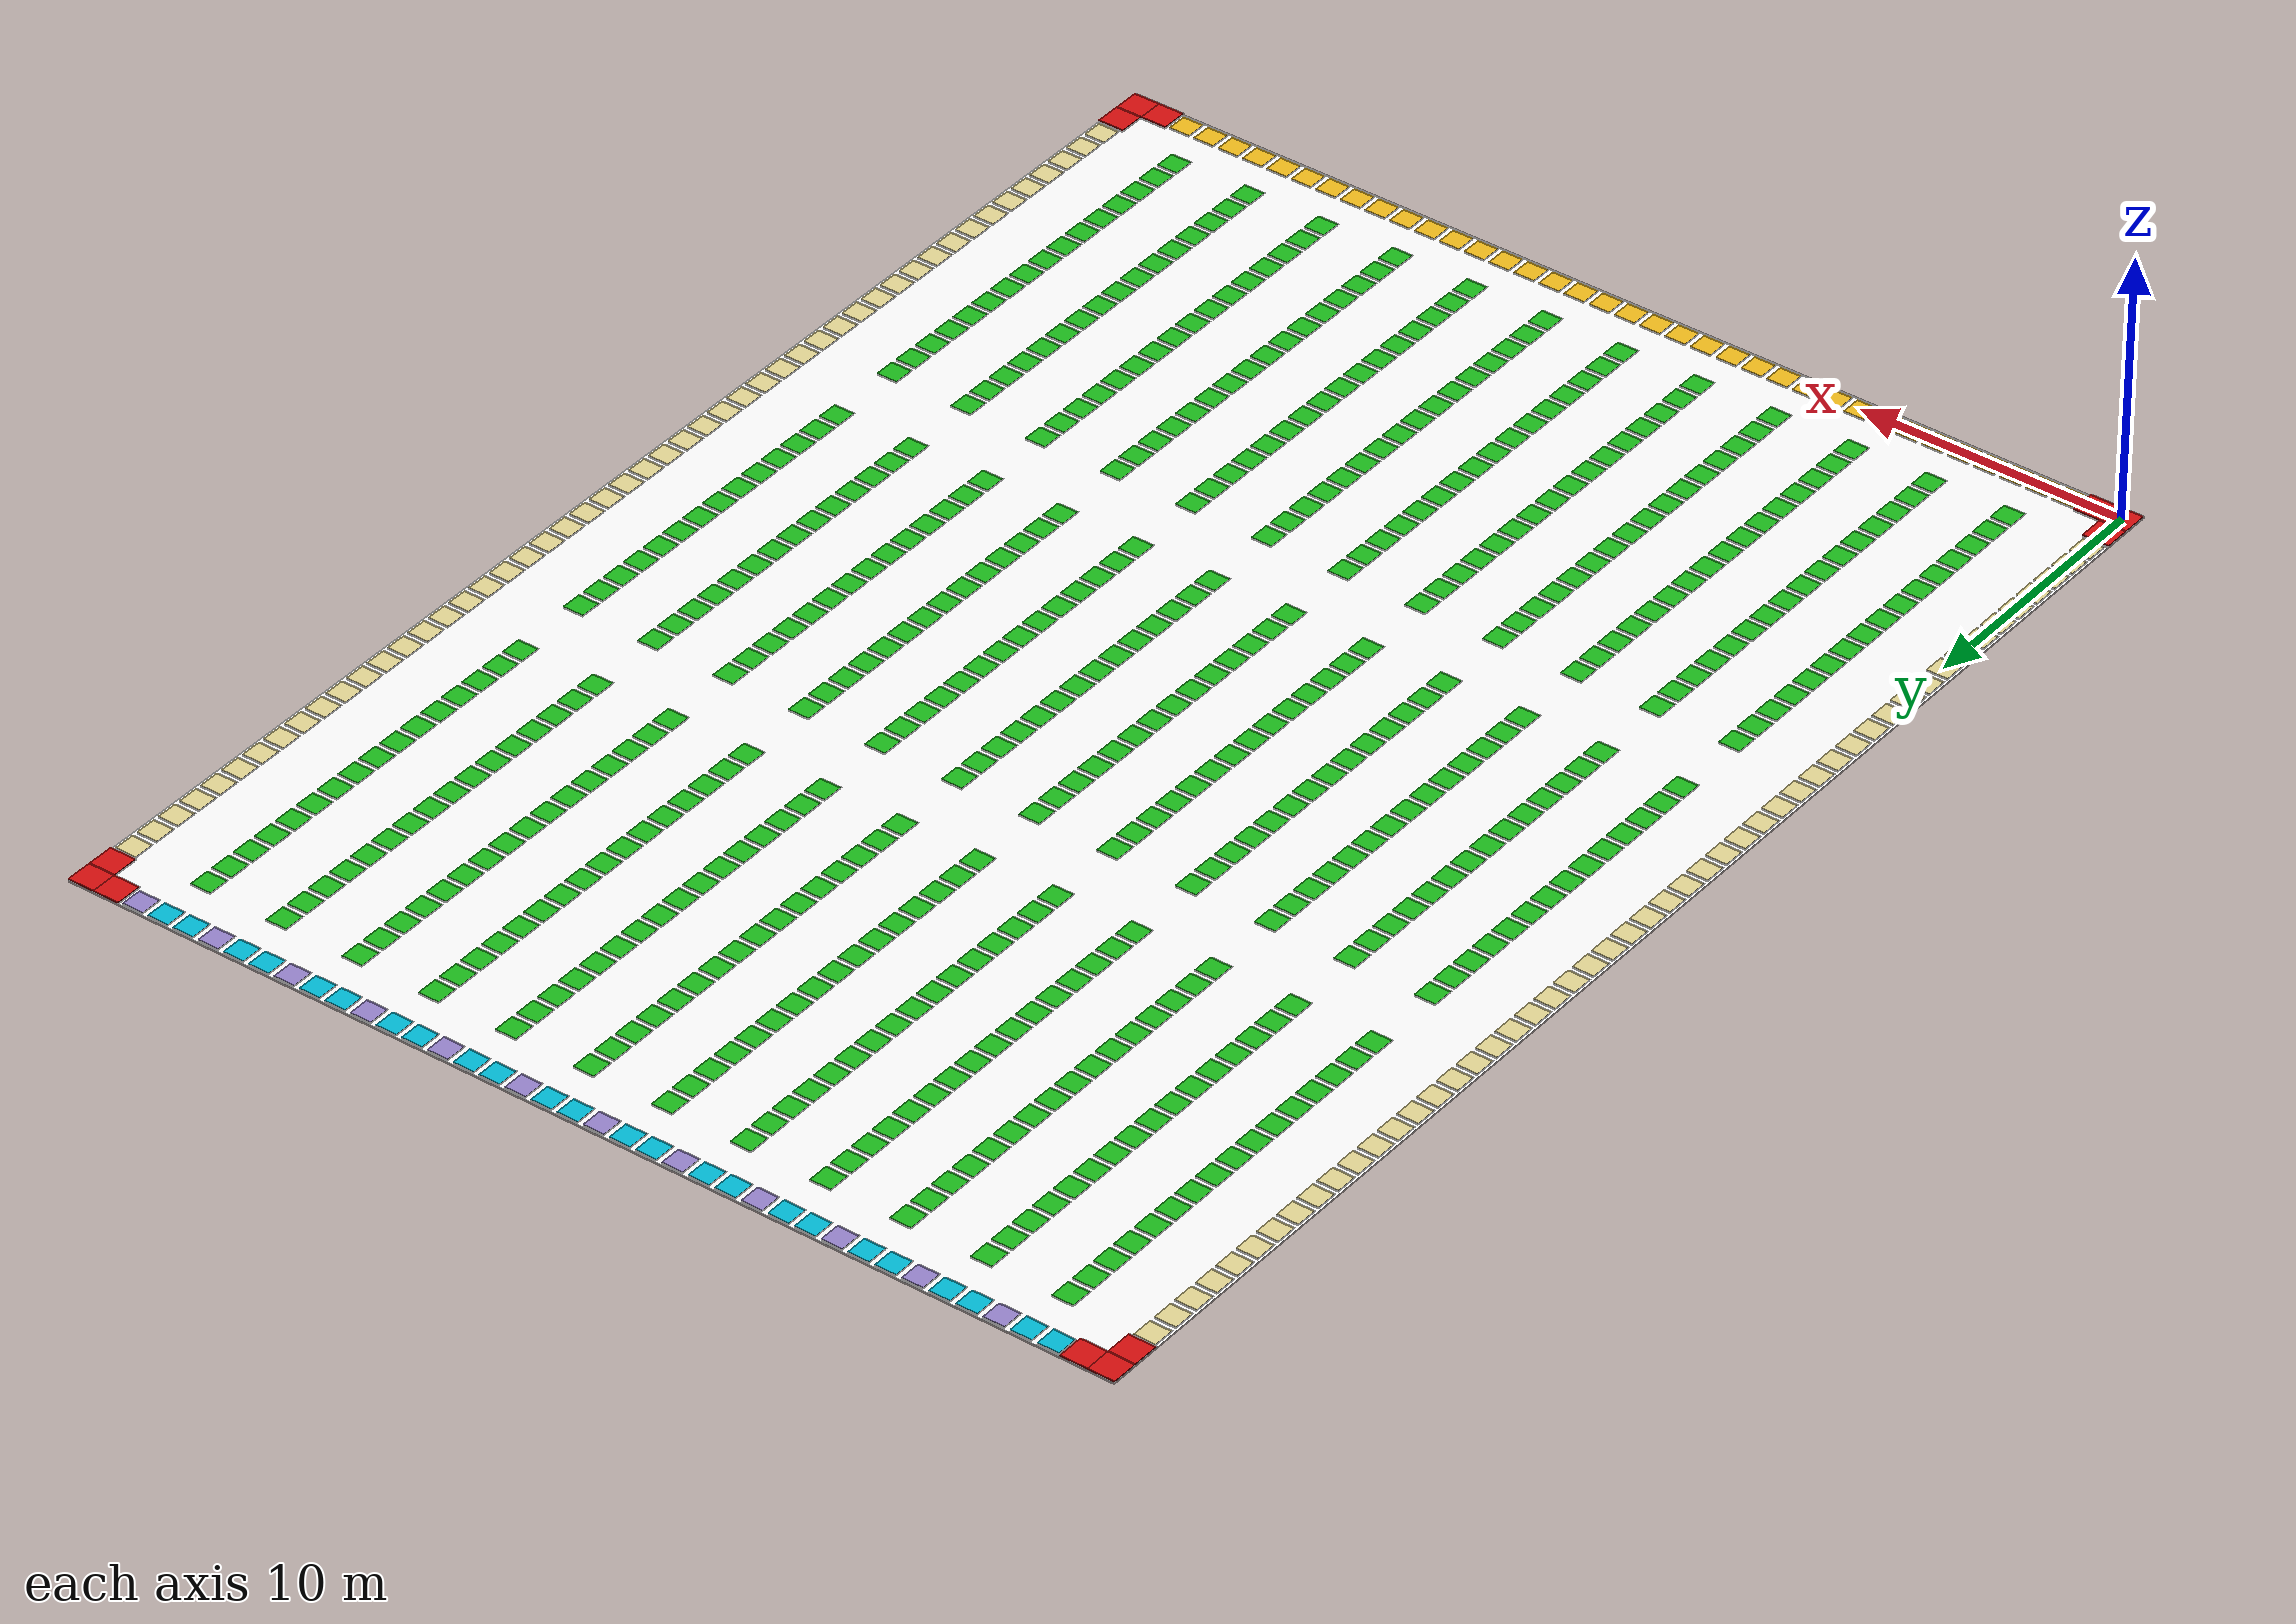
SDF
<?xml version="1.0"?>
<sdf version="1.10">
  <world name="warehouse">

    <plugin
      filename="gz-sim-physics-system"
      name="gz::sim::systems::Physics">
    </plugin>

    <plugin
      filename="gz-sim-user-commands-system"
      name="gz::sim::systems::UserCommands">
    </plugin>

    <plugin
      filename="gz-sim-scene-broadcaster-system"
      name="gz::sim::systems::SceneBroadcaster">
    </plugin>

    <scene>
      <ambient>0.8 0.8 0.8 1</ambient>
      <background>0.6 0.6 0.6 1</background>
      <shadows>false</shadows>
    </scene>

    <light type="directional" name="sun">
      <pose>0 0 20 0 0 0</pose>
      <direction>0 0 -1</direction>
      <diffuse>1 1 1 1</diffuse>
      <specular>0.2 0.2 0.2 1</specular>
      <cast_shadows>false</cast_shadows>
    </light>

    <model name="warehouse_floor">
      <static>true</static>

      <pose>
        19.5
        26.5
        0.0
        0 0 0
      </pose>

      <link name="floor_link">

        <visual name="floor_visual">
          <geometry>
            <box>
              <size>
                40.0
                54.0
                0.02
              </size>
            </box>
          </geometry>

          <material>
            <ambient>0.95 0.95 0.95 1</ambient>
            <diffuse>0.95 0.95 0.95 1</diffuse>
          </material>
        </visual>

      </link>
    </model>

    <model name="blocked_0000">
      <static>true</static>

      <pose>
        0.0
        0.0
        0.045
        0 0 0
      </pose>

      <link name="link">

        <visual name="visual">
          <geometry>
            <box>
              <size>
                1.0
                1.0
                0.05
              </size>
            </box>
          </geometry>

          <material>
            <ambient>0.8 0.05 0.05 1</ambient>
            <diffuse>0.8 0.05 0.05 1</diffuse>
          </material>
        </visual>

      </link>
    </model>

    <model name="blocked_0001">
      <static>true</static>

      <pose>
        0.0
        1.0
        0.045
        0 0 0
      </pose>

      <link name="link">

        <visual name="visual">
          <geometry>
            <box>
              <size>
                1.0
                1.0
                0.05
              </size>
            </box>
          </geometry>

          <material>
            <ambient>0.8 0.05 0.05 1</ambient>
            <diffuse>0.8 0.05 0.05 1</diffuse>
          </material>
        </visual>

      </link>
    </model>

    <model name="blocked_0002">
      <static>true</static>

      <pose>
        0.0
        52.0
        0.045
        0 0 0
      </pose>

      <link name="link">

        <visual name="visual">
          <geometry>
            <box>
              <size>
                1.0
                1.0
                0.05
              </size>
            </box>
          </geometry>

          <material>
            <ambient>0.8 0.05 0.05 1</ambient>
            <diffuse>0.8 0.05 0.05 1</diffuse>
          </material>
        </visual>

      </link>
    </model>

    <model name="blocked_0003">
      <static>true</static>

      <pose>
        0.0
        53.0
        0.045
        0 0 0
      </pose>

      <link name="link">

        <visual name="visual">
          <geometry>
            <box>
              <size>
                1.0
                1.0
                0.05
              </size>
            </box>
          </geometry>

          <material>
            <ambient>0.8 0.05 0.05 1</ambient>
            <diffuse>0.8 0.05 0.05 1</diffuse>
          </material>
        </visual>

      </link>
    </model>

    <model name="blocked_0004">
      <static>true</static>

      <pose>
        1.0
        0.0
        0.045
        0 0 0
      </pose>

      <link name="link">

        <visual name="visual">
          <geometry>
            <box>
              <size>
                1.0
                1.0
                0.05
              </size>
            </box>
          </geometry>

          <material>
            <ambient>0.8 0.05 0.05 1</ambient>
            <diffuse>0.8 0.05 0.05 1</diffuse>
          </material>
        </visual>

      </link>
    </model>

    <model name="blocked_0005">
      <static>true</static>

      <pose>
        1.0
        53.0
        0.045
        0 0 0
      </pose>

      <link name="link">

        <visual name="visual">
          <geometry>
            <box>
              <size>
                1.0
                1.0
                0.05
              </size>
            </box>
          </geometry>

          <material>
            <ambient>0.8 0.05 0.05 1</ambient>
            <diffuse>0.8 0.05 0.05 1</diffuse>
          </material>
        </visual>

      </link>
    </model>

    <model name="blocked_0006">
      <static>true</static>

      <pose>
        38.0
        0.0
        0.045
        0 0 0
      </pose>

      <link name="link">

        <visual name="visual">
          <geometry>
            <box>
              <size>
                1.0
                1.0
                0.05
              </size>
            </box>
          </geometry>

          <material>
            <ambient>0.8 0.05 0.05 1</ambient>
            <diffuse>0.8 0.05 0.05 1</diffuse>
          </material>
        </visual>

      </link>
    </model>

    <model name="blocked_0007">
      <static>true</static>

      <pose>
        38.0
        53.0
        0.045
        0 0 0
      </pose>

      <link name="link">

        <visual name="visual">
          <geometry>
            <box>
              <size>
                1.0
                1.0
                0.05
              </size>
            </box>
          </geometry>

          <material>
            <ambient>0.8 0.05 0.05 1</ambient>
            <diffuse>0.8 0.05 0.05 1</diffuse>
          </material>
        </visual>

      </link>
    </model>

    <model name="blocked_0008">
      <static>true</static>

      <pose>
        39.0
        0.0
        0.045
        0 0 0
      </pose>

      <link name="link">

        <visual name="visual">
          <geometry>
            <box>
              <size>
                1.0
                1.0
                0.05
              </size>
            </box>
          </geometry>

          <material>
            <ambient>0.8 0.05 0.05 1</ambient>
            <diffuse>0.8 0.05 0.05 1</diffuse>
          </material>
        </visual>

      </link>
    </model>

    <model name="blocked_0009">
      <static>true</static>

      <pose>
        39.0
        1.0
        0.045
        0 0 0
      </pose>

      <link name="link">

        <visual name="visual">
          <geometry>
            <box>
              <size>
                1.0
                1.0
                0.05
              </size>
            </box>
          </geometry>

          <material>
            <ambient>0.8 0.05 0.05 1</ambient>
            <diffuse>0.8 0.05 0.05 1</diffuse>
          </material>
        </visual>

      </link>
    </model>

    <model name="blocked_0010">
      <static>true</static>

      <pose>
        39.0
        52.0
        0.045
        0 0 0
      </pose>

      <link name="link">

        <visual name="visual">
          <geometry>
            <box>
              <size>
                1.0
                1.0
                0.05
              </size>
            </box>
          </geometry>

          <material>
            <ambient>0.8 0.05 0.05 1</ambient>
            <diffuse>0.8 0.05 0.05 1</diffuse>
          </material>
        </visual>

      </link>
    </model>

    <model name="blocked_0011">
      <static>true</static>

      <pose>
        39.0
        53.0
        0.045
        0 0 0
      </pose>

      <link name="link">

        <visual name="visual">
          <geometry>
            <box>
              <size>
                1.0
                1.0
                0.05
              </size>
            </box>
          </geometry>

          <material>
            <ambient>0.8 0.05 0.05 1</ambient>
            <diffuse>0.8 0.05 0.05 1</diffuse>
          </material>
        </visual>

      </link>
    </model>

    <model name="charging_001">
      <static>true</static>

      <pose>
        2.0
        53.0
        0.02
        0 0 0
      </pose>

      <link name="link">

        <visual name="visual">
          <geometry>
            <box>
              <size>
                0.8
                0.8
                0.02
              </size>
            </box>
          </geometry>

          <material>
            <ambient>0.00 0.70 0.80 1</ambient>
            <diffuse>0.00 0.70 0.80 1</diffuse>
          </material>
        </visual>

      </link>
    </model>

    <model name="charging_002">
      <static>true</static>

      <pose>
        3.0
        53.0
        0.02
        0 0 0
      </pose>

      <link name="link">

        <visual name="visual">
          <geometry>
            <box>
              <size>
                0.8
                0.8
                0.02
              </size>
            </box>
          </geometry>

          <material>
            <ambient>0.00 0.70 0.80 1</ambient>
            <diffuse>0.00 0.70 0.80 1</diffuse>
          </material>
        </visual>

      </link>
    </model>

    <model name="charge_queue_001">
      <static>true</static>

      <pose>
        4.0
        53.0
        0.02
        0 0 0
      </pose>

      <link name="link">

        <visual name="visual">
          <geometry>
            <box>
              <size>
                0.8
                0.8
                0.02
              </size>
            </box>
          </geometry>

          <material>
            <ambient>0.56 0.49 0.76 1</ambient>
            <diffuse>0.56 0.49 0.76 1</diffuse>
          </material>
        </visual>

      </link>
    </model>

    <model name="charging_003">
      <static>true</static>

      <pose>
        5.0
        53.0
        0.02
        0 0 0
      </pose>

      <link name="link">

        <visual name="visual">
          <geometry>
            <box>
              <size>
                0.8
                0.8
                0.02
              </size>
            </box>
          </geometry>

          <material>
            <ambient>0.00 0.70 0.80 1</ambient>
            <diffuse>0.00 0.70 0.80 1</diffuse>
          </material>
        </visual>

      </link>
    </model>

    <model name="charging_004">
      <static>true</static>

      <pose>
        6.0
        53.0
        0.02
        0 0 0
      </pose>

      <link name="link">

        <visual name="visual">
          <geometry>
            <box>
              <size>
                0.8
                0.8
                0.02
              </size>
            </box>
          </geometry>

          <material>
            <ambient>0.00 0.70 0.80 1</ambient>
            <diffuse>0.00 0.70 0.80 1</diffuse>
          </material>
        </visual>

      </link>
    </model>

    <model name="charge_queue_002">
      <static>true</static>

      <pose>
        7.0
        53.0
        0.02
        0 0 0
      </pose>

      <link name="link">

        <visual name="visual">
          <geometry>
            <box>
              <size>
                0.8
                0.8
                0.02
              </size>
            </box>
          </geometry>

          <material>
            <ambient>0.56 0.49 0.76 1</ambient>
            <diffuse>0.56 0.49 0.76 1</diffuse>
          </material>
        </visual>

      </link>
    </model>

    <model name="charging_005">
      <static>true</static>

      <pose>
        8.0
        53.0
        0.02
        0 0 0
      </pose>

      <link name="link">

        <visual name="visual">
          <geometry>
            <box>
              <size>
                0.8
                0.8
                0.02
              </size>
            </box>
          </geometry>

          <material>
            <ambient>0.00 0.70 0.80 1</ambient>
            <diffuse>0.00 0.70 0.80 1</diffuse>
          </material>
        </visual>

      </link>
    </model>

    <model name="charging_006">
      <static>true</static>

      <pose>
        9.0
        53.0
        0.02
        0 0 0
      </pose>

      <link name="link">

        <visual name="visual">
          <geometry>
            <box>
              <size>
                0.8
                0.8
                0.02
              </size>
            </box>
          </geometry>

          <material>
            <ambient>0.00 0.70 0.80 1</ambient>
            <diffuse>0.00 0.70 0.80 1</diffuse>
          </material>
        </visual>

      </link>
    </model>

    <model name="charge_queue_003">
      <static>true</static>

      <pose>
        10.0
        53.0
        0.02
        0 0 0
      </pose>

      <link name="link">

        <visual name="visual">
          <geometry>
            <box>
              <size>
                0.8
                0.8
                0.02
              </size>
            </box>
          </geometry>

          <material>
            <ambient>0.56 0.49 0.76 1</ambient>
            <diffuse>0.56 0.49 0.76 1</diffuse>
          </material>
        </visual>

      </link>
    </model>

    <model name="charging_007">
      <static>true</static>

      <pose>
        11.0
        53.0
        0.02
        0 0 0
      </pose>

      <link name="link">

        <visual name="visual">
          <geometry>
            <box>
              <size>
                0.8
                0.8
                0.02
              </size>
            </box>
          </geometry>

          <material>
            <ambient>0.00 0.70 0.80 1</ambient>
            <diffuse>0.00 0.70 0.80 1</diffuse>
          </material>
        </visual>

      </link>
    </model>

    <model name="charging_008">
      <static>true</static>

      <pose>
        12.0
        53.0
        0.02
        0 0 0
      </pose>

      <link name="link">

        <visual name="visual">
          <geometry>
            <box>
              <size>
                0.8
                0.8
                0.02
              </size>
            </box>
          </geometry>

          <material>
            <ambient>0.00 0.70 0.80 1</ambient>
            <diffuse>0.00 0.70 0.80 1</diffuse>
          </material>
        </visual>

      </link>
    </model>

    <model name="charge_queue_004">
      <static>true</static>

      <pose>
        13.0
        53.0
        0.02
        0 0 0
      </pose>

      <link name="link">

        <visual name="visual">
          <geometry>
            <box>
              <size>
                0.8
                0.8
                0.02
              </size>
            </box>
          </geometry>

          <material>
            <ambient>0.56 0.49 0.76 1</ambient>
            <diffuse>0.56 0.49 0.76 1</diffuse>
          </material>
        </visual>

      </link>
    </model>

    <model name="charging_009">
      <static>true</static>

      <pose>
        14.0
        53.0
        0.02
        0 0 0
      </pose>

      <link name="link">

        <visual name="visual">
          <geometry>
            <box>
              <size>
                0.8
                0.8
                0.02
              </size>
            </box>
          </geometry>

          <material>
            <ambient>0.00 0.70 0.80 1</ambient>
            <diffuse>0.00 0.70 0.80 1</diffuse>
          </material>
        </visual>

      </link>
    </model>

    <model name="charging_010">
      <static>true</static>

      <pose>
        15.0
        53.0
        0.02
        0 0 0
      </pose>

      <link name="link">

        <visual name="visual">
          <geometry>
            <box>
              <size>
                0.8
                0.8
                0.02
              </size>
            </box>
          </geometry>

          <material>
            <ambient>0.00 0.70 0.80 1</ambient>
            <diffuse>0.00 0.70 0.80 1</diffuse>
          </material>
        </visual>

      </link>
    </model>

    <model name="charge_queue_005">
      <static>true</static>

      <pose>
        16.0
        53.0
        0.02
        0 0 0
      </pose>

      <link name="link">

        <visual name="visual">
          <geometry>
            <box>
              <size>
                0.8
                0.8
                0.02
              </size>
            </box>
          </geometry>

          <material>
            <ambient>0.56 0.49 0.76 1</ambient>
            <diffuse>0.56 0.49 0.76 1</diffuse>
          </material>
        </visual>

      </link>
    </model>

    <model name="charging_011">
      <static>true</static>

      <pose>
        17.0
        53.0
        0.02
        0 0 0
      </pose>

      <link name="link">

        <visual name="visual">
          <geometry>
            <box>
              <size>
                0.8
                0.8
                0.02
              </size>
            </box>
          </geometry>

          <material>
            <ambient>0.00 0.70 0.80 1</ambient>
            <diffuse>0.00 0.70 0.80 1</diffuse>
          </material>
        </visual>

      </link>
    </model>

    <model name="charging_012">
      <static>true</static>

      <pose>
        18.0
        53.0
        0.02
        0 0 0
      </pose>

      <link name="link">

        <visual name="visual">
          <geometry>
            <box>
              <size>
                0.8
                0.8
                0.02
              </size>
            </box>
          </geometry>

          <material>
            <ambient>0.00 0.70 0.80 1</ambient>
            <diffuse>0.00 0.70 0.80 1</diffuse>
          </material>
        </visual>

      </link>
    </model>

    <model name="charge_queue_006">
      <static>true</static>

      <pose>
        19.0
        53.0
        0.02
        0 0 0
      </pose>

      <link name="link">

        <visual name="visual">
          <geometry>
            <box>
              <size>
                0.8
                0.8
                0.02
              </size>
            </box>
          </geometry>

          <material>
            <ambient>0.56 0.49 0.76 1</ambient>
            <diffuse>0.56 0.49 0.76 1</diffuse>
          </material>
        </visual>

      </link>
    </model>

    <model name="charging_013">
      <static>true</static>

      <pose>
        20.0
        53.0
        0.02
        0 0 0
      </pose>

      <link name="link">

        <visual name="visual">
          <geometry>
            <box>
              <size>
                0.8
                0.8
                0.02
              </size>
            </box>
          </geometry>

          <material>
            <ambient>0.00 0.70 0.80 1</ambient>
            <diffuse>0.00 0.70 0.80 1</diffuse>
          </material>
        </visual>

      </link>
    </model>

    <model name="charging_014">
      <static>true</static>

      <pose>
        21.0
        53.0
        0.02
        0 0 0
      </pose>

      <link name="link">

        <visual name="visual">
          <geometry>
            <box>
              <size>
                0.8
                0.8
                0.02
              </size>
            </box>
          </geometry>

          <material>
            <ambient>0.00 0.70 0.80 1</ambient>
            <diffuse>0.00 0.70 0.80 1</diffuse>
          </material>
        </visual>

      </link>
    </model>

    <model name="charge_queue_007">
      <static>true</static>

      <pose>
        22.0
        53.0
        0.02
        0 0 0
      </pose>

      <link name="link">

        <visual name="visual">
          <geometry>
            <box>
              <size>
                0.8
                0.8
                0.02
              </size>
            </box>
          </geometry>

          <material>
            <ambient>0.56 0.49 0.76 1</ambient>
            <diffuse>0.56 0.49 0.76 1</diffuse>
          </material>
        </visual>

      </link>
    </model>

    <model name="charging_015">
      <static>true</static>

      <pose>
        23.0
        53.0
        0.02
        0 0 0
      </pose>

      <link name="link">

        <visual name="visual">
          <geometry>
            <box>
              <size>
                0.8
                0.8
                0.02
              </size>
            </box>
          </geometry>

          <material>
            <ambient>0.00 0.70 0.80 1</ambient>
            <diffuse>0.00 0.70 0.80 1</diffuse>
          </material>
        </visual>

      </link>
    </model>

    <model name="charging_016">
      <static>true</static>

      <pose>
        24.0
        53.0
        0.02
        0 0 0
      </pose>

      <link name="link">

        <visual name="visual">
          <geometry>
            <box>
              <size>
                0.8
                0.8
                0.02
              </size>
            </box>
          </geometry>

          <material>
            <ambient>0.00 0.70 0.80 1</ambient>
            <diffuse>0.00 0.70 0.80 1</diffuse>
          </material>
        </visual>

      </link>
    </model>

    <model name="charge_queue_008">
      <static>true</static>

      <pose>
        25.0
        53.0
        0.02
        0 0 0
      </pose>

      <link name="link">

        <visual name="visual">
          <geometry>
            <box>
              <size>
                0.8
                0.8
                0.02
              </size>
            </box>
          </geometry>

          <material>
            <ambient>0.56 0.49 0.76 1</ambient>
            <diffuse>0.56 0.49 0.76 1</diffuse>
          </material>
        </visual>

      </link>
    </model>

    <model name="charging_017">
      <static>true</static>

      <pose>
        26.0
        53.0
        0.02
        0 0 0
      </pose>

      <link name="link">

        <visual name="visual">
          <geometry>
            <box>
              <size>
                0.8
                0.8
                0.02
              </size>
            </box>
          </geometry>

          <material>
            <ambient>0.00 0.70 0.80 1</ambient>
            <diffuse>0.00 0.70 0.80 1</diffuse>
          </material>
        </visual>

      </link>
    </model>

    <model name="charging_018">
      <static>true</static>

      <pose>
        27.0
        53.0
        0.02
        0 0 0
      </pose>

      <link name="link">

        <visual name="visual">
          <geometry>
            <box>
              <size>
                0.8
                0.8
                0.02
              </size>
            </box>
          </geometry>

          <material>
            <ambient>0.00 0.70 0.80 1</ambient>
            <diffuse>0.00 0.70 0.80 1</diffuse>
          </material>
        </visual>

      </link>
    </model>

    <model name="charge_queue_009">
      <static>true</static>

      <pose>
        28.0
        53.0
        0.02
        0 0 0
      </pose>

      <link name="link">

        <visual name="visual">
          <geometry>
            <box>
              <size>
                0.8
                0.8
                0.02
              </size>
            </box>
          </geometry>

          <material>
            <ambient>0.56 0.49 0.76 1</ambient>
            <diffuse>0.56 0.49 0.76 1</diffuse>
          </material>
        </visual>

      </link>
    </model>

    <model name="charging_019">
      <static>true</static>

      <pose>
        29.0
        53.0
        0.02
        0 0 0
      </pose>

      <link name="link">

        <visual name="visual">
          <geometry>
            <box>
              <size>
                0.8
                0.8
                0.02
              </size>
            </box>
          </geometry>

          <material>
            <ambient>0.00 0.70 0.80 1</ambient>
            <diffuse>0.00 0.70 0.80 1</diffuse>
          </material>
        </visual>

      </link>
    </model>

    <model name="charging_020">
      <static>true</static>

      <pose>
        30.0
        53.0
        0.02
        0 0 0
      </pose>

      <link name="link">

        <visual name="visual">
          <geometry>
            <box>
              <size>
                0.8
                0.8
                0.02
              </size>
            </box>
          </geometry>

          <material>
            <ambient>0.00 0.70 0.80 1</ambient>
            <diffuse>0.00 0.70 0.80 1</diffuse>
          </material>
        </visual>

      </link>
    </model>

    <model name="charge_queue_010">
      <static>true</static>

      <pose>
        31.0
        53.0
        0.02
        0 0 0
      </pose>

      <link name="link">

        <visual name="visual">
          <geometry>
            <box>
              <size>
                0.8
                0.8
                0.02
              </size>
            </box>
          </geometry>

          <material>
            <ambient>0.56 0.49 0.76 1</ambient>
            <diffuse>0.56 0.49 0.76 1</diffuse>
          </material>
        </visual>

      </link>
    </model>

    <model name="charging_021">
      <static>true</static>

      <pose>
        32.0
        53.0
        0.02
        0 0 0
      </pose>

      <link name="link">

        <visual name="visual">
          <geometry>
            <box>
              <size>
                0.8
                0.8
                0.02
              </size>
            </box>
          </geometry>

          <material>
            <ambient>0.00 0.70 0.80 1</ambient>
            <diffuse>0.00 0.70 0.80 1</diffuse>
          </material>
        </visual>

      </link>
    </model>

    <model name="charging_022">
      <static>true</static>

      <pose>
        33.0
        53.0
        0.02
        0 0 0
      </pose>

      <link name="link">

        <visual name="visual">
          <geometry>
            <box>
              <size>
                0.8
                0.8
                0.02
              </size>
            </box>
          </geometry>

          <material>
            <ambient>0.00 0.70 0.80 1</ambient>
            <diffuse>0.00 0.70 0.80 1</diffuse>
          </material>
        </visual>

      </link>
    </model>

    <model name="charge_queue_011">
      <static>true</static>

      <pose>
        34.0
        53.0
        0.02
        0 0 0
      </pose>

      <link name="link">

        <visual name="visual">
          <geometry>
            <box>
              <size>
                0.8
                0.8
                0.02
              </size>
            </box>
          </geometry>

          <material>
            <ambient>0.56 0.49 0.76 1</ambient>
            <diffuse>0.56 0.49 0.76 1</diffuse>
          </material>
        </visual>

      </link>
    </model>

    <model name="charging_023">
      <static>true</static>

      <pose>
        35.0
        53.0
        0.02
        0 0 0
      </pose>

      <link name="link">

        <visual name="visual">
          <geometry>
            <box>
              <size>
                0.8
                0.8
                0.02
              </size>
            </box>
          </geometry>

          <material>
            <ambient>0.00 0.70 0.80 1</ambient>
            <diffuse>0.00 0.70 0.80 1</diffuse>
          </material>
        </visual>

      </link>
    </model>

    <model name="charging_024">
      <static>true</static>

      <pose>
        36.0
        53.0
        0.02
        0 0 0
      </pose>

      <link name="link">

        <visual name="visual">
          <geometry>
            <box>
              <size>
                0.8
                0.8
                0.02
              </size>
            </box>
          </geometry>

          <material>
            <ambient>0.00 0.70 0.80 1</ambient>
            <diffuse>0.00 0.70 0.80 1</diffuse>
          </material>
        </visual>

      </link>
    </model>

    <model name="charge_queue_012">
      <static>true</static>

      <pose>
        37.0
        53.0
        0.02
        0 0 0
      </pose>

      <link name="link">

        <visual name="visual">
          <geometry>
            <box>
              <size>
                0.8
                0.8
                0.02
              </size>
            </box>
          </geometry>

          <material>
            <ambient>0.56 0.49 0.76 1</ambient>
            <diffuse>0.56 0.49 0.76 1</diffuse>
          </material>
        </visual>

      </link>
    </model>

    <model name="staging_001">
      <static>true</static>

      <pose>
        0.0
        51.0
        0.02
        0 0 0
      </pose>

      <link name="link">

        <visual name="visual">
          <geometry>
            <box>
              <size>
                0.8
                0.8
                0.02
              </size>
            </box>
          </geometry>

          <material>
            <ambient>0.85 0.80 0.55 1</ambient>
            <diffuse>0.85 0.80 0.55 1</diffuse>
          </material>
        </visual>

      </link>
    </model>

    <model name="shelf_001">
      <static>true</static>

      <pose>
        3.0
        51.0
        0.02
        0 0 0
      </pose>

      <link name="link">

        <visual name="visual">
          <geometry>
            <box>
              <size>
                0.8
                0.8
                0.02
              </size>
            </box>
          </geometry>

          <material>
            <ambient>0.10 0.70 0.10 1</ambient>
            <diffuse>0.10 0.70 0.10 1</diffuse>
          </material>
        </visual>

      </link>
    </model>

    <model name="shelf_002">
      <static>true</static>

      <pose>
        6.0
        51.0
        0.02
        0 0 0
      </pose>

      <link name="link">

        <visual name="visual">
          <geometry>
            <box>
              <size>
                0.8
                0.8
                0.02
              </size>
            </box>
          </geometry>

          <material>
            <ambient>0.10 0.70 0.10 1</ambient>
            <diffuse>0.10 0.70 0.10 1</diffuse>
          </material>
        </visual>

      </link>
    </model>

    <model name="shelf_003">
      <static>true</static>

      <pose>
        9.0
        51.0
        0.02
        0 0 0
      </pose>

      <link name="link">

        <visual name="visual">
          <geometry>
            <box>
              <size>
                0.8
                0.8
                0.02
              </size>
            </box>
          </geometry>

          <material>
            <ambient>0.10 0.70 0.10 1</ambient>
            <diffuse>0.10 0.70 0.10 1</diffuse>
          </material>
        </visual>

      </link>
    </model>

    <model name="shelf_004">
      <static>true</static>

      <pose>
        12.0
        51.0
        0.02
        0 0 0
      </pose>

      <link name="link">

        <visual name="visual">
          <geometry>
            <box>
              <size>
                0.8
                0.8
                0.02
              </size>
            </box>
          </geometry>

          <material>
            <ambient>0.10 0.70 0.10 1</ambient>
            <diffuse>0.10 0.70 0.10 1</diffuse>
          </material>
        </visual>

      </link>
    </model>

    <model name="shelf_005">
      <static>true</static>

      <pose>
        15.0
        51.0
        0.02
        0 0 0
      </pose>

      <link name="link">

        <visual name="visual">
          <geometry>
            <box>
              <size>
                0.8
                0.8
                0.02
              </size>
            </box>
          </geometry>

          <material>
            <ambient>0.10 0.70 0.10 1</ambient>
            <diffuse>0.10 0.70 0.10 1</diffuse>
          </material>
        </visual>

      </link>
    </model>

    <model name="shelf_006">
      <static>true</static>

      <pose>
        18.0
        51.0
        0.02
        0 0 0
      </pose>

      <link name="link">

        <visual name="visual">
          <geometry>
            <box>
              <size>
                0.8
                0.8
                0.02
              </size>
            </box>
          </geometry>

          <material>
            <ambient>0.10 0.70 0.10 1</ambient>
            <diffuse>0.10 0.70 0.10 1</diffuse>
          </material>
        </visual>

      </link>
    </model>

    <model name="shelf_007">
      <static>true</static>

      <pose>
        21.0
        51.0
        0.02
        0 0 0
      </pose>

      <link name="link">

        <visual name="visual">
          <geometry>
            <box>
              <size>
                0.8
                0.8
                0.02
              </size>
            </box>
          </geometry>

          <material>
            <ambient>0.10 0.70 0.10 1</ambient>
            <diffuse>0.10 0.70 0.10 1</diffuse>
          </material>
        </visual>

      </link>
    </model>

    <model name="shelf_008">
      <static>true</static>

      <pose>
        24.0
        51.0
        0.02
        0 0 0
      </pose>

      <link name="link">

        <visual name="visual">
          <geometry>
            <box>
              <size>
                0.8
                0.8
                0.02
              </size>
            </box>
          </geometry>

          <material>
            <ambient>0.10 0.70 0.10 1</ambient>
            <diffuse>0.10 0.70 0.10 1</diffuse>
          </material>
        </visual>

      </link>
    </model>

    <model name="shelf_009">
      <static>true</static>

      <pose>
        27.0
        51.0
        0.02
        0 0 0
      </pose>

      <link name="link">

        <visual name="visual">
          <geometry>
            <box>
              <size>
                0.8
                0.8
                0.02
              </size>
            </box>
          </geometry>

          <material>
            <ambient>0.10 0.70 0.10 1</ambient>
            <diffuse>0.10 0.70 0.10 1</diffuse>
          </material>
        </visual>

      </link>
    </model>

    <model name="shelf_010">
      <static>true</static>

      <pose>
        30.0
        51.0
        0.02
        0 0 0
      </pose>

      <link name="link">

        <visual name="visual">
          <geometry>
            <box>
              <size>
                0.8
                0.8
                0.02
              </size>
            </box>
          </geometry>

          <material>
            <ambient>0.10 0.70 0.10 1</ambient>
            <diffuse>0.10 0.70 0.10 1</diffuse>
          </material>
        </visual>

      </link>
    </model>

    <model name="shelf_011">
      <static>true</static>

      <pose>
        33.0
        51.0
        0.02
        0 0 0
      </pose>

      <link name="link">

        <visual name="visual">
          <geometry>
            <box>
              <size>
                0.8
                0.8
                0.02
              </size>
            </box>
          </geometry>

          <material>
            <ambient>0.10 0.70 0.10 1</ambient>
            <diffuse>0.10 0.70 0.10 1</diffuse>
          </material>
        </visual>

      </link>
    </model>

    <model name="shelf_012">
      <static>true</static>

      <pose>
        36.0
        51.0
        0.02
        0 0 0
      </pose>

      <link name="link">

        <visual name="visual">
          <geometry>
            <box>
              <size>
                0.8
                0.8
                0.02
              </size>
            </box>
          </geometry>

          <material>
            <ambient>0.10 0.70 0.10 1</ambient>
            <diffuse>0.10 0.70 0.10 1</diffuse>
          </material>
        </visual>

      </link>
    </model>

    <model name="staging_002">
      <static>true</static>

      <pose>
        39.0
        51.0
        0.02
        0 0 0
      </pose>

      <link name="link">

        <visual name="visual">
          <geometry>
            <box>
              <size>
                0.8
                0.8
                0.02
              </size>
            </box>
          </geometry>

          <material>
            <ambient>0.85 0.80 0.55 1</ambient>
            <diffuse>0.85 0.80 0.55 1</diffuse>
          </material>
        </visual>

      </link>
    </model>

    <model name="staging_003">
      <static>true</static>

      <pose>
        0.0
        50.0
        0.02
        0 0 0
      </pose>

      <link name="link">

        <visual name="visual">
          <geometry>
            <box>
              <size>
                0.8
                0.8
                0.02
              </size>
            </box>
          </geometry>

          <material>
            <ambient>0.85 0.80 0.55 1</ambient>
            <diffuse>0.85 0.80 0.55 1</diffuse>
          </material>
        </visual>

      </link>
    </model>

    <model name="shelf_013">
      <static>true</static>

      <pose>
        3.0
        50.0
        0.02
        0 0 0
      </pose>

      <link name="link">

        <visual name="visual">
          <geometry>
            <box>
              <size>
                0.8
                0.8
                0.02
              </size>
            </box>
          </geometry>

          <material>
            <ambient>0.10 0.70 0.10 1</ambient>
            <diffuse>0.10 0.70 0.10 1</diffuse>
          </material>
        </visual>

      </link>
    </model>

    <model name="shelf_014">
      <static>true</static>

      <pose>
        6.0
        50.0
        0.02
        0 0 0
      </pose>

      <link name="link">

        <visual name="visual">
          <geometry>
            <box>
              <size>
                0.8
                0.8
                0.02
              </size>
            </box>
          </geometry>

          <material>
            <ambient>0.10 0.70 0.10 1</ambient>
            <diffuse>0.10 0.70 0.10 1</diffuse>
          </material>
        </visual>

      </link>
    </model>

    <model name="shelf_015">
      <static>true</static>

      <pose>
        9.0
        50.0
        0.02
        0 0 0
      </pose>

      <link name="link">

        <visual name="visual">
          <geometry>
            <box>
              <size>
                0.8
                0.8
                0.02
              </size>
            </box>
          </geometry>

          <material>
            <ambient>0.10 0.70 0.10 1</ambient>
            <diffuse>0.10 0.70 0.10 1</diffuse>
          </material>
        </visual>

      </link>
    </model>

    <model name="shelf_016">
      <static>true</static>

      <pose>
        12.0
        50.0
        0.02
        0 0 0
      </pose>

      <link name="link">

        <visual name="visual">
          <geometry>
            <box>
              <size>
                0.8
                0.8
                0.02
              </size>
            </box>
          </geometry>

          <material>
            <ambient>0.10 0.70 0.10 1</ambient>
            <diffuse>0.10 0.70 0.10 1</diffuse>
          </material>
        </visual>

      </link>
    </model>

    <model name="shelf_017">
      <static>true</static>

      <pose>
        15.0
        50.0
        0.02
        0 0 0
      </pose>

      <link name="link">

        <visual name="visual">
          <geometry>
            <box>
              <size>
                0.8
                0.8
                0.02
              </size>
            </box>
          </geometry>

          <material>
            <ambient>0.10 0.70 0.10 1</ambient>
            <diffuse>0.10 0.70 0.10 1</diffuse>
          </material>
        </visual>

      </link>
    </model>

    <model name="shelf_018">
      <static>true</static>

      <pose>
        18.0
        50.0
        0.02
        0 0 0
      </pose>

      <link name="link">

        <visual name="visual">
          <geometry>
            <box>
              <size>
                0.8
                0.8
                0.02
              </size>
            </box>
          </geometry>

          <material>
            <ambient>0.10 0.70 0.10 1</ambient>
            <diffuse>0.10 0.70 0.10 1</diffuse>
          </material>
        </visual>

      </link>
    </model>

    <model name="shelf_019">
      <static>true</static>

      <pose>
        21.0
        50.0
        0.02
        0 0 0
      </pose>

      <link name="link">

        <visual name="visual">
          <geometry>
            <box>
              <size>
                0.8
                0.8
                0.02
              </size>
            </box>
          </geometry>

          <material>
            <ambient>0.10 0.70 0.10 1</ambient>
            <diffuse>0.10 0.70 0.10 1</diffuse>
          </material>
        </visual>

      </link>
    </model>

    <model name="shelf_020">
      <static>true</static>

      <pose>
        24.0
        50.0
        0.02
        0 0 0
      </pose>

      <link name="link">

        <visual name="visual">
          <geometry>
            <box>
              <size>
                0.8
                0.8
                0.02
              </size>
            </box>
          </geometry>

          <material>
            <ambient>0.10 0.70 0.10 1</ambient>
            <diffuse>0.10 0.70 0.10 1</diffuse>
          </material>
        </visual>

      </link>
    </model>

    <model name="shelf_021">
      <static>true</static>

      <pose>
        27.0
        50.0
        0.02
        0 0 0
      </pose>

      <link name="link">

        <visual name="visual">
          <geometry>
            <box>
              <size>
                0.8
                0.8
                0.02
              </size>
            </box>
          </geometry>

          <material>
            <ambient>0.10 0.70 0.10 1</ambient>
            <diffuse>0.10 0.70 0.10 1</diffuse>
          </material>
        </visual>

      </link>
    </model>

    <model name="shelf_022">
      <static>true</static>

      <pose>
        30.0
        50.0
        0.02
        0 0 0
      </pose>

      <link name="link">

        <visual name="visual">
          <geometry>
            <box>
              <size>
                0.8
                0.8
                0.02
              </size>
            </box>
          </geometry>

          <material>
            <ambient>0.10 0.70 0.10 1</ambient>
            <diffuse>0.10 0.70 0.10 1</diffuse>
          </material>
        </visual>

      </link>
    </model>

    <model name="shelf_023">
      <static>true</static>

      <pose>
        33.0
        50.0
        0.02
        0 0 0
      </pose>

      <link name="link">

        <visual name="visual">
          <geometry>
            <box>
              <size>
                0.8
                0.8
                0.02
              </size>
            </box>
          </geometry>

          <material>
            <ambient>0.10 0.70 0.10 1</ambient>
            <diffuse>0.10 0.70 0.10 1</diffuse>
          </material>
        </visual>

      </link>
    </model>

    <model name="shelf_024">
      <static>true</static>

      <pose>
        36.0
        50.0
        0.02
        0 0 0
      </pose>

      <link name="link">

        <visual name="visual">
          <geometry>
            <box>
              <size>
                0.8
                0.8
                0.02
              </size>
            </box>
          </geometry>

          <material>
            <ambient>0.10 0.70 0.10 1</ambient>
            <diffuse>0.10 0.70 0.10 1</diffuse>
          </material>
        </visual>

      </link>
    </model>

    <model name="staging_004">
      <static>true</static>

      <pose>
        39.0
        50.0
        0.02
        0 0 0
      </pose>

      <link name="link">

        <visual name="visual">
          <geometry>
            <box>
              <size>
                0.8
                0.8
                0.02
              </size>
            </box>
          </geometry>

          <material>
            <ambient>0.85 0.80 0.55 1</ambient>
            <diffuse>0.85 0.80 0.55 1</diffuse>
          </material>
        </visual>

      </link>
    </model>

    <model name="staging_005">
      <static>true</static>

      <pose>
        0.0
        49.0
        0.02
        0 0 0
      </pose>

      <link name="link">

        <visual name="visual">
          <geometry>
            <box>
              <size>
                0.8
                0.8
                0.02
              </size>
            </box>
          </geometry>

          <material>
            <ambient>0.85 0.80 0.55 1</ambient>
            <diffuse>0.85 0.80 0.55 1</diffuse>
          </material>
        </visual>

      </link>
    </model>

    <model name="shelf_025">
      <static>true</static>

      <pose>
        3.0
        49.0
        0.02
        0 0 0
      </pose>

      <link name="link">

        <visual name="visual">
          <geometry>
            <box>
              <size>
                0.8
                0.8
                0.02
              </size>
            </box>
          </geometry>

          <material>
            <ambient>0.10 0.70 0.10 1</ambient>
            <diffuse>0.10 0.70 0.10 1</diffuse>
          </material>
        </visual>

      </link>
    </model>

    <model name="shelf_026">
      <static>true</static>

      <pose>
        6.0
        49.0
        0.02
        0 0 0
      </pose>

      <link name="link">

        <visual name="visual">
          <geometry>
            <box>
              <size>
                0.8
                0.8
                0.02
              </size>
            </box>
          </geometry>

          <material>
            <ambient>0.10 0.70 0.10 1</ambient>
            <diffuse>0.10 0.70 0.10 1</diffuse>
          </material>
        </visual>

      </link>
    </model>

    <model name="shelf_027">
      <static>true</static>

      <pose>
        9.0
        49.0
        0.02
        0 0 0
      </pose>

      <link name="link">

        <visual name="visual">
          <geometry>
            <box>
              <size>
                0.8
                0.8
                0.02
              </size>
            </box>
          </geometry>

          <material>
            <ambient>0.10 0.70 0.10 1</ambient>
            <diffuse>0.10 0.70 0.10 1</diffuse>
          </material>
        </visual>

      </link>
    </model>

    <model name="shelf_028">
      <static>true</static>

      <pose>
        12.0
        49.0
        0.02
        0 0 0
      </pose>

      <link name="link">

        <visual name="visual">
          <geometry>
            <box>
              <size>
                0.8
                0.8
                0.02
              </size>
            </box>
          </geometry>

          <material>
            <ambient>0.10 0.70 0.10 1</ambient>
            <diffuse>0.10 0.70 0.10 1</diffuse>
          </material>
        </visual>

      </link>
    </model>

    <model name="shelf_029">
      <static>true</static>

      <pose>
        15.0
        49.0
        0.02
        0 0 0
      </pose>

      <link name="link">

        <visual name="visual">
          <geometry>
            <box>
              <size>
                0.8
                0.8
                0.02
              </size>
            </box>
          </geometry>

          <material>
            <ambient>0.10 0.70 0.10 1</ambient>
            <diffuse>0.10 0.70 0.10 1</diffuse>
          </material>
        </visual>

      </link>
    </model>

    <model name="shelf_030">
      <static>true</static>

      <pose>
        18.0
        49.0
        0.02
        0 0 0
      </pose>

      <link name="link">

        <visual name="visual">
          <geometry>
            <box>
              <size>
                0.8
                0.8
                0.02
              </size>
            </box>
          </geometry>

          <material>
            <ambient>0.10 0.70 0.10 1</ambient>
            <diffuse>0.10 0.70 0.10 1</diffuse>
          </material>
        </visual>

      </link>
    </model>

    <model name="shelf_031">
      <static>true</static>

      <pose>
        21.0
        49.0
        0.02
        0 0 0
      </pose>

      <link name="link">

        <visual name="visual">
          <geometry>
            <box>
              <size>
                0.8
                0.8
                0.02
              </size>
            </box>
          </geometry>

          <material>
            <ambient>0.10 0.70 0.10 1</ambient>
            <diffuse>0.10 0.70 0.10 1</diffuse>
          </material>
        </visual>

      </link>
    </model>

    <model name="shelf_032">
      <static>true</static>

      <pose>
        24.0
        49.0
        0.02
        0 0 0
      </pose>

      <link name="link">

        <visual name="visual">
          <geometry>
            <box>
              <size>
                0.8
                0.8
                0.02
              </size>
            </box>
          </geometry>

          <material>
            <ambient>0.10 0.70 0.10 1</ambient>
            <diffuse>0.10 0.70 0.10 1</diffuse>
          </material>
        </visual>

      </link>
    </model>

    <model name="shelf_033">
      <static>true</static>

      <pose>
        27.0
        49.0
        0.02
        0 0 0
      </pose>

      <link name="link">

        <visual name="visual">
          <geometry>
            <box>
              <size>
                0.8
                0.8
                0.02
              </size>
            </box>
          </geometry>

          <material>
            <ambient>0.10 0.70 0.10 1</ambient>
            <diffuse>0.10 0.70 0.10 1</diffuse>
          </material>
        </visual>

      </link>
    </model>

    <model name="shelf_034">
      <static>true</static>

      <pose>
        30.0
        49.0
        0.02
        0 0 0
      </pose>

      <link name="link">

        <visual name="visual">
          <geometry>
            <box>
              <size>
                0.8
                0.8
                0.02
              </size>
            </box>
          </geometry>

          <material>
            <ambient>0.10 0.70 0.10 1</ambient>
            <diffuse>0.10 0.70 0.10 1</diffuse>
          </material>
        </visual>

      </link>
    </model>

    <model name="shelf_035">
      <static>true</static>

      <pose>
        33.0
        49.0
        0.02
        0 0 0
      </pose>

      <link name="link">

        <visual name="visual">
          <geometry>
            <box>
              <size>
                0.8
                0.8
                0.02
              </size>
            </box>
          </geometry>

          <material>
            <ambient>0.10 0.70 0.10 1</ambient>
            <diffuse>0.10 0.70 0.10 1</diffuse>
          </material>
        </visual>

      </link>
    </model>

    <model name="shelf_036">
      <static>true</static>

      <pose>
        36.0
        49.0
        0.02
        0 0 0
      </pose>

      <link name="link">

        <visual name="visual">
          <geometry>
            <box>
              <size>
                0.8
                0.8
                0.02
              </size>
            </box>
          </geometry>

          <material>
            <ambient>0.10 0.70 0.10 1</ambient>
            <diffuse>0.10 0.70 0.10 1</diffuse>
          </material>
        </visual>

      </link>
    </model>

    <model name="staging_006">
      <static>true</static>

      <pose>
        39.0
        49.0
        0.02
        0 0 0
      </pose>

      <link name="link">

        <visual name="visual">
          <geometry>
            <box>
              <size>
                0.8
                0.8
                0.02
              </size>
            </box>
          </geometry>

          <material>
            <ambient>0.85 0.80 0.55 1</ambient>
            <diffuse>0.85 0.80 0.55 1</diffuse>
          </material>
        </visual>

      </link>
    </model>

    <model name="staging_007">
      <static>true</static>

      <pose>
        0.0
        48.0
        0.02
        0 0 0
      </pose>

      <link name="link">

        <visual name="visual">
          <geometry>
            <box>
              <size>
                0.8
                0.8
                0.02
              </size>
            </box>
          </geometry>

          <material>
            <ambient>0.85 0.80 0.55 1</ambient>
            <diffuse>0.85 0.80 0.55 1</diffuse>
          </material>
        </visual>

      </link>
    </model>

    <model name="shelf_037">
      <static>true</static>

      <pose>
        3.0
        48.0
        0.02
        0 0 0
      </pose>

      <link name="link">

        <visual name="visual">
          <geometry>
            <box>
              <size>
                0.8
                0.8
                0.02
              </size>
            </box>
          </geometry>

          <material>
            <ambient>0.10 0.70 0.10 1</ambient>
            <diffuse>0.10 0.70 0.10 1</diffuse>
          </material>
        </visual>

      </link>
    </model>

    <model name="shelf_038">
      <static>true</static>

      <pose>
        6.0
        48.0
        0.02
        0 0 0
      </pose>

      <link name="link">

        <visual name="visual">
          <geometry>
            <box>
              <size>
                0.8
                0.8
                0.02
              </size>
            </box>
          </geometry>

          <material>
            <ambient>0.10 0.70 0.10 1</ambient>
            <diffuse>0.10 0.70 0.10 1</diffuse>
          </material>
        </visual>

      </link>
    </model>

    <model name="shelf_039">
      <static>true</static>

      <pose>
        9.0
        48.0
        0.02
        0 0 0
      </pose>

      <link name="link">

        <visual name="visual">
          <geometry>
            <box>
              <size>
                0.8
                0.8
                0.02
              </size>
            </box>
          </geometry>

          <material>
            <ambient>0.10 0.70 0.10 1</ambient>
            <diffuse>0.10 0.70 0.10 1</diffuse>
          </material>
        </visual>

      </link>
    </model>

    <model name="shelf_040">
      <static>true</static>

      <pose>
        12.0
        48.0
        0.02
        0 0 0
      </pose>

      <link name="link">

        <visual name="visual">
          <geometry>
            <box>
              <size>
                0.8
                0.8
                0.02
              </size>
            </box>
          </geometry>

          <material>
            <ambient>0.10 0.70 0.10 1</ambient>
            <diffuse>0.10 0.70 0.10 1</diffuse>
          </material>
        </visual>

      </link>
    </model>

    <model name="shelf_041">
      <static>true</static>

      <pose>
        15.0
        48.0
        0.02
        0 0 0
      </pose>

      <link name="link">

        <visual name="visual">
          <geometry>
            <box>
              <size>
                0.8
                0.8
                0.02
              </size>
            </box>
          </geometry>

          <material>
            <ambient>0.10 0.70 0.10 1</ambient>
            <diffuse>0.10 0.70 0.10 1</diffuse>
          </material>
        </visual>

      </link>
    </model>

    <model name="shelf_042">
      <static>true</static>

      <pose>
        18.0
        48.0
        0.02
        0 0 0
      </pose>

      <link name="link">

        <visual name="visual">
          <geometry>
            <box>
              <size>
                0.8
                0.8
                0.02
              </size>
            </box>
          </geometry>

          <material>
            <ambient>0.10 0.70 0.10 1</ambient>
            <diffuse>0.10 0.70 0.10 1</diffuse>
          </material>
        </visual>

      </link>
    </model>

    <model name="shelf_043">
      <static>true</static>

      <pose>
        21.0
        48.0
        0.02
        0 0 0
      </pose>

      <link name="link">

        <visual name="visual">
          <geometry>
            <box>
              <size>
                0.8
                0.8
                0.02
              </size>
            </box>
          </geometry>

          <material>
            <ambient>0.10 0.70 0.10 1</ambient>
            <diffuse>0.10 0.70 0.10 1</diffuse>
          </material>
        </visual>

      </link>
    </model>

    <model name="shelf_044">
      <static>true</static>

      <pose>
        24.0
        48.0
        0.02
        0 0 0
      </pose>

      <link name="link">

        <visual name="visual">
          <geometry>
            <box>
              <size>
                0.8
                0.8
                0.02
              </size>
            </box>
          </geometry>

          <material>
            <ambient>0.10 0.70 0.10 1</ambient>
            <diffuse>0.10 0.70 0.10 1</diffuse>
          </material>
        </visual>

      </link>
    </model>

    <model name="shelf_045">
      <static>true</static>

      <pose>
        27.0
        48.0
        0.02
        0 0 0
      </pose>

      <link name="link">

        <visual name="visual">
          <geometry>
            <box>
              <size>
                0.8
                0.8
                0.02
              </size>
            </box>
          </geometry>

          <material>
            <ambient>0.10 0.70 0.10 1</ambient>
            <diffuse>0.10 0.70 0.10 1</diffuse>
          </material>
        </visual>

      </link>
    </model>

    <model name="shelf_046">
      <static>true</static>

      <pose>
        30.0
        48.0
        0.02
        0 0 0
      </pose>

      <link name="link">

        <visual name="visual">
          <geometry>
            <box>
              <size>
                0.8
                0.8
                0.02
              </size>
            </box>
          </geometry>

          <material>
            <ambient>0.10 0.70 0.10 1</ambient>
            <diffuse>0.10 0.70 0.10 1</diffuse>
          </material>
        </visual>

      </link>
    </model>

    <model name="shelf_047">
      <static>true</static>

      <pose>
        33.0
        48.0
        0.02
        0 0 0
      </pose>

      <link name="link">

        <visual name="visual">
          <geometry>
            <box>
              <size>
                0.8
                0.8
                0.02
              </size>
            </box>
          </geometry>

          <material>
            <ambient>0.10 0.70 0.10 1</ambient>
            <diffuse>0.10 0.70 0.10 1</diffuse>
          </material>
        </visual>

      </link>
    </model>

    <model name="shelf_048">
      <static>true</static>

      <pose>
        36.0
        48.0
        0.02
        0 0 0
      </pose>

      <link name="link">

        <visual name="visual">
          <geometry>
            <box>
              <size>
                0.8
                0.8
                0.02
              </size>
            </box>
          </geometry>

          <material>
            <ambient>0.10 0.70 0.10 1</ambient>
            <diffuse>0.10 0.70 0.10 1</diffuse>
          </material>
        </visual>

      </link>
    </model>

    <model name="staging_008">
      <static>true</static>

      <pose>
        39.0
        48.0
        0.02
        0 0 0
      </pose>

      <link name="link">

        <visual name="visual">
          <geometry>
            <box>
              <size>
                0.8
                0.8
                0.02
              </size>
            </box>
          </geometry>

          <material>
            <ambient>0.85 0.80 0.55 1</ambient>
            <diffuse>0.85 0.80 0.55 1</diffuse>
          </material>
        </visual>

      </link>
    </model>

    <model name="staging_009">
      <static>true</static>

      <pose>
        0.0
        47.0
        0.02
        0 0 0
      </pose>

      <link name="link">

        <visual name="visual">
          <geometry>
            <box>
              <size>
                0.8
                0.8
                0.02
              </size>
            </box>
          </geometry>

          <material>
            <ambient>0.85 0.80 0.55 1</ambient>
            <diffuse>0.85 0.80 0.55 1</diffuse>
          </material>
        </visual>

      </link>
    </model>

    <model name="shelf_049">
      <static>true</static>

      <pose>
        3.0
        47.0
        0.02
        0 0 0
      </pose>

      <link name="link">

        <visual name="visual">
          <geometry>
            <box>
              <size>
                0.8
                0.8
                0.02
              </size>
            </box>
          </geometry>

          <material>
            <ambient>0.10 0.70 0.10 1</ambient>
            <diffuse>0.10 0.70 0.10 1</diffuse>
          </material>
        </visual>

      </link>
    </model>

    <model name="shelf_050">
      <static>true</static>

      <pose>
        6.0
        47.0
        0.02
        0 0 0
      </pose>

      <link name="link">

        <visual name="visual">
          <geometry>
            <box>
              <size>
                0.8
                0.8
                0.02
              </size>
            </box>
          </geometry>

          <material>
            <ambient>0.10 0.70 0.10 1</ambient>
            <diffuse>0.10 0.70 0.10 1</diffuse>
          </material>
        </visual>

      </link>
    </model>

    <model name="shelf_051">
      <static>true</static>

      <pose>
        9.0
        47.0
        0.02
        0 0 0
      </pose>

      <link name="link">

        <visual name="visual">
          <geometry>
            <box>
              <size>
                0.8
                0.8
                0.02
              </size>
            </box>
          </geometry>

          <material>
            <ambient>0.10 0.70 0.10 1</ambient>
            <diffuse>0.10 0.70 0.10 1</diffuse>
          </material>
        </visual>

      </link>
    </model>

    <model name="shelf_052">
      <static>true</static>

      <pose>
        12.0
        47.0
        0.02
        0 0 0
      </pose>

      <link name="link">

        <visual name="visual">
          <geometry>
            <box>
              <size>
                0.8
                0.8
                0.02
              </size>
            </box>
          </geometry>

          <material>
            <ambient>0.10 0.70 0.10 1</ambient>
            <diffuse>0.10 0.70 0.10 1</diffuse>
          </material>
        </visual>

      </link>
    </model>

    <model name="shelf_053">
      <static>true</static>

      <pose>
        15.0
        47.0
        0.02
        0 0 0
      </pose>

      <link name="link">

        <visual name="visual">
          <geometry>
            <box>
              <size>
                0.8
                0.8
                0.02
              </size>
            </box>
          </geometry>

          <material>
            <ambient>0.10 0.70 0.10 1</ambient>
            <diffuse>0.10 0.70 0.10 1</diffuse>
          </material>
        </visual>

      </link>
    </model>

    <model name="shelf_054">
      <static>true</static>

      <pose>
        18.0
        47.0
        0.02
        0 0 0
      </pose>

      <link name="link">

        <visual name="visual">
          <geometry>
            <box>
              <size>
                0.8
                0.8
                0.02
              </size>
            </box>
          </geometry>

          <material>
            <ambient>0.10 0.70 0.10 1</ambient>
            <diffuse>0.10 0.70 0.10 1</diffuse>
          </material>
        </visual>

      </link>
    </model>

    <model name="shelf_055">
      <static>true</static>

      <pose>
        21.0
        47.0
        0.02
        0 0 0
      </pose>

      <link name="link">

        <visual name="visual">
          <geometry>
            <box>
              <size>
                0.8
                0.8
                0.02
              </size>
            </box>
          </geometry>

          <material>
            <ambient>0.10 0.70 0.10 1</ambient>
            <diffuse>0.10 0.70 0.10 1</diffuse>
          </material>
        </visual>

      </link>
    </model>

    <model name="shelf_056">
      <static>true</static>

      <pose>
        24.0
        47.0
        0.02
        0 0 0
      </pose>

      <link name="link">

        <visual name="visual">
          <geometry>
            <box>
              <size>
                0.8
                0.8
                0.02
              </size>
            </box>
          </geometry>

          <material>
            <ambient>0.10 0.70 0.10 1</ambient>
            <diffuse>0.10 0.70 0.10 1</diffuse>
          </material>
        </visual>

      </link>
    </model>

    <model name="shelf_057">
      <static>true</static>

      <pose>
        27.0
        47.0
        0.02
        0 0 0
      </pose>

      <link name="link">

        <visual name="visual">
          <geometry>
            <box>
              <size>
                0.8
                0.8
                0.02
              </size>
            </box>
          </geometry>

          <material>
            <ambient>0.10 0.70 0.10 1</ambient>
            <diffuse>0.10 0.70 0.10 1</diffuse>
          </material>
        </visual>

      </link>
    </model>

    <model name="shelf_058">
      <static>true</static>

      <pose>
        30.0
        47.0
        0.02
        0 0 0
      </pose>

      <link name="link">

        <visual name="visual">
          <geometry>
            <box>
              <size>
                0.8
                0.8
                0.02
              </size>
            </box>
          </geometry>

          <material>
            <ambient>0.10 0.70 0.10 1</ambient>
            <diffuse>0.10 0.70 0.10 1</diffuse>
          </material>
        </visual>

      </link>
    </model>

    <model name="shelf_059">
      <static>true</static>

      <pose>
        33.0
        47.0
        0.02
        0 0 0
      </pose>

      <link name="link">

        <visual name="visual">
          <geometry>
            <box>
              <size>
                0.8
                0.8
                0.02
              </size>
            </box>
          </geometry>

          <material>
            <ambient>0.10 0.70 0.10 1</ambient>
            <diffuse>0.10 0.70 0.10 1</diffuse>
          </material>
        </visual>

      </link>
    </model>

    <model name="shelf_060">
      <static>true</static>

      <pose>
        36.0
        47.0
        0.02
        0 0 0
      </pose>

      <link name="link">

        <visual name="visual">
          <geometry>
            <box>
              <size>
                0.8
                0.8
                0.02
              </size>
            </box>
          </geometry>

          <material>
            <ambient>0.10 0.70 0.10 1</ambient>
            <diffuse>0.10 0.70 0.10 1</diffuse>
          </material>
        </visual>

      </link>
    </model>

    <model name="staging_010">
      <static>true</static>

      <pose>
        39.0
        47.0
        0.02
        0 0 0
      </pose>

      <link name="link">

        <visual name="visual">
          <geometry>
            <box>
              <size>
                0.8
                0.8
                0.02
              </size>
            </box>
          </geometry>

          <material>
            <ambient>0.85 0.80 0.55 1</ambient>
            <diffuse>0.85 0.80 0.55 1</diffuse>
          </material>
        </visual>

      </link>
    </model>

    <model name="staging_011">
      <static>true</static>

      <pose>
        0.0
        46.0
        0.02
        0 0 0
      </pose>

      <link name="link">

        <visual name="visual">
          <geometry>
            <box>
              <size>
                0.8
                0.8
                0.02
              </size>
            </box>
          </geometry>

          <material>
            <ambient>0.85 0.80 0.55 1</ambient>
            <diffuse>0.85 0.80 0.55 1</diffuse>
          </material>
        </visual>

      </link>
    </model>

    <model name="shelf_061">
      <static>true</static>

      <pose>
        3.0
        46.0
        0.02
        0 0 0
      </pose>

      <link name="link">

        <visual name="visual">
          <geometry>
            <box>
              <size>
                0.8
                0.8
                0.02
              </size>
            </box>
          </geometry>

          <material>
            <ambient>0.10 0.70 0.10 1</ambient>
            <diffuse>0.10 0.70 0.10 1</diffuse>
          </material>
        </visual>

      </link>
    </model>

    <model name="shelf_062">
      <static>true</static>

      <pose>
        6.0
        46.0
        0.02
        0 0 0
      </pose>

      <link name="link">

        <visual name="visual">
          <geometry>
            <box>
              <size>
                0.8
                0.8
                0.02
              </size>
            </box>
          </geometry>

          <material>
            <ambient>0.10 0.70 0.10 1</ambient>
            <diffuse>0.10 0.70 0.10 1</diffuse>
          </material>
        </visual>

      </link>
    </model>

    <model name="shelf_063">
      <static>true</static>

      <pose>
        9.0
        46.0
        0.02
        0 0 0
      </pose>

      <link name="link">

        <visual name="visual">
          <geometry>
            <box>
              <size>
                0.8
                0.8
                0.02
              </size>
            </box>
          </geometry>

          <material>
            <ambient>0.10 0.70 0.10 1</ambient>
            <diffuse>0.10 0.70 0.10 1</diffuse>
          </material>
        </visual>

      </link>
    </model>

    <model name="shelf_064">
      <static>true</static>

      <pose>
        12.0
        46.0
        0.02
        0 0 0
      </pose>

      <link name="link">

        <visual name="visual">
          <geometry>
            <box>
              <size>
                0.8
                0.8
                0.02
              </size>
            </box>
          </geometry>

          <material>
            <ambient>0.10 0.70 0.10 1</ambient>
            <diffuse>0.10 0.70 0.10 1</diffuse>
          </material>
        </visual>

      </link>
    </model>

    <model name="shelf_065">
      <static>true</static>

      <pose>
        15.0
        46.0
        0.02
        0 0 0
      </pose>

      <link name="link">

        <visual name="visual">
          <geometry>
            <box>
              <size>
                0.8
                0.8
                0.02
              </size>
            </box>
          </geometry>

          <material>
            <ambient>0.10 0.70 0.10 1</ambient>
            <diffuse>0.10 0.70 0.10 1</diffuse>
          </material>
        </visual>

      </link>
    </model>

    <model name="shelf_066">
      <static>true</static>

      <pose>
        18.0
        46.0
        0.02
        0 0 0
      </pose>

      <link name="link">

        <visual name="visual">
          <geometry>
            <box>
              <size>
                0.8
                0.8
                0.02
              </size>
            </box>
          </geometry>

          <material>
            <ambient>0.10 0.70 0.10 1</ambient>
            <diffuse>0.10 0.70 0.10 1</diffuse>
          </material>
        </visual>

      </link>
    </model>

    <model name="shelf_067">
      <static>true</static>

      <pose>
        21.0
        46.0
        0.02
        0 0 0
      </pose>

      <link name="link">

        <visual name="visual">
          <geometry>
            <box>
              <size>
                0.8
                0.8
                0.02
              </size>
            </box>
          </geometry>

          <material>
            <ambient>0.10 0.70 0.10 1</ambient>
            <diffuse>0.10 0.70 0.10 1</diffuse>
          </material>
        </visual>

      </link>
    </model>

    <model name="shelf_068">
      <static>true</static>

      <pose>
        24.0
        46.0
        0.02
        0 0 0
      </pose>

      <link name="link">

        <visual name="visual">
          <geometry>
            <box>
              <size>
                0.8
                0.8
                0.02
              </size>
            </box>
          </geometry>

          <material>
            <ambient>0.10 0.70 0.10 1</ambient>
            <diffuse>0.10 0.70 0.10 1</diffuse>
          </material>
        </visual>

      </link>
    </model>

    <model name="shelf_069">
      <static>true</static>

      <pose>
        27.0
        46.0
        0.02
        0 0 0
      </pose>

      <link name="link">

        <visual name="visual">
          <geometry>
            <box>
              <size>
                0.8
                0.8
                0.02
              </size>
            </box>
          </geometry>

          <material>
            <ambient>0.10 0.70 0.10 1</ambient>
            <diffuse>0.10 0.70 0.10 1</diffuse>
          </material>
        </visual>

      </link>
    </model>

    <model name="shelf_070">
      <static>true</static>

      <pose>
        30.0
        46.0
        0.02
        0 0 0
      </pose>

      <link name="link">

        <visual name="visual">
          <geometry>
            <box>
              <size>
                0.8
                0.8
                0.02
              </size>
            </box>
          </geometry>

          <material>
            <ambient>0.10 0.70 0.10 1</ambient>
            <diffuse>0.10 0.70 0.10 1</diffuse>
          </material>
        </visual>

      </link>
    </model>

    <model name="shelf_071">
      <static>true</static>

      <pose>
        33.0
        46.0
        0.02
        0 0 0
      </pose>

      <link name="link">

        <visual name="visual">
          <geometry>
            <box>
              <size>
                0.8
                0.8
                0.02
              </size>
            </box>
          </geometry>

          <material>
            <ambient>0.10 0.70 0.10 1</ambient>
            <diffuse>0.10 0.70 0.10 1</diffuse>
          </material>
        </visual>

      </link>
    </model>

    <model name="shelf_072">
      <static>true</static>

      <pose>
        36.0
        46.0
        0.02
        0 0 0
      </pose>

      <link name="link">

        <visual name="visual">
          <geometry>
            <box>
              <size>
                0.8
                0.8
                0.02
              </size>
            </box>
          </geometry>

          <material>
            <ambient>0.10 0.70 0.10 1</ambient>
            <diffuse>0.10 0.70 0.10 1</diffuse>
          </material>
        </visual>

      </link>
    </model>

    <model name="staging_012">
      <static>true</static>

      <pose>
        39.0
        46.0
        0.02
        0 0 0
      </pose>

      <link name="link">

        <visual name="visual">
          <geometry>
            <box>
              <size>
                0.8
                0.8
                0.02
              </size>
            </box>
          </geometry>

          <material>
            <ambient>0.85 0.80 0.55 1</ambient>
            <diffuse>0.85 0.80 0.55 1</diffuse>
          </material>
        </visual>

      </link>
    </model>

    <model name="staging_013">
      <static>true</static>

      <pose>
        0.0
        45.0
        0.02
        0 0 0
      </pose>

      <link name="link">

        <visual name="visual">
          <geometry>
            <box>
              <size>
                0.8
                0.8
                0.02
              </size>
            </box>
          </geometry>

          <material>
            <ambient>0.85 0.80 0.55 1</ambient>
            <diffuse>0.85 0.80 0.55 1</diffuse>
          </material>
        </visual>

      </link>
    </model>

    <model name="shelf_073">
      <static>true</static>

      <pose>
        3.0
        45.0
        0.02
        0 0 0
      </pose>

      <link name="link">

        <visual name="visual">
          <geometry>
            <box>
              <size>
                0.8
                0.8
                0.02
              </size>
            </box>
          </geometry>

          <material>
            <ambient>0.10 0.70 0.10 1</ambient>
            <diffuse>0.10 0.70 0.10 1</diffuse>
          </material>
        </visual>

      </link>
    </model>

    <model name="shelf_074">
      <static>true</static>

      <pose>
        6.0
        45.0
        0.02
        0 0 0
      </pose>

      <link name="link">

        <visual name="visual">
          <geometry>
            <box>
              <size>
                0.8
                0.8
                0.02
              </size>
            </box>
          </geometry>

          <material>
            <ambient>0.10 0.70 0.10 1</ambient>
            <diffuse>0.10 0.70 0.10 1</diffuse>
          </material>
        </visual>

      </link>
    </model>

    <model name="shelf_075">
      <static>true</static>

      <pose>
        9.0
        45.0
        0.02
        0 0 0
      </pose>

      <link name="link">

        <visual name="visual">
          <geometry>
            <box>
              <size>
                0.8
                0.8
                0.02
              </size>
            </box>
          </geometry>

          <material>
            <ambient>0.10 0.70 0.10 1</ambient>
            <diffuse>0.10 0.70 0.10 1</diffuse>
          </material>
        </visual>

      </link>
    </model>

    <model name="shelf_076">
      <static>true</static>

      <pose>
        12.0
        45.0
        0.02
        0 0 0
      </pose>

      <link name="link">

        <visual name="visual">
          <geometry>
            <box>
              <size>
                0.8
                0.8
                0.02
              </size>
            </box>
          </geometry>

          <material>
            <ambient>0.10 0.70 0.10 1</ambient>
            <diffuse>0.10 0.70 0.10 1</diffuse>
          </material>
        </visual>

      </link>
    </model>

    <model name="shelf_077">
      <static>true</static>

      <pose>
        15.0
        45.0
        0.02
        0 0 0
      </pose>

      <link name="link">

        <visual name="visual">
          <geometry>
            <box>
              <size>
                0.8
                0.8
                0.02
              </size>
            </box>
          </geometry>

          <material>
            <ambient>0.10 0.70 0.10 1</ambient>
            <diffuse>0.10 0.70 0.10 1</diffuse>
          </material>
        </visual>

      </link>
    </model>

    <model name="shelf_078">
      <static>true</static>

      <pose>
        18.0
        45.0
        0.02
        0 0 0
      </pose>

      <link name="link">

        <visual name="visual">
          <geometry>
            <box>
              <size>
                0.8
                0.8
                0.02
              </size>
            </box>
          </geometry>

          <material>
            <ambient>0.10 0.70 0.10 1</ambient>
            <diffuse>0.10 0.70 0.10 1</diffuse>
          </material>
        </visual>

      </link>
    </model>

    <model name="shelf_079">
      <static>true</static>

      <pose>
        21.0
        45.0
        0.02
        0 0 0
      </pose>

      <link name="link">

        <visual name="visual">
          <geometry>
            <box>
              <size>
                0.8
                0.8
                0.02
              </size>
            </box>
          </geometry>

          <material>
            <ambient>0.10 0.70 0.10 1</ambient>
            <diffuse>0.10 0.70 0.10 1</diffuse>
          </material>
        </visual>

      </link>
    </model>

    <model name="shelf_080">
      <static>true</static>

      <pose>
        24.0
        45.0
        0.02
        0 0 0
      </pose>

      <link name="link">

        <visual name="visual">
          <geometry>
            <box>
              <size>
                0.8
                0.8
                0.02
              </size>
            </box>
          </geometry>

          <material>
            <ambient>0.10 0.70 0.10 1</ambient>
            <diffuse>0.10 0.70 0.10 1</diffuse>
          </material>
        </visual>

      </link>
    </model>

    <model name="shelf_081">
      <static>true</static>

      <pose>
        27.0
        45.0
        0.02
        0 0 0
      </pose>

      <link name="link">

        <visual name="visual">
          <geometry>
            <box>
              <size>
                0.8
                0.8
                0.02
              </size>
            </box>
          </geometry>

          <material>
            <ambient>0.10 0.70 0.10 1</ambient>
            <diffuse>0.10 0.70 0.10 1</diffuse>
          </material>
        </visual>

      </link>
    </model>

    <model name="shelf_082">
      <static>true</static>

      <pose>
        30.0
        45.0
        0.02
        0 0 0
      </pose>

      <link name="link">

        <visual name="visual">
          <geometry>
            <box>
              <size>
                0.8
                0.8
                0.02
              </size>
            </box>
          </geometry>

          <material>
            <ambient>0.10 0.70 0.10 1</ambient>
            <diffuse>0.10 0.70 0.10 1</diffuse>
          </material>
        </visual>

      </link>
    </model>

    <model name="shelf_083">
      <static>true</static>

      <pose>
        33.0
        45.0
        0.02
        0 0 0
      </pose>

      <link name="link">

        <visual name="visual">
          <geometry>
            <box>
              <size>
                0.8
                0.8
                0.02
              </size>
            </box>
          </geometry>

          <material>
            <ambient>0.10 0.70 0.10 1</ambient>
            <diffuse>0.10 0.70 0.10 1</diffuse>
          </material>
        </visual>

      </link>
    </model>

    <model name="shelf_084">
      <static>true</static>

      <pose>
        36.0
        45.0
        0.02
        0 0 0
      </pose>

      <link name="link">

        <visual name="visual">
          <geometry>
            <box>
              <size>
                0.8
                0.8
                0.02
              </size>
            </box>
          </geometry>

          <material>
            <ambient>0.10 0.70 0.10 1</ambient>
            <diffuse>0.10 0.70 0.10 1</diffuse>
          </material>
        </visual>

      </link>
    </model>

    <model name="staging_014">
      <static>true</static>

      <pose>
        39.0
        45.0
        0.02
        0 0 0
      </pose>

      <link name="link">

        <visual name="visual">
          <geometry>
            <box>
              <size>
                0.8
                0.8
                0.02
              </size>
            </box>
          </geometry>

          <material>
            <ambient>0.85 0.80 0.55 1</ambient>
            <diffuse>0.85 0.80 0.55 1</diffuse>
          </material>
        </visual>

      </link>
    </model>

    <model name="staging_015">
      <static>true</static>

      <pose>
        0.0
        44.0
        0.02
        0 0 0
      </pose>

      <link name="link">

        <visual name="visual">
          <geometry>
            <box>
              <size>
                0.8
                0.8
                0.02
              </size>
            </box>
          </geometry>

          <material>
            <ambient>0.85 0.80 0.55 1</ambient>
            <diffuse>0.85 0.80 0.55 1</diffuse>
          </material>
        </visual>

      </link>
    </model>

    <model name="shelf_085">
      <static>true</static>

      <pose>
        3.0
        44.0
        0.02
        0 0 0
      </pose>

      <link name="link">

        <visual name="visual">
          <geometry>
            <box>
              <size>
                0.8
                0.8
                0.02
              </size>
            </box>
          </geometry>

          <material>
            <ambient>0.10 0.70 0.10 1</ambient>
            <diffuse>0.10 0.70 0.10 1</diffuse>
          </material>
        </visual>

      </link>
    </model>

    <model name="shelf_086">
      <static>true</static>

      <pose>
        6.0
        44.0
        0.02
        0 0 0
      </pose>

      <link name="link">

        <visual name="visual">
          <geometry>
            <box>
              <size>
                0.8
                0.8
                0.02
              </size>
            </box>
          </geometry>

          <material>
            <ambient>0.10 0.70 0.10 1</ambient>
            <diffuse>0.10 0.70 0.10 1</diffuse>
          </material>
        </visual>

      </link>
    </model>

    <model name="shelf_087">
      <static>true</static>

      <pose>
        9.0
        44.0
        0.02
        0 0 0
      </pose>

      <link name="link">

        <visual name="visual">
          <geometry>
            <box>
              <size>
                0.8
                0.8
                0.02
              </size>
            </box>
          </geometry>

          <material>
            <ambient>0.10 0.70 0.10 1</ambient>
            <diffuse>0.10 0.70 0.10 1</diffuse>
          </material>
        </visual>

      </link>
    </model>

    <model name="shelf_088">
      <static>true</static>

      <pose>
        12.0
        44.0
        0.02
        0 0 0
      </pose>

      <link name="link">

        <visual name="visual">
          <geometry>
            <box>
              <size>
                0.8
                0.8
                0.02
              </size>
            </box>
          </geometry>

          <material>
            <ambient>0.10 0.70 0.10 1</ambient>
            <diffuse>0.10 0.70 0.10 1</diffuse>
          </material>
        </visual>

      </link>
    </model>

    <model name="shelf_089">
      <static>true</static>

      <pose>
        15.0
        44.0
        0.02
        0 0 0
      </pose>

      <link name="link">

        <visual name="visual">
          <geometry>
            <box>
              <size>
                0.8
                0.8
                0.02
              </size>
            </box>
          </geometry>

          <material>
            <ambient>0.10 0.70 0.10 1</ambient>
            <diffuse>0.10 0.70 0.10 1</diffuse>
          </material>
        </visual>

      </link>
    </model>

    <model name="shelf_090">
      <static>true</static>

      <pose>
        18.0
        44.0
        0.02
        0 0 0
      </pose>

      <link name="link">

        <visual name="visual">
          <geometry>
            <box>
              <size>
                0.8
                0.8
                0.02
              </size>
            </box>
          </geometry>

          <material>
            <ambient>0.10 0.70 0.10 1</ambient>
            <diffuse>0.10 0.70 0.10 1</diffuse>
          </material>
        </visual>

      </link>
    </model>

    <model name="shelf_091">
      <static>true</static>

      <pose>
        21.0
        44.0
        0.02
        0 0 0
      </pose>

      <link name="link">

        <visual name="visual">
          <geometry>
            <box>
              <size>
                0.8
                0.8
                0.02
              </size>
            </box>
          </geometry>

          <material>
            <ambient>0.10 0.70 0.10 1</ambient>
            <diffuse>0.10 0.70 0.10 1</diffuse>
          </material>
        </visual>

      </link>
    </model>

    <model name="shelf_092">
      <static>true</static>

      <pose>
        24.0
        44.0
        0.02
        0 0 0
      </pose>

      <link name="link">

        <visual name="visual">
          <geometry>
            <box>
              <size>
                0.8
                0.8
                0.02
              </size>
            </box>
          </geometry>

          <material>
            <ambient>0.10 0.70 0.10 1</ambient>
            <diffuse>0.10 0.70 0.10 1</diffuse>
          </material>
        </visual>

      </link>
    </model>

    <model name="shelf_093">
      <static>true</static>

      <pose>
        27.0
        44.0
        0.02
        0 0 0
      </pose>

      <link name="link">

        <visual name="visual">
          <geometry>
            <box>
              <size>
                0.8
                0.8
                0.02
              </size>
            </box>
          </geometry>

          <material>
            <ambient>0.10 0.70 0.10 1</ambient>
            <diffuse>0.10 0.70 0.10 1</diffuse>
          </material>
        </visual>

      </link>
    </model>

    <model name="shelf_094">
      <static>true</static>

      <pose>
        30.0
        44.0
        0.02
        0 0 0
      </pose>

      <link name="link">

        <visual name="visual">
          <geometry>
            <box>
              <size>
                0.8
                0.8
                0.02
              </size>
            </box>
          </geometry>

          <material>
            <ambient>0.10 0.70 0.10 1</ambient>
            <diffuse>0.10 0.70 0.10 1</diffuse>
          </material>
        </visual>

      </link>
    </model>

    <model name="shelf_095">
      <static>true</static>

      <pose>
        33.0
        44.0
        0.02
        0 0 0
      </pose>

      <link name="link">

        <visual name="visual">
          <geometry>
            <box>
              <size>
                0.8
                0.8
                0.02
              </size>
            </box>
          </geometry>

          <material>
            <ambient>0.10 0.70 0.10 1</ambient>
            <diffuse>0.10 0.70 0.10 1</diffuse>
          </material>
        </visual>

      </link>
    </model>

    <model name="shelf_096">
      <static>true</static>

      <pose>
        36.0
        44.0
        0.02
        0 0 0
      </pose>

      <link name="link">

        <visual name="visual">
          <geometry>
            <box>
              <size>
                0.8
                0.8
                0.02
              </size>
            </box>
          </geometry>

          <material>
            <ambient>0.10 0.70 0.10 1</ambient>
            <diffuse>0.10 0.70 0.10 1</diffuse>
          </material>
        </visual>

      </link>
    </model>

    <model name="staging_016">
      <static>true</static>

      <pose>
        39.0
        44.0
        0.02
        0 0 0
      </pose>

      <link name="link">

        <visual name="visual">
          <geometry>
            <box>
              <size>
                0.8
                0.8
                0.02
              </size>
            </box>
          </geometry>

          <material>
            <ambient>0.85 0.80 0.55 1</ambient>
            <diffuse>0.85 0.80 0.55 1</diffuse>
          </material>
        </visual>

      </link>
    </model>

    <model name="staging_017">
      <static>true</static>

      <pose>
        0.0
        43.0
        0.02
        0 0 0
      </pose>

      <link name="link">

        <visual name="visual">
          <geometry>
            <box>
              <size>
                0.8
                0.8
                0.02
              </size>
            </box>
          </geometry>

          <material>
            <ambient>0.85 0.80 0.55 1</ambient>
            <diffuse>0.85 0.80 0.55 1</diffuse>
          </material>
        </visual>

      </link>
    </model>

    <model name="shelf_097">
      <static>true</static>

      <pose>
        3.0
        43.0
        0.02
        0 0 0
      </pose>

      <link name="link">

        <visual name="visual">
          <geometry>
            <box>
              <size>
                0.8
                0.8
                0.02
              </size>
            </box>
          </geometry>

          <material>
            <ambient>0.10 0.70 0.10 1</ambient>
            <diffuse>0.10 0.70 0.10 1</diffuse>
          </material>
        </visual>

      </link>
    </model>

    <model name="shelf_098">
      <static>true</static>

      <pose>
        6.0
        43.0
        0.02
        0 0 0
      </pose>

      <link name="link">

        <visual name="visual">
          <geometry>
            <box>
              <size>
                0.8
                0.8
                0.02
              </size>
            </box>
          </geometry>

          <material>
            <ambient>0.10 0.70 0.10 1</ambient>
            <diffuse>0.10 0.70 0.10 1</diffuse>
          </material>
        </visual>

      </link>
    </model>

    <model name="shelf_099">
      <static>true</static>

      <pose>
        9.0
        43.0
        0.02
        0 0 0
      </pose>

      <link name="link">

        <visual name="visual">
          <geometry>
            <box>
              <size>
                0.8
                0.8
                0.02
              </size>
            </box>
          </geometry>

          <material>
            <ambient>0.10 0.70 0.10 1</ambient>
            <diffuse>0.10 0.70 0.10 1</diffuse>
          </material>
        </visual>

      </link>
    </model>

    <model name="shelf_100">
      <static>true</static>

      <pose>
        12.0
        43.0
        0.02
        0 0 0
      </pose>

      <link name="link">

        <visual name="visual">
          <geometry>
            <box>
              <size>
                0.8
                0.8
                0.02
              </size>
            </box>
          </geometry>

          <material>
            <ambient>0.10 0.70 0.10 1</ambient>
            <diffuse>0.10 0.70 0.10 1</diffuse>
          </material>
        </visual>

      </link>
    </model>

    <model name="shelf_101">
      <static>true</static>

      <pose>
        15.0
        43.0
        0.02
        0 0 0
      </pose>

      <link name="link">

        <visual name="visual">
          <geometry>
            <box>
              <size>
                0.8
                0.8
                0.02
              </size>
            </box>
          </geometry>

          <material>
            <ambient>0.10 0.70 0.10 1</ambient>
            <diffuse>0.10 0.70 0.10 1</diffuse>
          </material>
        </visual>

      </link>
    </model>

    <model name="shelf_102">
      <static>true</static>

      <pose>
        18.0
        43.0
        0.02
        0 0 0
      </pose>

      <link name="link">

        <visual name="visual">
          <geometry>
            <box>
              <size>
                0.8
                0.8
                0.02
              </size>
            </box>
          </geometry>

          <material>
            <ambient>0.10 0.70 0.10 1</ambient>
            <diffuse>0.10 0.70 0.10 1</diffuse>
          </material>
        </visual>

      </link>
    </model>

    <model name="shelf_103">
      <static>true</static>

      <pose>
        21.0
        43.0
        0.02
        0 0 0
      </pose>

      <link name="link">

        <visual name="visual">
          <geometry>
            <box>
              <size>
                0.8
                0.8
                0.02
              </size>
            </box>
          </geometry>

          <material>
            <ambient>0.10 0.70 0.10 1</ambient>
            <diffuse>0.10 0.70 0.10 1</diffuse>
          </material>
        </visual>

      </link>
    </model>

    <model name="shelf_104">
      <static>true</static>

      <pose>
        24.0
        43.0
        0.02
        0 0 0
      </pose>

      <link name="link">

        <visual name="visual">
          <geometry>
            <box>
              <size>
                0.8
                0.8
                0.02
              </size>
            </box>
          </geometry>

          <material>
            <ambient>0.10 0.70 0.10 1</ambient>
            <diffuse>0.10 0.70 0.10 1</diffuse>
          </material>
        </visual>

      </link>
    </model>

    <model name="shelf_105">
      <static>true</static>

      <pose>
        27.0
        43.0
        0.02
        0 0 0
      </pose>

      <link name="link">

        <visual name="visual">
          <geometry>
            <box>
              <size>
                0.8
                0.8
                0.02
              </size>
            </box>
          </geometry>

          <material>
            <ambient>0.10 0.70 0.10 1</ambient>
            <diffuse>0.10 0.70 0.10 1</diffuse>
          </material>
        </visual>

      </link>
    </model>

    <model name="shelf_106">
      <static>true</static>

      <pose>
        30.0
        43.0
        0.02
        0 0 0
      </pose>

      <link name="link">

        <visual name="visual">
          <geometry>
            <box>
              <size>
                0.8
                0.8
                0.02
              </size>
            </box>
          </geometry>

          <material>
            <ambient>0.10 0.70 0.10 1</ambient>
            <diffuse>0.10 0.70 0.10 1</diffuse>
          </material>
        </visual>

      </link>
    </model>

    <model name="shelf_107">
      <static>true</static>

      <pose>
        33.0
        43.0
        0.02
        0 0 0
      </pose>

      <link name="link">

        <visual name="visual">
          <geometry>
            <box>
              <size>
                0.8
                0.8
                0.02
              </size>
            </box>
          </geometry>

          <material>
            <ambient>0.10 0.70 0.10 1</ambient>
            <diffuse>0.10 0.70 0.10 1</diffuse>
          </material>
        </visual>

      </link>
    </model>

    <model name="shelf_108">
      <static>true</static>

      <pose>
        36.0
        43.0
        0.02
        0 0 0
      </pose>

      <link name="link">

        <visual name="visual">
          <geometry>
            <box>
              <size>
                0.8
                0.8
                0.02
              </size>
            </box>
          </geometry>

          <material>
            <ambient>0.10 0.70 0.10 1</ambient>
            <diffuse>0.10 0.70 0.10 1</diffuse>
          </material>
        </visual>

      </link>
    </model>

    <model name="staging_018">
      <static>true</static>

      <pose>
        39.0
        43.0
        0.02
        0 0 0
      </pose>

      <link name="link">

        <visual name="visual">
          <geometry>
            <box>
              <size>
                0.8
                0.8
                0.02
              </size>
            </box>
          </geometry>

          <material>
            <ambient>0.85 0.80 0.55 1</ambient>
            <diffuse>0.85 0.80 0.55 1</diffuse>
          </material>
        </visual>

      </link>
    </model>

    <model name="staging_019">
      <static>true</static>

      <pose>
        0.0
        42.0
        0.02
        0 0 0
      </pose>

      <link name="link">

        <visual name="visual">
          <geometry>
            <box>
              <size>
                0.8
                0.8
                0.02
              </size>
            </box>
          </geometry>

          <material>
            <ambient>0.85 0.80 0.55 1</ambient>
            <diffuse>0.85 0.80 0.55 1</diffuse>
          </material>
        </visual>

      </link>
    </model>

    <model name="shelf_109">
      <static>true</static>

      <pose>
        3.0
        42.0
        0.02
        0 0 0
      </pose>

      <link name="link">

        <visual name="visual">
          <geometry>
            <box>
              <size>
                0.8
                0.8
                0.02
              </size>
            </box>
          </geometry>

          <material>
            <ambient>0.10 0.70 0.10 1</ambient>
            <diffuse>0.10 0.70 0.10 1</diffuse>
          </material>
        </visual>

      </link>
    </model>

    <model name="shelf_110">
      <static>true</static>

      <pose>
        6.0
        42.0
        0.02
        0 0 0
      </pose>

      <link name="link">

        <visual name="visual">
          <geometry>
            <box>
              <size>
                0.8
                0.8
                0.02
              </size>
            </box>
          </geometry>

          <material>
            <ambient>0.10 0.70 0.10 1</ambient>
            <diffuse>0.10 0.70 0.10 1</diffuse>
          </material>
        </visual>

      </link>
    </model>

    <model name="shelf_111">
      <static>true</static>

      <pose>
        9.0
        42.0
        0.02
        0 0 0
      </pose>

      <link name="link">

        <visual name="visual">
          <geometry>
            <box>
              <size>
                0.8
                0.8
                0.02
              </size>
            </box>
          </geometry>

          <material>
            <ambient>0.10 0.70 0.10 1</ambient>
            <diffuse>0.10 0.70 0.10 1</diffuse>
          </material>
        </visual>

      </link>
    </model>

    <model name="shelf_112">
      <static>true</static>

      <pose>
        12.0
        42.0
        0.02
        0 0 0
      </pose>

      <link name="link">

        <visual name="visual">
          <geometry>
            <box>
              <size>
                0.8
                0.8
                0.02
              </size>
            </box>
          </geometry>

          <material>
            <ambient>0.10 0.70 0.10 1</ambient>
            <diffuse>0.10 0.70 0.10 1</diffuse>
          </material>
        </visual>

      </link>
    </model>

    <model name="shelf_113">
      <static>true</static>

      <pose>
        15.0
        42.0
        0.02
        0 0 0
      </pose>

      <link name="link">

        <visual name="visual">
          <geometry>
            <box>
              <size>
                0.8
                0.8
                0.02
              </size>
            </box>
          </geometry>

          <material>
            <ambient>0.10 0.70 0.10 1</ambient>
            <diffuse>0.10 0.70 0.10 1</diffuse>
          </material>
        </visual>

      </link>
    </model>

    <model name="shelf_114">
      <static>true</static>

      <pose>
        18.0
        42.0
        0.02
        0 0 0
      </pose>

      <link name="link">

        <visual name="visual">
          <geometry>
            <box>
              <size>
                0.8
                0.8
                0.02
              </size>
            </box>
          </geometry>

          <material>
            <ambient>0.10 0.70 0.10 1</ambient>
            <diffuse>0.10 0.70 0.10 1</diffuse>
          </material>
        </visual>

      </link>
    </model>

    <model name="shelf_115">
      <static>true</static>

      <pose>
        21.0
        42.0
        0.02
        0 0 0
      </pose>

      <link name="link">

        <visual name="visual">
          <geometry>
            <box>
              <size>
                0.8
                0.8
                0.02
              </size>
            </box>
          </geometry>

          <material>
            <ambient>0.10 0.70 0.10 1</ambient>
            <diffuse>0.10 0.70 0.10 1</diffuse>
          </material>
        </visual>

      </link>
    </model>

    <model name="shelf_116">
      <static>true</static>

      <pose>
        24.0
        42.0
        0.02
        0 0 0
      </pose>

      <link name="link">

        <visual name="visual">
          <geometry>
            <box>
              <size>
                0.8
                0.8
                0.02
              </size>
            </box>
          </geometry>

          <material>
            <ambient>0.10 0.70 0.10 1</ambient>
            <diffuse>0.10 0.70 0.10 1</diffuse>
          </material>
        </visual>

      </link>
    </model>

    <model name="shelf_117">
      <static>true</static>

      <pose>
        27.0
        42.0
        0.02
        0 0 0
      </pose>

      <link name="link">

        <visual name="visual">
          <geometry>
            <box>
              <size>
                0.8
                0.8
                0.02
              </size>
            </box>
          </geometry>

          <material>
            <ambient>0.10 0.70 0.10 1</ambient>
            <diffuse>0.10 0.70 0.10 1</diffuse>
          </material>
        </visual>

      </link>
    </model>

    <model name="shelf_118">
      <static>true</static>

      <pose>
        30.0
        42.0
        0.02
        0 0 0
      </pose>

      <link name="link">

        <visual name="visual">
          <geometry>
            <box>
              <size>
                0.8
                0.8
                0.02
              </size>
            </box>
          </geometry>

          <material>
            <ambient>0.10 0.70 0.10 1</ambient>
            <diffuse>0.10 0.70 0.10 1</diffuse>
          </material>
        </visual>

      </link>
    </model>

    <model name="shelf_119">
      <static>true</static>

      <pose>
        33.0
        42.0
        0.02
        0 0 0
      </pose>

      <link name="link">

        <visual name="visual">
          <geometry>
            <box>
              <size>
                0.8
                0.8
                0.02
              </size>
            </box>
          </geometry>

          <material>
            <ambient>0.10 0.70 0.10 1</ambient>
            <diffuse>0.10 0.70 0.10 1</diffuse>
          </material>
        </visual>

      </link>
    </model>

    <model name="shelf_120">
      <static>true</static>

      <pose>
        36.0
        42.0
        0.02
        0 0 0
      </pose>

      <link name="link">

        <visual name="visual">
          <geometry>
            <box>
              <size>
                0.8
                0.8
                0.02
              </size>
            </box>
          </geometry>

          <material>
            <ambient>0.10 0.70 0.10 1</ambient>
            <diffuse>0.10 0.70 0.10 1</diffuse>
          </material>
        </visual>

      </link>
    </model>

    <model name="staging_020">
      <static>true</static>

      <pose>
        39.0
        42.0
        0.02
        0 0 0
      </pose>

      <link name="link">

        <visual name="visual">
          <geometry>
            <box>
              <size>
                0.8
                0.8
                0.02
              </size>
            </box>
          </geometry>

          <material>
            <ambient>0.85 0.80 0.55 1</ambient>
            <diffuse>0.85 0.80 0.55 1</diffuse>
          </material>
        </visual>

      </link>
    </model>

    <model name="staging_021">
      <static>true</static>

      <pose>
        0.0
        41.0
        0.02
        0 0 0
      </pose>

      <link name="link">

        <visual name="visual">
          <geometry>
            <box>
              <size>
                0.8
                0.8
                0.02
              </size>
            </box>
          </geometry>

          <material>
            <ambient>0.85 0.80 0.55 1</ambient>
            <diffuse>0.85 0.80 0.55 1</diffuse>
          </material>
        </visual>

      </link>
    </model>

    <model name="shelf_121">
      <static>true</static>

      <pose>
        3.0
        41.0
        0.02
        0 0 0
      </pose>

      <link name="link">

        <visual name="visual">
          <geometry>
            <box>
              <size>
                0.8
                0.8
                0.02
              </size>
            </box>
          </geometry>

          <material>
            <ambient>0.10 0.70 0.10 1</ambient>
            <diffuse>0.10 0.70 0.10 1</diffuse>
          </material>
        </visual>

      </link>
    </model>

    <model name="shelf_122">
      <static>true</static>

      <pose>
        6.0
        41.0
        0.02
        0 0 0
      </pose>

      <link name="link">

        <visual name="visual">
          <geometry>
            <box>
              <size>
                0.8
                0.8
                0.02
              </size>
            </box>
          </geometry>

          <material>
            <ambient>0.10 0.70 0.10 1</ambient>
            <diffuse>0.10 0.70 0.10 1</diffuse>
          </material>
        </visual>

      </link>
    </model>

    <model name="shelf_123">
      <static>true</static>

      <pose>
        9.0
        41.0
        0.02
        0 0 0
      </pose>

      <link name="link">

        <visual name="visual">
          <geometry>
            <box>
              <size>
                0.8
                0.8
                0.02
              </size>
            </box>
          </geometry>

          <material>
            <ambient>0.10 0.70 0.10 1</ambient>
            <diffuse>0.10 0.70 0.10 1</diffuse>
          </material>
        </visual>

      </link>
    </model>

    <model name="shelf_124">
      <static>true</static>

      <pose>
        12.0
        41.0
        0.02
        0 0 0
      </pose>

      <link name="link">

        <visual name="visual">
          <geometry>
            <box>
              <size>
                0.8
                0.8
                0.02
              </size>
            </box>
          </geometry>

          <material>
            <ambient>0.10 0.70 0.10 1</ambient>
            <diffuse>0.10 0.70 0.10 1</diffuse>
          </material>
        </visual>

      </link>
    </model>

    <model name="shelf_125">
      <static>true</static>

      <pose>
        15.0
        41.0
        0.02
        0 0 0
      </pose>

      <link name="link">

        <visual name="visual">
          <geometry>
            <box>
              <size>
                0.8
                0.8
                0.02
              </size>
            </box>
          </geometry>

          <material>
            <ambient>0.10 0.70 0.10 1</ambient>
            <diffuse>0.10 0.70 0.10 1</diffuse>
          </material>
        </visual>

      </link>
    </model>

    <model name="shelf_126">
      <static>true</static>

      <pose>
        18.0
        41.0
        0.02
        0 0 0
      </pose>

      <link name="link">

        <visual name="visual">
          <geometry>
            <box>
              <size>
                0.8
                0.8
                0.02
              </size>
            </box>
          </geometry>

          <material>
            <ambient>0.10 0.70 0.10 1</ambient>
            <diffuse>0.10 0.70 0.10 1</diffuse>
          </material>
        </visual>

      </link>
    </model>

    <model name="shelf_127">
      <static>true</static>

      <pose>
        21.0
        41.0
        0.02
        0 0 0
      </pose>

      <link name="link">

        <visual name="visual">
          <geometry>
            <box>
              <size>
                0.8
                0.8
                0.02
              </size>
            </box>
          </geometry>

          <material>
            <ambient>0.10 0.70 0.10 1</ambient>
            <diffuse>0.10 0.70 0.10 1</diffuse>
          </material>
        </visual>

      </link>
    </model>

    <model name="shelf_128">
      <static>true</static>

      <pose>
        24.0
        41.0
        0.02
        0 0 0
      </pose>

      <link name="link">

        <visual name="visual">
          <geometry>
            <box>
              <size>
                0.8
                0.8
                0.02
              </size>
            </box>
          </geometry>

          <material>
            <ambient>0.10 0.70 0.10 1</ambient>
            <diffuse>0.10 0.70 0.10 1</diffuse>
          </material>
        </visual>

      </link>
    </model>

    <model name="shelf_129">
      <static>true</static>

      <pose>
        27.0
        41.0
        0.02
        0 0 0
      </pose>

      <link name="link">

        <visual name="visual">
          <geometry>
            <box>
              <size>
                0.8
                0.8
                0.02
              </size>
            </box>
          </geometry>

          <material>
            <ambient>0.10 0.70 0.10 1</ambient>
            <diffuse>0.10 0.70 0.10 1</diffuse>
          </material>
        </visual>

      </link>
    </model>

    <model name="shelf_130">
      <static>true</static>

      <pose>
        30.0
        41.0
        0.02
        0 0 0
      </pose>

      <link name="link">

        <visual name="visual">
          <geometry>
            <box>
              <size>
                0.8
                0.8
                0.02
              </size>
            </box>
          </geometry>

          <material>
            <ambient>0.10 0.70 0.10 1</ambient>
            <diffuse>0.10 0.70 0.10 1</diffuse>
          </material>
        </visual>

      </link>
    </model>

    <model name="shelf_131">
      <static>true</static>

      <pose>
        33.0
        41.0
        0.02
        0 0 0
      </pose>

      <link name="link">

        <visual name="visual">
          <geometry>
            <box>
              <size>
                0.8
                0.8
                0.02
              </size>
            </box>
          </geometry>

          <material>
            <ambient>0.10 0.70 0.10 1</ambient>
            <diffuse>0.10 0.70 0.10 1</diffuse>
          </material>
        </visual>

      </link>
    </model>

    <model name="shelf_132">
      <static>true</static>

      <pose>
        36.0
        41.0
        0.02
        0 0 0
      </pose>

      <link name="link">

        <visual name="visual">
          <geometry>
            <box>
              <size>
                0.8
                0.8
                0.02
              </size>
            </box>
          </geometry>

          <material>
            <ambient>0.10 0.70 0.10 1</ambient>
            <diffuse>0.10 0.70 0.10 1</diffuse>
          </material>
        </visual>

      </link>
    </model>

    <model name="staging_022">
      <static>true</static>

      <pose>
        39.0
        41.0
        0.02
        0 0 0
      </pose>

      <link name="link">

        <visual name="visual">
          <geometry>
            <box>
              <size>
                0.8
                0.8
                0.02
              </size>
            </box>
          </geometry>

          <material>
            <ambient>0.85 0.80 0.55 1</ambient>
            <diffuse>0.85 0.80 0.55 1</diffuse>
          </material>
        </visual>

      </link>
    </model>

    <model name="staging_023">
      <static>true</static>

      <pose>
        0.0
        40.0
        0.02
        0 0 0
      </pose>

      <link name="link">

        <visual name="visual">
          <geometry>
            <box>
              <size>
                0.8
                0.8
                0.02
              </size>
            </box>
          </geometry>

          <material>
            <ambient>0.85 0.80 0.55 1</ambient>
            <diffuse>0.85 0.80 0.55 1</diffuse>
          </material>
        </visual>

      </link>
    </model>

    <model name="shelf_133">
      <static>true</static>

      <pose>
        3.0
        40.0
        0.02
        0 0 0
      </pose>

      <link name="link">

        <visual name="visual">
          <geometry>
            <box>
              <size>
                0.8
                0.8
                0.02
              </size>
            </box>
          </geometry>

          <material>
            <ambient>0.10 0.70 0.10 1</ambient>
            <diffuse>0.10 0.70 0.10 1</diffuse>
          </material>
        </visual>

      </link>
    </model>

    <model name="shelf_134">
      <static>true</static>

      <pose>
        6.0
        40.0
        0.02
        0 0 0
      </pose>

      <link name="link">

        <visual name="visual">
          <geometry>
            <box>
              <size>
                0.8
                0.8
                0.02
              </size>
            </box>
          </geometry>

          <material>
            <ambient>0.10 0.70 0.10 1</ambient>
            <diffuse>0.10 0.70 0.10 1</diffuse>
          </material>
        </visual>

      </link>
    </model>

    <model name="shelf_135">
      <static>true</static>

      <pose>
        9.0
        40.0
        0.02
        0 0 0
      </pose>

      <link name="link">

        <visual name="visual">
          <geometry>
            <box>
              <size>
                0.8
                0.8
                0.02
              </size>
            </box>
          </geometry>

          <material>
            <ambient>0.10 0.70 0.10 1</ambient>
            <diffuse>0.10 0.70 0.10 1</diffuse>
          </material>
        </visual>

      </link>
    </model>

    <model name="shelf_136">
      <static>true</static>

      <pose>
        12.0
        40.0
        0.02
        0 0 0
      </pose>

      <link name="link">

        <visual name="visual">
          <geometry>
            <box>
              <size>
                0.8
                0.8
                0.02
              </size>
            </box>
          </geometry>

          <material>
            <ambient>0.10 0.70 0.10 1</ambient>
            <diffuse>0.10 0.70 0.10 1</diffuse>
          </material>
        </visual>

      </link>
    </model>

    <model name="shelf_137">
      <static>true</static>

      <pose>
        15.0
        40.0
        0.02
        0 0 0
      </pose>

      <link name="link">

        <visual name="visual">
          <geometry>
            <box>
              <size>
                0.8
                0.8
                0.02
              </size>
            </box>
          </geometry>

          <material>
            <ambient>0.10 0.70 0.10 1</ambient>
            <diffuse>0.10 0.70 0.10 1</diffuse>
          </material>
        </visual>

      </link>
    </model>

    <model name="shelf_138">
      <static>true</static>

      <pose>
        18.0
        40.0
        0.02
        0 0 0
      </pose>

      <link name="link">

        <visual name="visual">
          <geometry>
            <box>
              <size>
                0.8
                0.8
                0.02
              </size>
            </box>
          </geometry>

          <material>
            <ambient>0.10 0.70 0.10 1</ambient>
            <diffuse>0.10 0.70 0.10 1</diffuse>
          </material>
        </visual>

      </link>
    </model>

    <model name="shelf_139">
      <static>true</static>

      <pose>
        21.0
        40.0
        0.02
        0 0 0
      </pose>

      <link name="link">

        <visual name="visual">
          <geometry>
            <box>
              <size>
                0.8
                0.8
                0.02
              </size>
            </box>
          </geometry>

          <material>
            <ambient>0.10 0.70 0.10 1</ambient>
            <diffuse>0.10 0.70 0.10 1</diffuse>
          </material>
        </visual>

      </link>
    </model>

    <model name="shelf_140">
      <static>true</static>

      <pose>
        24.0
        40.0
        0.02
        0 0 0
      </pose>

      <link name="link">

        <visual name="visual">
          <geometry>
            <box>
              <size>
                0.8
                0.8
                0.02
              </size>
            </box>
          </geometry>

          <material>
            <ambient>0.10 0.70 0.10 1</ambient>
            <diffuse>0.10 0.70 0.10 1</diffuse>
          </material>
        </visual>

      </link>
    </model>

    <model name="shelf_141">
      <static>true</static>

      <pose>
        27.0
        40.0
        0.02
        0 0 0
      </pose>

      <link name="link">

        <visual name="visual">
          <geometry>
            <box>
              <size>
                0.8
                0.8
                0.02
              </size>
            </box>
          </geometry>

          <material>
            <ambient>0.10 0.70 0.10 1</ambient>
            <diffuse>0.10 0.70 0.10 1</diffuse>
          </material>
        </visual>

      </link>
    </model>

    <model name="shelf_142">
      <static>true</static>

      <pose>
        30.0
        40.0
        0.02
        0 0 0
      </pose>

      <link name="link">

        <visual name="visual">
          <geometry>
            <box>
              <size>
                0.8
                0.8
                0.02
              </size>
            </box>
          </geometry>

          <material>
            <ambient>0.10 0.70 0.10 1</ambient>
            <diffuse>0.10 0.70 0.10 1</diffuse>
          </material>
        </visual>

      </link>
    </model>

    <model name="shelf_143">
      <static>true</static>

      <pose>
        33.0
        40.0
        0.02
        0 0 0
      </pose>

      <link name="link">

        <visual name="visual">
          <geometry>
            <box>
              <size>
                0.8
                0.8
                0.02
              </size>
            </box>
          </geometry>

          <material>
            <ambient>0.10 0.70 0.10 1</ambient>
            <diffuse>0.10 0.70 0.10 1</diffuse>
          </material>
        </visual>

      </link>
    </model>

    <model name="shelf_144">
      <static>true</static>

      <pose>
        36.0
        40.0
        0.02
        0 0 0
      </pose>

      <link name="link">

        <visual name="visual">
          <geometry>
            <box>
              <size>
                0.8
                0.8
                0.02
              </size>
            </box>
          </geometry>

          <material>
            <ambient>0.10 0.70 0.10 1</ambient>
            <diffuse>0.10 0.70 0.10 1</diffuse>
          </material>
        </visual>

      </link>
    </model>

    <model name="staging_024">
      <static>true</static>

      <pose>
        39.0
        40.0
        0.02
        0 0 0
      </pose>

      <link name="link">

        <visual name="visual">
          <geometry>
            <box>
              <size>
                0.8
                0.8
                0.02
              </size>
            </box>
          </geometry>

          <material>
            <ambient>0.85 0.80 0.55 1</ambient>
            <diffuse>0.85 0.80 0.55 1</diffuse>
          </material>
        </visual>

      </link>
    </model>

    <model name="staging_025">
      <static>true</static>

      <pose>
        0.0
        39.0
        0.02
        0 0 0
      </pose>

      <link name="link">

        <visual name="visual">
          <geometry>
            <box>
              <size>
                0.8
                0.8
                0.02
              </size>
            </box>
          </geometry>

          <material>
            <ambient>0.85 0.80 0.55 1</ambient>
            <diffuse>0.85 0.80 0.55 1</diffuse>
          </material>
        </visual>

      </link>
    </model>

    <model name="shelf_145">
      <static>true</static>

      <pose>
        3.0
        39.0
        0.02
        0 0 0
      </pose>

      <link name="link">

        <visual name="visual">
          <geometry>
            <box>
              <size>
                0.8
                0.8
                0.02
              </size>
            </box>
          </geometry>

          <material>
            <ambient>0.10 0.70 0.10 1</ambient>
            <diffuse>0.10 0.70 0.10 1</diffuse>
          </material>
        </visual>

      </link>
    </model>

    <model name="shelf_146">
      <static>true</static>

      <pose>
        6.0
        39.0
        0.02
        0 0 0
      </pose>

      <link name="link">

        <visual name="visual">
          <geometry>
            <box>
              <size>
                0.8
                0.8
                0.02
              </size>
            </box>
          </geometry>

          <material>
            <ambient>0.10 0.70 0.10 1</ambient>
            <diffuse>0.10 0.70 0.10 1</diffuse>
          </material>
        </visual>

      </link>
    </model>

    <model name="shelf_147">
      <static>true</static>

      <pose>
        9.0
        39.0
        0.02
        0 0 0
      </pose>

      <link name="link">

        <visual name="visual">
          <geometry>
            <box>
              <size>
                0.8
                0.8
                0.02
              </size>
            </box>
          </geometry>

          <material>
            <ambient>0.10 0.70 0.10 1</ambient>
            <diffuse>0.10 0.70 0.10 1</diffuse>
          </material>
        </visual>

      </link>
    </model>

    <model name="shelf_148">
      <static>true</static>

      <pose>
        12.0
        39.0
        0.02
        0 0 0
      </pose>

      <link name="link">

        <visual name="visual">
          <geometry>
            <box>
              <size>
                0.8
                0.8
                0.02
              </size>
            </box>
          </geometry>

          <material>
            <ambient>0.10 0.70 0.10 1</ambient>
            <diffuse>0.10 0.70 0.10 1</diffuse>
          </material>
        </visual>

      </link>
    </model>

    <model name="shelf_149">
      <static>true</static>

      <pose>
        15.0
        39.0
        0.02
        0 0 0
      </pose>

      <link name="link">

        <visual name="visual">
          <geometry>
            <box>
              <size>
                0.8
                0.8
                0.02
              </size>
            </box>
          </geometry>

          <material>
            <ambient>0.10 0.70 0.10 1</ambient>
            <diffuse>0.10 0.70 0.10 1</diffuse>
          </material>
        </visual>

      </link>
    </model>

    <model name="shelf_150">
      <static>true</static>

      <pose>
        18.0
        39.0
        0.02
        0 0 0
      </pose>

      <link name="link">

        <visual name="visual">
          <geometry>
            <box>
              <size>
                0.8
                0.8
                0.02
              </size>
            </box>
          </geometry>

          <material>
            <ambient>0.10 0.70 0.10 1</ambient>
            <diffuse>0.10 0.70 0.10 1</diffuse>
          </material>
        </visual>

      </link>
    </model>

    <model name="shelf_151">
      <static>true</static>

      <pose>
        21.0
        39.0
        0.02
        0 0 0
      </pose>

      <link name="link">

        <visual name="visual">
          <geometry>
            <box>
              <size>
                0.8
                0.8
                0.02
              </size>
            </box>
          </geometry>

          <material>
            <ambient>0.10 0.70 0.10 1</ambient>
            <diffuse>0.10 0.70 0.10 1</diffuse>
          </material>
        </visual>

      </link>
    </model>

    <model name="shelf_152">
      <static>true</static>

      <pose>
        24.0
        39.0
        0.02
        0 0 0
      </pose>

      <link name="link">

        <visual name="visual">
          <geometry>
            <box>
              <size>
                0.8
                0.8
                0.02
              </size>
            </box>
          </geometry>

          <material>
            <ambient>0.10 0.70 0.10 1</ambient>
            <diffuse>0.10 0.70 0.10 1</diffuse>
          </material>
        </visual>

      </link>
    </model>

    <model name="shelf_153">
      <static>true</static>

      <pose>
        27.0
        39.0
        0.02
        0 0 0
      </pose>

      <link name="link">

        <visual name="visual">
          <geometry>
            <box>
              <size>
                0.8
                0.8
                0.02
              </size>
            </box>
          </geometry>

          <material>
            <ambient>0.10 0.70 0.10 1</ambient>
            <diffuse>0.10 0.70 0.10 1</diffuse>
          </material>
        </visual>

      </link>
    </model>

    <model name="shelf_154">
      <static>true</static>

      <pose>
        30.0
        39.0
        0.02
        0 0 0
      </pose>

      <link name="link">

        <visual name="visual">
          <geometry>
            <box>
              <size>
                0.8
                0.8
                0.02
              </size>
            </box>
          </geometry>

          <material>
            <ambient>0.10 0.70 0.10 1</ambient>
            <diffuse>0.10 0.70 0.10 1</diffuse>
          </material>
        </visual>

      </link>
    </model>

    <model name="shelf_155">
      <static>true</static>

      <pose>
        33.0
        39.0
        0.02
        0 0 0
      </pose>

      <link name="link">

        <visual name="visual">
          <geometry>
            <box>
              <size>
                0.8
                0.8
                0.02
              </size>
            </box>
          </geometry>

          <material>
            <ambient>0.10 0.70 0.10 1</ambient>
            <diffuse>0.10 0.70 0.10 1</diffuse>
          </material>
        </visual>

      </link>
    </model>

    <model name="shelf_156">
      <static>true</static>

      <pose>
        36.0
        39.0
        0.02
        0 0 0
      </pose>

      <link name="link">

        <visual name="visual">
          <geometry>
            <box>
              <size>
                0.8
                0.8
                0.02
              </size>
            </box>
          </geometry>

          <material>
            <ambient>0.10 0.70 0.10 1</ambient>
            <diffuse>0.10 0.70 0.10 1</diffuse>
          </material>
        </visual>

      </link>
    </model>

    <model name="staging_026">
      <static>true</static>

      <pose>
        39.0
        39.0
        0.02
        0 0 0
      </pose>

      <link name="link">

        <visual name="visual">
          <geometry>
            <box>
              <size>
                0.8
                0.8
                0.02
              </size>
            </box>
          </geometry>

          <material>
            <ambient>0.85 0.80 0.55 1</ambient>
            <diffuse>0.85 0.80 0.55 1</diffuse>
          </material>
        </visual>

      </link>
    </model>

    <model name="staging_027">
      <static>true</static>

      <pose>
        0.0
        38.0
        0.02
        0 0 0
      </pose>

      <link name="link">

        <visual name="visual">
          <geometry>
            <box>
              <size>
                0.8
                0.8
                0.02
              </size>
            </box>
          </geometry>

          <material>
            <ambient>0.85 0.80 0.55 1</ambient>
            <diffuse>0.85 0.80 0.55 1</diffuse>
          </material>
        </visual>

      </link>
    </model>

    <model name="shelf_157">
      <static>true</static>

      <pose>
        3.0
        38.0
        0.02
        0 0 0
      </pose>

      <link name="link">

        <visual name="visual">
          <geometry>
            <box>
              <size>
                0.8
                0.8
                0.02
              </size>
            </box>
          </geometry>

          <material>
            <ambient>0.10 0.70 0.10 1</ambient>
            <diffuse>0.10 0.70 0.10 1</diffuse>
          </material>
        </visual>

      </link>
    </model>

    <model name="shelf_158">
      <static>true</static>

      <pose>
        6.0
        38.0
        0.02
        0 0 0
      </pose>

      <link name="link">

        <visual name="visual">
          <geometry>
            <box>
              <size>
                0.8
                0.8
                0.02
              </size>
            </box>
          </geometry>

          <material>
            <ambient>0.10 0.70 0.10 1</ambient>
            <diffuse>0.10 0.70 0.10 1</diffuse>
          </material>
        </visual>

      </link>
    </model>

    <model name="shelf_159">
      <static>true</static>

      <pose>
        9.0
        38.0
        0.02
        0 0 0
      </pose>

      <link name="link">

        <visual name="visual">
          <geometry>
            <box>
              <size>
                0.8
                0.8
                0.02
              </size>
            </box>
          </geometry>

          <material>
            <ambient>0.10 0.70 0.10 1</ambient>
            <diffuse>0.10 0.70 0.10 1</diffuse>
          </material>
        </visual>

      </link>
    </model>

    <model name="shelf_160">
      <static>true</static>

      <pose>
        12.0
        38.0
        0.02
        0 0 0
      </pose>

      <link name="link">

        <visual name="visual">
          <geometry>
            <box>
              <size>
                0.8
                0.8
                0.02
              </size>
            </box>
          </geometry>

          <material>
            <ambient>0.10 0.70 0.10 1</ambient>
            <diffuse>0.10 0.70 0.10 1</diffuse>
          </material>
        </visual>

      </link>
    </model>

    <model name="shelf_161">
      <static>true</static>

      <pose>
        15.0
        38.0
        0.02
        0 0 0
      </pose>

      <link name="link">

        <visual name="visual">
          <geometry>
            <box>
              <size>
                0.8
                0.8
                0.02
              </size>
            </box>
          </geometry>

          <material>
            <ambient>0.10 0.70 0.10 1</ambient>
            <diffuse>0.10 0.70 0.10 1</diffuse>
          </material>
        </visual>

      </link>
    </model>

    <model name="shelf_162">
      <static>true</static>

      <pose>
        18.0
        38.0
        0.02
        0 0 0
      </pose>

      <link name="link">

        <visual name="visual">
          <geometry>
            <box>
              <size>
                0.8
                0.8
                0.02
              </size>
            </box>
          </geometry>

          <material>
            <ambient>0.10 0.70 0.10 1</ambient>
            <diffuse>0.10 0.70 0.10 1</diffuse>
          </material>
        </visual>

      </link>
    </model>

    <model name="shelf_163">
      <static>true</static>

      <pose>
        21.0
        38.0
        0.02
        0 0 0
      </pose>

      <link name="link">

        <visual name="visual">
          <geometry>
            <box>
              <size>
                0.8
                0.8
                0.02
              </size>
            </box>
          </geometry>

          <material>
            <ambient>0.10 0.70 0.10 1</ambient>
            <diffuse>0.10 0.70 0.10 1</diffuse>
          </material>
        </visual>

      </link>
    </model>

    <model name="shelf_164">
      <static>true</static>

      <pose>
        24.0
        38.0
        0.02
        0 0 0
      </pose>

      <link name="link">

        <visual name="visual">
          <geometry>
            <box>
              <size>
                0.8
                0.8
                0.02
              </size>
            </box>
          </geometry>

          <material>
            <ambient>0.10 0.70 0.10 1</ambient>
            <diffuse>0.10 0.70 0.10 1</diffuse>
          </material>
        </visual>

      </link>
    </model>

    <model name="shelf_165">
      <static>true</static>

      <pose>
        27.0
        38.0
        0.02
        0 0 0
      </pose>

      <link name="link">

        <visual name="visual">
          <geometry>
            <box>
              <size>
                0.8
                0.8
                0.02
              </size>
            </box>
          </geometry>

          <material>
            <ambient>0.10 0.70 0.10 1</ambient>
            <diffuse>0.10 0.70 0.10 1</diffuse>
          </material>
        </visual>

      </link>
    </model>

    <model name="shelf_166">
      <static>true</static>

      <pose>
        30.0
        38.0
        0.02
        0 0 0
      </pose>

      <link name="link">

        <visual name="visual">
          <geometry>
            <box>
              <size>
                0.8
                0.8
                0.02
              </size>
            </box>
          </geometry>

          <material>
            <ambient>0.10 0.70 0.10 1</ambient>
            <diffuse>0.10 0.70 0.10 1</diffuse>
          </material>
        </visual>

      </link>
    </model>

    <model name="shelf_167">
      <static>true</static>

      <pose>
        33.0
        38.0
        0.02
        0 0 0
      </pose>

      <link name="link">

        <visual name="visual">
          <geometry>
            <box>
              <size>
                0.8
                0.8
                0.02
              </size>
            </box>
          </geometry>

          <material>
            <ambient>0.10 0.70 0.10 1</ambient>
            <diffuse>0.10 0.70 0.10 1</diffuse>
          </material>
        </visual>

      </link>
    </model>

    <model name="shelf_168">
      <static>true</static>

      <pose>
        36.0
        38.0
        0.02
        0 0 0
      </pose>

      <link name="link">

        <visual name="visual">
          <geometry>
            <box>
              <size>
                0.8
                0.8
                0.02
              </size>
            </box>
          </geometry>

          <material>
            <ambient>0.10 0.70 0.10 1</ambient>
            <diffuse>0.10 0.70 0.10 1</diffuse>
          </material>
        </visual>

      </link>
    </model>

    <model name="staging_028">
      <static>true</static>

      <pose>
        39.0
        38.0
        0.02
        0 0 0
      </pose>

      <link name="link">

        <visual name="visual">
          <geometry>
            <box>
              <size>
                0.8
                0.8
                0.02
              </size>
            </box>
          </geometry>

          <material>
            <ambient>0.85 0.80 0.55 1</ambient>
            <diffuse>0.85 0.80 0.55 1</diffuse>
          </material>
        </visual>

      </link>
    </model>

    <model name="staging_029">
      <static>true</static>

      <pose>
        0.0
        37.0
        0.02
        0 0 0
      </pose>

      <link name="link">

        <visual name="visual">
          <geometry>
            <box>
              <size>
                0.8
                0.8
                0.02
              </size>
            </box>
          </geometry>

          <material>
            <ambient>0.85 0.80 0.55 1</ambient>
            <diffuse>0.85 0.80 0.55 1</diffuse>
          </material>
        </visual>

      </link>
    </model>

    <model name="shelf_169">
      <static>true</static>

      <pose>
        3.0
        37.0
        0.02
        0 0 0
      </pose>

      <link name="link">

        <visual name="visual">
          <geometry>
            <box>
              <size>
                0.8
                0.8
                0.02
              </size>
            </box>
          </geometry>

          <material>
            <ambient>0.10 0.70 0.10 1</ambient>
            <diffuse>0.10 0.70 0.10 1</diffuse>
          </material>
        </visual>

      </link>
    </model>

    <model name="shelf_170">
      <static>true</static>

      <pose>
        6.0
        37.0
        0.02
        0 0 0
      </pose>

      <link name="link">

        <visual name="visual">
          <geometry>
            <box>
              <size>
                0.8
                0.8
                0.02
              </size>
            </box>
          </geometry>

          <material>
            <ambient>0.10 0.70 0.10 1</ambient>
            <diffuse>0.10 0.70 0.10 1</diffuse>
          </material>
        </visual>

      </link>
    </model>

    <model name="shelf_171">
      <static>true</static>

      <pose>
        9.0
        37.0
        0.02
        0 0 0
      </pose>

      <link name="link">

        <visual name="visual">
          <geometry>
            <box>
              <size>
                0.8
                0.8
                0.02
              </size>
            </box>
          </geometry>

          <material>
            <ambient>0.10 0.70 0.10 1</ambient>
            <diffuse>0.10 0.70 0.10 1</diffuse>
          </material>
        </visual>

      </link>
    </model>

    <model name="shelf_172">
      <static>true</static>

      <pose>
        12.0
        37.0
        0.02
        0 0 0
      </pose>

      <link name="link">

        <visual name="visual">
          <geometry>
            <box>
              <size>
                0.8
                0.8
                0.02
              </size>
            </box>
          </geometry>

          <material>
            <ambient>0.10 0.70 0.10 1</ambient>
            <diffuse>0.10 0.70 0.10 1</diffuse>
          </material>
        </visual>

      </link>
    </model>

    <model name="shelf_173">
      <static>true</static>

      <pose>
        15.0
        37.0
        0.02
        0 0 0
      </pose>

      <link name="link">

        <visual name="visual">
          <geometry>
            <box>
              <size>
                0.8
                0.8
                0.02
              </size>
            </box>
          </geometry>

          <material>
            <ambient>0.10 0.70 0.10 1</ambient>
            <diffuse>0.10 0.70 0.10 1</diffuse>
          </material>
        </visual>

      </link>
    </model>

    <model name="shelf_174">
      <static>true</static>

      <pose>
        18.0
        37.0
        0.02
        0 0 0
      </pose>

      <link name="link">

        <visual name="visual">
          <geometry>
            <box>
              <size>
                0.8
                0.8
                0.02
              </size>
            </box>
          </geometry>

          <material>
            <ambient>0.10 0.70 0.10 1</ambient>
            <diffuse>0.10 0.70 0.10 1</diffuse>
          </material>
        </visual>

      </link>
    </model>

    <model name="shelf_175">
      <static>true</static>

      <pose>
        21.0
        37.0
        0.02
        0 0 0
      </pose>

      <link name="link">

        <visual name="visual">
          <geometry>
            <box>
              <size>
                0.8
                0.8
                0.02
              </size>
            </box>
          </geometry>

          <material>
            <ambient>0.10 0.70 0.10 1</ambient>
            <diffuse>0.10 0.70 0.10 1</diffuse>
          </material>
        </visual>

      </link>
    </model>

    <model name="shelf_176">
      <static>true</static>

      <pose>
        24.0
        37.0
        0.02
        0 0 0
      </pose>

      <link name="link">

        <visual name="visual">
          <geometry>
            <box>
              <size>
                0.8
                0.8
                0.02
              </size>
            </box>
          </geometry>

          <material>
            <ambient>0.10 0.70 0.10 1</ambient>
            <diffuse>0.10 0.70 0.10 1</diffuse>
          </material>
        </visual>

      </link>
    </model>

    <model name="shelf_177">
      <static>true</static>

      <pose>
        27.0
        37.0
        0.02
        0 0 0
      </pose>

      <link name="link">

        <visual name="visual">
          <geometry>
            <box>
              <size>
                0.8
                0.8
                0.02
              </size>
            </box>
          </geometry>

          <material>
            <ambient>0.10 0.70 0.10 1</ambient>
            <diffuse>0.10 0.70 0.10 1</diffuse>
          </material>
        </visual>

      </link>
    </model>

    <model name="shelf_178">
      <static>true</static>

      <pose>
        30.0
        37.0
        0.02
        0 0 0
      </pose>

      <link name="link">

        <visual name="visual">
          <geometry>
            <box>
              <size>
                0.8
                0.8
                0.02
              </size>
            </box>
          </geometry>

          <material>
            <ambient>0.10 0.70 0.10 1</ambient>
            <diffuse>0.10 0.70 0.10 1</diffuse>
          </material>
        </visual>

      </link>
    </model>

    <model name="shelf_179">
      <static>true</static>

      <pose>
        33.0
        37.0
        0.02
        0 0 0
      </pose>

      <link name="link">

        <visual name="visual">
          <geometry>
            <box>
              <size>
                0.8
                0.8
                0.02
              </size>
            </box>
          </geometry>

          <material>
            <ambient>0.10 0.70 0.10 1</ambient>
            <diffuse>0.10 0.70 0.10 1</diffuse>
          </material>
        </visual>

      </link>
    </model>

    <model name="shelf_180">
      <static>true</static>

      <pose>
        36.0
        37.0
        0.02
        0 0 0
      </pose>

      <link name="link">

        <visual name="visual">
          <geometry>
            <box>
              <size>
                0.8
                0.8
                0.02
              </size>
            </box>
          </geometry>

          <material>
            <ambient>0.10 0.70 0.10 1</ambient>
            <diffuse>0.10 0.70 0.10 1</diffuse>
          </material>
        </visual>

      </link>
    </model>

    <model name="staging_030">
      <static>true</static>

      <pose>
        39.0
        37.0
        0.02
        0 0 0
      </pose>

      <link name="link">

        <visual name="visual">
          <geometry>
            <box>
              <size>
                0.8
                0.8
                0.02
              </size>
            </box>
          </geometry>

          <material>
            <ambient>0.85 0.80 0.55 1</ambient>
            <diffuse>0.85 0.80 0.55 1</diffuse>
          </material>
        </visual>

      </link>
    </model>

    <model name="staging_031">
      <static>true</static>

      <pose>
        0.0
        36.0
        0.02
        0 0 0
      </pose>

      <link name="link">

        <visual name="visual">
          <geometry>
            <box>
              <size>
                0.8
                0.8
                0.02
              </size>
            </box>
          </geometry>

          <material>
            <ambient>0.85 0.80 0.55 1</ambient>
            <diffuse>0.85 0.80 0.55 1</diffuse>
          </material>
        </visual>

      </link>
    </model>

    <model name="shelf_181">
      <static>true</static>

      <pose>
        3.0
        36.0
        0.02
        0 0 0
      </pose>

      <link name="link">

        <visual name="visual">
          <geometry>
            <box>
              <size>
                0.8
                0.8
                0.02
              </size>
            </box>
          </geometry>

          <material>
            <ambient>0.10 0.70 0.10 1</ambient>
            <diffuse>0.10 0.70 0.10 1</diffuse>
          </material>
        </visual>

      </link>
    </model>

    <model name="shelf_182">
      <static>true</static>

      <pose>
        6.0
        36.0
        0.02
        0 0 0
      </pose>

      <link name="link">

        <visual name="visual">
          <geometry>
            <box>
              <size>
                0.8
                0.8
                0.02
              </size>
            </box>
          </geometry>

          <material>
            <ambient>0.10 0.70 0.10 1</ambient>
            <diffuse>0.10 0.70 0.10 1</diffuse>
          </material>
        </visual>

      </link>
    </model>

    <model name="shelf_183">
      <static>true</static>

      <pose>
        9.0
        36.0
        0.02
        0 0 0
      </pose>

      <link name="link">

        <visual name="visual">
          <geometry>
            <box>
              <size>
                0.8
                0.8
                0.02
              </size>
            </box>
          </geometry>

          <material>
            <ambient>0.10 0.70 0.10 1</ambient>
            <diffuse>0.10 0.70 0.10 1</diffuse>
          </material>
        </visual>

      </link>
    </model>

    <model name="shelf_184">
      <static>true</static>

      <pose>
        12.0
        36.0
        0.02
        0 0 0
      </pose>

      <link name="link">

        <visual name="visual">
          <geometry>
            <box>
              <size>
                0.8
                0.8
                0.02
              </size>
            </box>
          </geometry>

          <material>
            <ambient>0.10 0.70 0.10 1</ambient>
            <diffuse>0.10 0.70 0.10 1</diffuse>
          </material>
        </visual>

      </link>
    </model>

    <model name="shelf_185">
      <static>true</static>

      <pose>
        15.0
        36.0
        0.02
        0 0 0
      </pose>

      <link name="link">

        <visual name="visual">
          <geometry>
            <box>
              <size>
                0.8
                0.8
                0.02
              </size>
            </box>
          </geometry>

          <material>
            <ambient>0.10 0.70 0.10 1</ambient>
            <diffuse>0.10 0.70 0.10 1</diffuse>
          </material>
        </visual>

      </link>
    </model>

    <model name="shelf_186">
      <static>true</static>

      <pose>
        18.0
        36.0
        0.02
        0 0 0
      </pose>

      <link name="link">

        <visual name="visual">
          <geometry>
            <box>
              <size>
                0.8
                0.8
                0.02
              </size>
            </box>
          </geometry>

          <material>
            <ambient>0.10 0.70 0.10 1</ambient>
            <diffuse>0.10 0.70 0.10 1</diffuse>
          </material>
        </visual>

      </link>
    </model>

    <model name="shelf_187">
      <static>true</static>

      <pose>
        21.0
        36.0
        0.02
        0 0 0
      </pose>

      <link name="link">

        <visual name="visual">
          <geometry>
            <box>
              <size>
                0.8
                0.8
                0.02
              </size>
            </box>
          </geometry>

          <material>
            <ambient>0.10 0.70 0.10 1</ambient>
            <diffuse>0.10 0.70 0.10 1</diffuse>
          </material>
        </visual>

      </link>
    </model>

    <model name="shelf_188">
      <static>true</static>

      <pose>
        24.0
        36.0
        0.02
        0 0 0
      </pose>

      <link name="link">

        <visual name="visual">
          <geometry>
            <box>
              <size>
                0.8
                0.8
                0.02
              </size>
            </box>
          </geometry>

          <material>
            <ambient>0.10 0.70 0.10 1</ambient>
            <diffuse>0.10 0.70 0.10 1</diffuse>
          </material>
        </visual>

      </link>
    </model>

    <model name="shelf_189">
      <static>true</static>

      <pose>
        27.0
        36.0
        0.02
        0 0 0
      </pose>

      <link name="link">

        <visual name="visual">
          <geometry>
            <box>
              <size>
                0.8
                0.8
                0.02
              </size>
            </box>
          </geometry>

          <material>
            <ambient>0.10 0.70 0.10 1</ambient>
            <diffuse>0.10 0.70 0.10 1</diffuse>
          </material>
        </visual>

      </link>
    </model>

    <model name="shelf_190">
      <static>true</static>

      <pose>
        30.0
        36.0
        0.02
        0 0 0
      </pose>

      <link name="link">

        <visual name="visual">
          <geometry>
            <box>
              <size>
                0.8
                0.8
                0.02
              </size>
            </box>
          </geometry>

          <material>
            <ambient>0.10 0.70 0.10 1</ambient>
            <diffuse>0.10 0.70 0.10 1</diffuse>
          </material>
        </visual>

      </link>
    </model>

    <model name="shelf_191">
      <static>true</static>

      <pose>
        33.0
        36.0
        0.02
        0 0 0
      </pose>

      <link name="link">

        <visual name="visual">
          <geometry>
            <box>
              <size>
                0.8
                0.8
                0.02
              </size>
            </box>
          </geometry>

          <material>
            <ambient>0.10 0.70 0.10 1</ambient>
            <diffuse>0.10 0.70 0.10 1</diffuse>
          </material>
        </visual>

      </link>
    </model>

    <model name="shelf_192">
      <static>true</static>

      <pose>
        36.0
        36.0
        0.02
        0 0 0
      </pose>

      <link name="link">

        <visual name="visual">
          <geometry>
            <box>
              <size>
                0.8
                0.8
                0.02
              </size>
            </box>
          </geometry>

          <material>
            <ambient>0.10 0.70 0.10 1</ambient>
            <diffuse>0.10 0.70 0.10 1</diffuse>
          </material>
        </visual>

      </link>
    </model>

    <model name="staging_032">
      <static>true</static>

      <pose>
        39.0
        36.0
        0.02
        0 0 0
      </pose>

      <link name="link">

        <visual name="visual">
          <geometry>
            <box>
              <size>
                0.8
                0.8
                0.02
              </size>
            </box>
          </geometry>

          <material>
            <ambient>0.85 0.80 0.55 1</ambient>
            <diffuse>0.85 0.80 0.55 1</diffuse>
          </material>
        </visual>

      </link>
    </model>

    <model name="staging_033">
      <static>true</static>

      <pose>
        0.0
        35.0
        0.02
        0 0 0
      </pose>

      <link name="link">

        <visual name="visual">
          <geometry>
            <box>
              <size>
                0.8
                0.8
                0.02
              </size>
            </box>
          </geometry>

          <material>
            <ambient>0.85 0.80 0.55 1</ambient>
            <diffuse>0.85 0.80 0.55 1</diffuse>
          </material>
        </visual>

      </link>
    </model>

    <model name="staging_034">
      <static>true</static>

      <pose>
        39.0
        35.0
        0.02
        0 0 0
      </pose>

      <link name="link">

        <visual name="visual">
          <geometry>
            <box>
              <size>
                0.8
                0.8
                0.02
              </size>
            </box>
          </geometry>

          <material>
            <ambient>0.85 0.80 0.55 1</ambient>
            <diffuse>0.85 0.80 0.55 1</diffuse>
          </material>
        </visual>

      </link>
    </model>

    <model name="staging_035">
      <static>true</static>

      <pose>
        0.0
        34.0
        0.02
        0 0 0
      </pose>

      <link name="link">

        <visual name="visual">
          <geometry>
            <box>
              <size>
                0.8
                0.8
                0.02
              </size>
            </box>
          </geometry>

          <material>
            <ambient>0.85 0.80 0.55 1</ambient>
            <diffuse>0.85 0.80 0.55 1</diffuse>
          </material>
        </visual>

      </link>
    </model>

    <model name="staging_036">
      <static>true</static>

      <pose>
        39.0
        34.0
        0.02
        0 0 0
      </pose>

      <link name="link">

        <visual name="visual">
          <geometry>
            <box>
              <size>
                0.8
                0.8
                0.02
              </size>
            </box>
          </geometry>

          <material>
            <ambient>0.85 0.80 0.55 1</ambient>
            <diffuse>0.85 0.80 0.55 1</diffuse>
          </material>
        </visual>

      </link>
    </model>

    <model name="staging_037">
      <static>true</static>

      <pose>
        0.0
        33.0
        0.02
        0 0 0
      </pose>

      <link name="link">

        <visual name="visual">
          <geometry>
            <box>
              <size>
                0.8
                0.8
                0.02
              </size>
            </box>
          </geometry>

          <material>
            <ambient>0.85 0.80 0.55 1</ambient>
            <diffuse>0.85 0.80 0.55 1</diffuse>
          </material>
        </visual>

      </link>
    </model>

    <model name="shelf_193">
      <static>true</static>

      <pose>
        3.0
        33.0
        0.02
        0 0 0
      </pose>

      <link name="link">

        <visual name="visual">
          <geometry>
            <box>
              <size>
                0.8
                0.8
                0.02
              </size>
            </box>
          </geometry>

          <material>
            <ambient>0.10 0.70 0.10 1</ambient>
            <diffuse>0.10 0.70 0.10 1</diffuse>
          </material>
        </visual>

      </link>
    </model>

    <model name="shelf_194">
      <static>true</static>

      <pose>
        6.0
        33.0
        0.02
        0 0 0
      </pose>

      <link name="link">

        <visual name="visual">
          <geometry>
            <box>
              <size>
                0.8
                0.8
                0.02
              </size>
            </box>
          </geometry>

          <material>
            <ambient>0.10 0.70 0.10 1</ambient>
            <diffuse>0.10 0.70 0.10 1</diffuse>
          </material>
        </visual>

      </link>
    </model>

    <model name="shelf_195">
      <static>true</static>

      <pose>
        9.0
        33.0
        0.02
        0 0 0
      </pose>

      <link name="link">

        <visual name="visual">
          <geometry>
            <box>
              <size>
                0.8
                0.8
                0.02
              </size>
            </box>
          </geometry>

          <material>
            <ambient>0.10 0.70 0.10 1</ambient>
            <diffuse>0.10 0.70 0.10 1</diffuse>
          </material>
        </visual>

      </link>
    </model>

    <model name="shelf_196">
      <static>true</static>

      <pose>
        12.0
        33.0
        0.02
        0 0 0
      </pose>

      <link name="link">

        <visual name="visual">
          <geometry>
            <box>
              <size>
                0.8
                0.8
                0.02
              </size>
            </box>
          </geometry>

          <material>
            <ambient>0.10 0.70 0.10 1</ambient>
            <diffuse>0.10 0.70 0.10 1</diffuse>
          </material>
        </visual>

      </link>
    </model>

    <model name="shelf_197">
      <static>true</static>

      <pose>
        15.0
        33.0
        0.02
        0 0 0
      </pose>

      <link name="link">

        <visual name="visual">
          <geometry>
            <box>
              <size>
                0.8
                0.8
                0.02
              </size>
            </box>
          </geometry>

          <material>
            <ambient>0.10 0.70 0.10 1</ambient>
            <diffuse>0.10 0.70 0.10 1</diffuse>
          </material>
        </visual>

      </link>
    </model>

    <model name="shelf_198">
      <static>true</static>

      <pose>
        18.0
        33.0
        0.02
        0 0 0
      </pose>

      <link name="link">

        <visual name="visual">
          <geometry>
            <box>
              <size>
                0.8
                0.8
                0.02
              </size>
            </box>
          </geometry>

          <material>
            <ambient>0.10 0.70 0.10 1</ambient>
            <diffuse>0.10 0.70 0.10 1</diffuse>
          </material>
        </visual>

      </link>
    </model>

    <model name="shelf_199">
      <static>true</static>

      <pose>
        21.0
        33.0
        0.02
        0 0 0
      </pose>

      <link name="link">

        <visual name="visual">
          <geometry>
            <box>
              <size>
                0.8
                0.8
                0.02
              </size>
            </box>
          </geometry>

          <material>
            <ambient>0.10 0.70 0.10 1</ambient>
            <diffuse>0.10 0.70 0.10 1</diffuse>
          </material>
        </visual>

      </link>
    </model>

    <model name="shelf_200">
      <static>true</static>

      <pose>
        24.0
        33.0
        0.02
        0 0 0
      </pose>

      <link name="link">

        <visual name="visual">
          <geometry>
            <box>
              <size>
                0.8
                0.8
                0.02
              </size>
            </box>
          </geometry>

          <material>
            <ambient>0.10 0.70 0.10 1</ambient>
            <diffuse>0.10 0.70 0.10 1</diffuse>
          </material>
        </visual>

      </link>
    </model>

    <model name="shelf_201">
      <static>true</static>

      <pose>
        27.0
        33.0
        0.02
        0 0 0
      </pose>

      <link name="link">

        <visual name="visual">
          <geometry>
            <box>
              <size>
                0.8
                0.8
                0.02
              </size>
            </box>
          </geometry>

          <material>
            <ambient>0.10 0.70 0.10 1</ambient>
            <diffuse>0.10 0.70 0.10 1</diffuse>
          </material>
        </visual>

      </link>
    </model>

    <model name="shelf_202">
      <static>true</static>

      <pose>
        30.0
        33.0
        0.02
        0 0 0
      </pose>

      <link name="link">

        <visual name="visual">
          <geometry>
            <box>
              <size>
                0.8
                0.8
                0.02
              </size>
            </box>
          </geometry>

          <material>
            <ambient>0.10 0.70 0.10 1</ambient>
            <diffuse>0.10 0.70 0.10 1</diffuse>
          </material>
        </visual>

      </link>
    </model>

    <model name="shelf_203">
      <static>true</static>

      <pose>
        33.0
        33.0
        0.02
        0 0 0
      </pose>

      <link name="link">

        <visual name="visual">
          <geometry>
            <box>
              <size>
                0.8
                0.8
                0.02
              </size>
            </box>
          </geometry>

          <material>
            <ambient>0.10 0.70 0.10 1</ambient>
            <diffuse>0.10 0.70 0.10 1</diffuse>
          </material>
        </visual>

      </link>
    </model>

    <model name="shelf_204">
      <static>true</static>

      <pose>
        36.0
        33.0
        0.02
        0 0 0
      </pose>

      <link name="link">

        <visual name="visual">
          <geometry>
            <box>
              <size>
                0.8
                0.8
                0.02
              </size>
            </box>
          </geometry>

          <material>
            <ambient>0.10 0.70 0.10 1</ambient>
            <diffuse>0.10 0.70 0.10 1</diffuse>
          </material>
        </visual>

      </link>
    </model>

    <model name="staging_038">
      <static>true</static>

      <pose>
        39.0
        33.0
        0.02
        0 0 0
      </pose>

      <link name="link">

        <visual name="visual">
          <geometry>
            <box>
              <size>
                0.8
                0.8
                0.02
              </size>
            </box>
          </geometry>

          <material>
            <ambient>0.85 0.80 0.55 1</ambient>
            <diffuse>0.85 0.80 0.55 1</diffuse>
          </material>
        </visual>

      </link>
    </model>

    <model name="staging_039">
      <static>true</static>

      <pose>
        0.0
        32.0
        0.02
        0 0 0
      </pose>

      <link name="link">

        <visual name="visual">
          <geometry>
            <box>
              <size>
                0.8
                0.8
                0.02
              </size>
            </box>
          </geometry>

          <material>
            <ambient>0.85 0.80 0.55 1</ambient>
            <diffuse>0.85 0.80 0.55 1</diffuse>
          </material>
        </visual>

      </link>
    </model>

    <model name="shelf_205">
      <static>true</static>

      <pose>
        3.0
        32.0
        0.02
        0 0 0
      </pose>

      <link name="link">

        <visual name="visual">
          <geometry>
            <box>
              <size>
                0.8
                0.8
                0.02
              </size>
            </box>
          </geometry>

          <material>
            <ambient>0.10 0.70 0.10 1</ambient>
            <diffuse>0.10 0.70 0.10 1</diffuse>
          </material>
        </visual>

      </link>
    </model>

    <model name="shelf_206">
      <static>true</static>

      <pose>
        6.0
        32.0
        0.02
        0 0 0
      </pose>

      <link name="link">

        <visual name="visual">
          <geometry>
            <box>
              <size>
                0.8
                0.8
                0.02
              </size>
            </box>
          </geometry>

          <material>
            <ambient>0.10 0.70 0.10 1</ambient>
            <diffuse>0.10 0.70 0.10 1</diffuse>
          </material>
        </visual>

      </link>
    </model>

    <model name="shelf_207">
      <static>true</static>

      <pose>
        9.0
        32.0
        0.02
        0 0 0
      </pose>

      <link name="link">

        <visual name="visual">
          <geometry>
            <box>
              <size>
                0.8
                0.8
                0.02
              </size>
            </box>
          </geometry>

          <material>
            <ambient>0.10 0.70 0.10 1</ambient>
            <diffuse>0.10 0.70 0.10 1</diffuse>
          </material>
        </visual>

      </link>
    </model>

    <model name="shelf_208">
      <static>true</static>

      <pose>
        12.0
        32.0
        0.02
        0 0 0
      </pose>

      <link name="link">

        <visual name="visual">
          <geometry>
            <box>
              <size>
                0.8
                0.8
                0.02
              </size>
            </box>
          </geometry>

          <material>
            <ambient>0.10 0.70 0.10 1</ambient>
            <diffuse>0.10 0.70 0.10 1</diffuse>
          </material>
        </visual>

      </link>
    </model>

    <model name="shelf_209">
      <static>true</static>

      <pose>
        15.0
        32.0
        0.02
        0 0 0
      </pose>

      <link name="link">

        <visual name="visual">
          <geometry>
            <box>
              <size>
                0.8
                0.8
                0.02
              </size>
            </box>
          </geometry>

          <material>
            <ambient>0.10 0.70 0.10 1</ambient>
            <diffuse>0.10 0.70 0.10 1</diffuse>
          </material>
        </visual>

      </link>
    </model>

    <model name="shelf_210">
      <static>true</static>

      <pose>
        18.0
        32.0
        0.02
        0 0 0
      </pose>

      <link name="link">

        <visual name="visual">
          <geometry>
            <box>
              <size>
                0.8
                0.8
                0.02
              </size>
            </box>
          </geometry>

          <material>
            <ambient>0.10 0.70 0.10 1</ambient>
            <diffuse>0.10 0.70 0.10 1</diffuse>
          </material>
        </visual>

      </link>
    </model>

    <model name="shelf_211">
      <static>true</static>

      <pose>
        21.0
        32.0
        0.02
        0 0 0
      </pose>

      <link name="link">

        <visual name="visual">
          <geometry>
            <box>
              <size>
                0.8
                0.8
                0.02
              </size>
            </box>
          </geometry>

          <material>
            <ambient>0.10 0.70 0.10 1</ambient>
            <diffuse>0.10 0.70 0.10 1</diffuse>
          </material>
        </visual>

      </link>
    </model>

    <model name="shelf_212">
      <static>true</static>

      <pose>
        24.0
        32.0
        0.02
        0 0 0
      </pose>

      <link name="link">

        <visual name="visual">
          <geometry>
            <box>
              <size>
                0.8
                0.8
                0.02
              </size>
            </box>
          </geometry>

          <material>
            <ambient>0.10 0.70 0.10 1</ambient>
            <diffuse>0.10 0.70 0.10 1</diffuse>
          </material>
        </visual>

      </link>
    </model>

    <model name="shelf_213">
      <static>true</static>

      <pose>
        27.0
        32.0
        0.02
        0 0 0
      </pose>

      <link name="link">

        <visual name="visual">
          <geometry>
            <box>
              <size>
                0.8
                0.8
                0.02
              </size>
            </box>
          </geometry>

          <material>
            <ambient>0.10 0.70 0.10 1</ambient>
            <diffuse>0.10 0.70 0.10 1</diffuse>
          </material>
        </visual>

      </link>
    </model>

    <model name="shelf_214">
      <static>true</static>

      <pose>
        30.0
        32.0
        0.02
        0 0 0
      </pose>

      <link name="link">

        <visual name="visual">
          <geometry>
            <box>
              <size>
                0.8
                0.8
                0.02
              </size>
            </box>
          </geometry>

          <material>
            <ambient>0.10 0.70 0.10 1</ambient>
            <diffuse>0.10 0.70 0.10 1</diffuse>
          </material>
        </visual>

      </link>
    </model>

    <model name="shelf_215">
      <static>true</static>

      <pose>
        33.0
        32.0
        0.02
        0 0 0
      </pose>

      <link name="link">

        <visual name="visual">
          <geometry>
            <box>
              <size>
                0.8
                0.8
                0.02
              </size>
            </box>
          </geometry>

          <material>
            <ambient>0.10 0.70 0.10 1</ambient>
            <diffuse>0.10 0.70 0.10 1</diffuse>
          </material>
        </visual>

      </link>
    </model>

    <model name="shelf_216">
      <static>true</static>

      <pose>
        36.0
        32.0
        0.02
        0 0 0
      </pose>

      <link name="link">

        <visual name="visual">
          <geometry>
            <box>
              <size>
                0.8
                0.8
                0.02
              </size>
            </box>
          </geometry>

          <material>
            <ambient>0.10 0.70 0.10 1</ambient>
            <diffuse>0.10 0.70 0.10 1</diffuse>
          </material>
        </visual>

      </link>
    </model>

    <model name="staging_040">
      <static>true</static>

      <pose>
        39.0
        32.0
        0.02
        0 0 0
      </pose>

      <link name="link">

        <visual name="visual">
          <geometry>
            <box>
              <size>
                0.8
                0.8
                0.02
              </size>
            </box>
          </geometry>

          <material>
            <ambient>0.85 0.80 0.55 1</ambient>
            <diffuse>0.85 0.80 0.55 1</diffuse>
          </material>
        </visual>

      </link>
    </model>

    <model name="staging_041">
      <static>true</static>

      <pose>
        0.0
        31.0
        0.02
        0 0 0
      </pose>

      <link name="link">

        <visual name="visual">
          <geometry>
            <box>
              <size>
                0.8
                0.8
                0.02
              </size>
            </box>
          </geometry>

          <material>
            <ambient>0.85 0.80 0.55 1</ambient>
            <diffuse>0.85 0.80 0.55 1</diffuse>
          </material>
        </visual>

      </link>
    </model>

    <model name="shelf_217">
      <static>true</static>

      <pose>
        3.0
        31.0
        0.02
        0 0 0
      </pose>

      <link name="link">

        <visual name="visual">
          <geometry>
            <box>
              <size>
                0.8
                0.8
                0.02
              </size>
            </box>
          </geometry>

          <material>
            <ambient>0.10 0.70 0.10 1</ambient>
            <diffuse>0.10 0.70 0.10 1</diffuse>
          </material>
        </visual>

      </link>
    </model>

    <model name="shelf_218">
      <static>true</static>

      <pose>
        6.0
        31.0
        0.02
        0 0 0
      </pose>

      <link name="link">

        <visual name="visual">
          <geometry>
            <box>
              <size>
                0.8
                0.8
                0.02
              </size>
            </box>
          </geometry>

          <material>
            <ambient>0.10 0.70 0.10 1</ambient>
            <diffuse>0.10 0.70 0.10 1</diffuse>
          </material>
        </visual>

      </link>
    </model>

    <model name="shelf_219">
      <static>true</static>

      <pose>
        9.0
        31.0
        0.02
        0 0 0
      </pose>

      <link name="link">

        <visual name="visual">
          <geometry>
            <box>
              <size>
                0.8
                0.8
                0.02
              </size>
            </box>
          </geometry>

          <material>
            <ambient>0.10 0.70 0.10 1</ambient>
            <diffuse>0.10 0.70 0.10 1</diffuse>
          </material>
        </visual>

      </link>
    </model>

    <model name="shelf_220">
      <static>true</static>

      <pose>
        12.0
        31.0
        0.02
        0 0 0
      </pose>

      <link name="link">

        <visual name="visual">
          <geometry>
            <box>
              <size>
                0.8
                0.8
                0.02
              </size>
            </box>
          </geometry>

          <material>
            <ambient>0.10 0.70 0.10 1</ambient>
            <diffuse>0.10 0.70 0.10 1</diffuse>
          </material>
        </visual>

      </link>
    </model>

    <model name="shelf_221">
      <static>true</static>

      <pose>
        15.0
        31.0
        0.02
        0 0 0
      </pose>

      <link name="link">

        <visual name="visual">
          <geometry>
            <box>
              <size>
                0.8
                0.8
                0.02
              </size>
            </box>
          </geometry>

          <material>
            <ambient>0.10 0.70 0.10 1</ambient>
            <diffuse>0.10 0.70 0.10 1</diffuse>
          </material>
        </visual>

      </link>
    </model>

    <model name="shelf_222">
      <static>true</static>

      <pose>
        18.0
        31.0
        0.02
        0 0 0
      </pose>

      <link name="link">

        <visual name="visual">
          <geometry>
            <box>
              <size>
                0.8
                0.8
                0.02
              </size>
            </box>
          </geometry>

          <material>
            <ambient>0.10 0.70 0.10 1</ambient>
            <diffuse>0.10 0.70 0.10 1</diffuse>
          </material>
        </visual>

      </link>
    </model>

    <model name="shelf_223">
      <static>true</static>

      <pose>
        21.0
        31.0
        0.02
        0 0 0
      </pose>

      <link name="link">

        <visual name="visual">
          <geometry>
            <box>
              <size>
                0.8
                0.8
                0.02
              </size>
            </box>
          </geometry>

          <material>
            <ambient>0.10 0.70 0.10 1</ambient>
            <diffuse>0.10 0.70 0.10 1</diffuse>
          </material>
        </visual>

      </link>
    </model>

    <model name="shelf_224">
      <static>true</static>

      <pose>
        24.0
        31.0
        0.02
        0 0 0
      </pose>

      <link name="link">

        <visual name="visual">
          <geometry>
            <box>
              <size>
                0.8
                0.8
                0.02
              </size>
            </box>
          </geometry>

          <material>
            <ambient>0.10 0.70 0.10 1</ambient>
            <diffuse>0.10 0.70 0.10 1</diffuse>
          </material>
        </visual>

      </link>
    </model>

    <model name="shelf_225">
      <static>true</static>

      <pose>
        27.0
        31.0
        0.02
        0 0 0
      </pose>

      <link name="link">

        <visual name="visual">
          <geometry>
            <box>
              <size>
                0.8
                0.8
                0.02
              </size>
            </box>
          </geometry>

          <material>
            <ambient>0.10 0.70 0.10 1</ambient>
            <diffuse>0.10 0.70 0.10 1</diffuse>
          </material>
        </visual>

      </link>
    </model>

    <model name="shelf_226">
      <static>true</static>

      <pose>
        30.0
        31.0
        0.02
        0 0 0
      </pose>

      <link name="link">

        <visual name="visual">
          <geometry>
            <box>
              <size>
                0.8
                0.8
                0.02
              </size>
            </box>
          </geometry>

          <material>
            <ambient>0.10 0.70 0.10 1</ambient>
            <diffuse>0.10 0.70 0.10 1</diffuse>
          </material>
        </visual>

      </link>
    </model>

    <model name="shelf_227">
      <static>true</static>

      <pose>
        33.0
        31.0
        0.02
        0 0 0
      </pose>

      <link name="link">

        <visual name="visual">
          <geometry>
            <box>
              <size>
                0.8
                0.8
                0.02
              </size>
            </box>
          </geometry>

          <material>
            <ambient>0.10 0.70 0.10 1</ambient>
            <diffuse>0.10 0.70 0.10 1</diffuse>
          </material>
        </visual>

      </link>
    </model>

    <model name="shelf_228">
      <static>true</static>

      <pose>
        36.0
        31.0
        0.02
        0 0 0
      </pose>

      <link name="link">

        <visual name="visual">
          <geometry>
            <box>
              <size>
                0.8
                0.8
                0.02
              </size>
            </box>
          </geometry>

          <material>
            <ambient>0.10 0.70 0.10 1</ambient>
            <diffuse>0.10 0.70 0.10 1</diffuse>
          </material>
        </visual>

      </link>
    </model>

    <model name="staging_042">
      <static>true</static>

      <pose>
        39.0
        31.0
        0.02
        0 0 0
      </pose>

      <link name="link">

        <visual name="visual">
          <geometry>
            <box>
              <size>
                0.8
                0.8
                0.02
              </size>
            </box>
          </geometry>

          <material>
            <ambient>0.85 0.80 0.55 1</ambient>
            <diffuse>0.85 0.80 0.55 1</diffuse>
          </material>
        </visual>

      </link>
    </model>

    <model name="staging_043">
      <static>true</static>

      <pose>
        0.0
        30.0
        0.02
        0 0 0
      </pose>

      <link name="link">

        <visual name="visual">
          <geometry>
            <box>
              <size>
                0.8
                0.8
                0.02
              </size>
            </box>
          </geometry>

          <material>
            <ambient>0.85 0.80 0.55 1</ambient>
            <diffuse>0.85 0.80 0.55 1</diffuse>
          </material>
        </visual>

      </link>
    </model>

    <model name="shelf_229">
      <static>true</static>

      <pose>
        3.0
        30.0
        0.02
        0 0 0
      </pose>

      <link name="link">

        <visual name="visual">
          <geometry>
            <box>
              <size>
                0.8
                0.8
                0.02
              </size>
            </box>
          </geometry>

          <material>
            <ambient>0.10 0.70 0.10 1</ambient>
            <diffuse>0.10 0.70 0.10 1</diffuse>
          </material>
        </visual>

      </link>
    </model>

    <model name="shelf_230">
      <static>true</static>

      <pose>
        6.0
        30.0
        0.02
        0 0 0
      </pose>

      <link name="link">

        <visual name="visual">
          <geometry>
            <box>
              <size>
                0.8
                0.8
                0.02
              </size>
            </box>
          </geometry>

          <material>
            <ambient>0.10 0.70 0.10 1</ambient>
            <diffuse>0.10 0.70 0.10 1</diffuse>
          </material>
        </visual>

      </link>
    </model>

    <model name="shelf_231">
      <static>true</static>

      <pose>
        9.0
        30.0
        0.02
        0 0 0
      </pose>

      <link name="link">

        <visual name="visual">
          <geometry>
            <box>
              <size>
                0.8
                0.8
                0.02
              </size>
            </box>
          </geometry>

          <material>
            <ambient>0.10 0.70 0.10 1</ambient>
            <diffuse>0.10 0.70 0.10 1</diffuse>
          </material>
        </visual>

      </link>
    </model>

    <model name="shelf_232">
      <static>true</static>

      <pose>
        12.0
        30.0
        0.02
        0 0 0
      </pose>

      <link name="link">

        <visual name="visual">
          <geometry>
            <box>
              <size>
                0.8
                0.8
                0.02
              </size>
            </box>
          </geometry>

          <material>
            <ambient>0.10 0.70 0.10 1</ambient>
            <diffuse>0.10 0.70 0.10 1</diffuse>
          </material>
        </visual>

      </link>
    </model>

    <model name="shelf_233">
      <static>true</static>

      <pose>
        15.0
        30.0
        0.02
        0 0 0
      </pose>

      <link name="link">

        <visual name="visual">
          <geometry>
            <box>
              <size>
                0.8
                0.8
                0.02
              </size>
            </box>
          </geometry>

          <material>
            <ambient>0.10 0.70 0.10 1</ambient>
            <diffuse>0.10 0.70 0.10 1</diffuse>
          </material>
        </visual>

      </link>
    </model>

    <model name="shelf_234">
      <static>true</static>

      <pose>
        18.0
        30.0
        0.02
        0 0 0
      </pose>

      <link name="link">

        <visual name="visual">
          <geometry>
            <box>
              <size>
                0.8
                0.8
                0.02
              </size>
            </box>
          </geometry>

          <material>
            <ambient>0.10 0.70 0.10 1</ambient>
            <diffuse>0.10 0.70 0.10 1</diffuse>
          </material>
        </visual>

      </link>
    </model>

    <model name="shelf_235">
      <static>true</static>

      <pose>
        21.0
        30.0
        0.02
        0 0 0
      </pose>

      <link name="link">

        <visual name="visual">
          <geometry>
            <box>
              <size>
                0.8
                0.8
                0.02
              </size>
            </box>
          </geometry>

          <material>
            <ambient>0.10 0.70 0.10 1</ambient>
            <diffuse>0.10 0.70 0.10 1</diffuse>
          </material>
        </visual>

      </link>
    </model>

    <model name="shelf_236">
      <static>true</static>

      <pose>
        24.0
        30.0
        0.02
        0 0 0
      </pose>

      <link name="link">

        <visual name="visual">
          <geometry>
            <box>
              <size>
                0.8
                0.8
                0.02
              </size>
            </box>
          </geometry>

          <material>
            <ambient>0.10 0.70 0.10 1</ambient>
            <diffuse>0.10 0.70 0.10 1</diffuse>
          </material>
        </visual>

      </link>
    </model>

    <model name="shelf_237">
      <static>true</static>

      <pose>
        27.0
        30.0
        0.02
        0 0 0
      </pose>

      <link name="link">

        <visual name="visual">
          <geometry>
            <box>
              <size>
                0.8
                0.8
                0.02
              </size>
            </box>
          </geometry>

          <material>
            <ambient>0.10 0.70 0.10 1</ambient>
            <diffuse>0.10 0.70 0.10 1</diffuse>
          </material>
        </visual>

      </link>
    </model>

    <model name="shelf_238">
      <static>true</static>

      <pose>
        30.0
        30.0
        0.02
        0 0 0
      </pose>

      <link name="link">

        <visual name="visual">
          <geometry>
            <box>
              <size>
                0.8
                0.8
                0.02
              </size>
            </box>
          </geometry>

          <material>
            <ambient>0.10 0.70 0.10 1</ambient>
            <diffuse>0.10 0.70 0.10 1</diffuse>
          </material>
        </visual>

      </link>
    </model>

    <model name="shelf_239">
      <static>true</static>

      <pose>
        33.0
        30.0
        0.02
        0 0 0
      </pose>

      <link name="link">

        <visual name="visual">
          <geometry>
            <box>
              <size>
                0.8
                0.8
                0.02
              </size>
            </box>
          </geometry>

          <material>
            <ambient>0.10 0.70 0.10 1</ambient>
            <diffuse>0.10 0.70 0.10 1</diffuse>
          </material>
        </visual>

      </link>
    </model>

    <model name="shelf_240">
      <static>true</static>

      <pose>
        36.0
        30.0
        0.02
        0 0 0
      </pose>

      <link name="link">

        <visual name="visual">
          <geometry>
            <box>
              <size>
                0.8
                0.8
                0.02
              </size>
            </box>
          </geometry>

          <material>
            <ambient>0.10 0.70 0.10 1</ambient>
            <diffuse>0.10 0.70 0.10 1</diffuse>
          </material>
        </visual>

      </link>
    </model>

    <model name="staging_044">
      <static>true</static>

      <pose>
        39.0
        30.0
        0.02
        0 0 0
      </pose>

      <link name="link">

        <visual name="visual">
          <geometry>
            <box>
              <size>
                0.8
                0.8
                0.02
              </size>
            </box>
          </geometry>

          <material>
            <ambient>0.85 0.80 0.55 1</ambient>
            <diffuse>0.85 0.80 0.55 1</diffuse>
          </material>
        </visual>

      </link>
    </model>

    <model name="staging_045">
      <static>true</static>

      <pose>
        0.0
        29.0
        0.02
        0 0 0
      </pose>

      <link name="link">

        <visual name="visual">
          <geometry>
            <box>
              <size>
                0.8
                0.8
                0.02
              </size>
            </box>
          </geometry>

          <material>
            <ambient>0.85 0.80 0.55 1</ambient>
            <diffuse>0.85 0.80 0.55 1</diffuse>
          </material>
        </visual>

      </link>
    </model>

    <model name="shelf_241">
      <static>true</static>

      <pose>
        3.0
        29.0
        0.02
        0 0 0
      </pose>

      <link name="link">

        <visual name="visual">
          <geometry>
            <box>
              <size>
                0.8
                0.8
                0.02
              </size>
            </box>
          </geometry>

          <material>
            <ambient>0.10 0.70 0.10 1</ambient>
            <diffuse>0.10 0.70 0.10 1</diffuse>
          </material>
        </visual>

      </link>
    </model>

    <model name="shelf_242">
      <static>true</static>

      <pose>
        6.0
        29.0
        0.02
        0 0 0
      </pose>

      <link name="link">

        <visual name="visual">
          <geometry>
            <box>
              <size>
                0.8
                0.8
                0.02
              </size>
            </box>
          </geometry>

          <material>
            <ambient>0.10 0.70 0.10 1</ambient>
            <diffuse>0.10 0.70 0.10 1</diffuse>
          </material>
        </visual>

      </link>
    </model>

    <model name="shelf_243">
      <static>true</static>

      <pose>
        9.0
        29.0
        0.02
        0 0 0
      </pose>

      <link name="link">

        <visual name="visual">
          <geometry>
            <box>
              <size>
                0.8
                0.8
                0.02
              </size>
            </box>
          </geometry>

          <material>
            <ambient>0.10 0.70 0.10 1</ambient>
            <diffuse>0.10 0.70 0.10 1</diffuse>
          </material>
        </visual>

      </link>
    </model>

    <model name="shelf_244">
      <static>true</static>

      <pose>
        12.0
        29.0
        0.02
        0 0 0
      </pose>

      <link name="link">

        <visual name="visual">
          <geometry>
            <box>
              <size>
                0.8
                0.8
                0.02
              </size>
            </box>
          </geometry>

          <material>
            <ambient>0.10 0.70 0.10 1</ambient>
            <diffuse>0.10 0.70 0.10 1</diffuse>
          </material>
        </visual>

      </link>
    </model>

    <model name="shelf_245">
      <static>true</static>

      <pose>
        15.0
        29.0
        0.02
        0 0 0
      </pose>

      <link name="link">

        <visual name="visual">
          <geometry>
            <box>
              <size>
                0.8
                0.8
                0.02
              </size>
            </box>
          </geometry>

          <material>
            <ambient>0.10 0.70 0.10 1</ambient>
            <diffuse>0.10 0.70 0.10 1</diffuse>
          </material>
        </visual>

      </link>
    </model>

    <model name="shelf_246">
      <static>true</static>

      <pose>
        18.0
        29.0
        0.02
        0 0 0
      </pose>

      <link name="link">

        <visual name="visual">
          <geometry>
            <box>
              <size>
                0.8
                0.8
                0.02
              </size>
            </box>
          </geometry>

          <material>
            <ambient>0.10 0.70 0.10 1</ambient>
            <diffuse>0.10 0.70 0.10 1</diffuse>
          </material>
        </visual>

      </link>
    </model>

    <model name="shelf_247">
      <static>true</static>

      <pose>
        21.0
        29.0
        0.02
        0 0 0
      </pose>

      <link name="link">

        <visual name="visual">
          <geometry>
            <box>
              <size>
                0.8
                0.8
                0.02
              </size>
            </box>
          </geometry>

          <material>
            <ambient>0.10 0.70 0.10 1</ambient>
            <diffuse>0.10 0.70 0.10 1</diffuse>
          </material>
        </visual>

      </link>
    </model>

    <model name="shelf_248">
      <static>true</static>

      <pose>
        24.0
        29.0
        0.02
        0 0 0
      </pose>

      <link name="link">

        <visual name="visual">
          <geometry>
            <box>
              <size>
                0.8
                0.8
                0.02
              </size>
            </box>
          </geometry>

          <material>
            <ambient>0.10 0.70 0.10 1</ambient>
            <diffuse>0.10 0.70 0.10 1</diffuse>
          </material>
        </visual>

      </link>
    </model>

    <model name="shelf_249">
      <static>true</static>

      <pose>
        27.0
        29.0
        0.02
        0 0 0
      </pose>

      <link name="link">

        <visual name="visual">
          <geometry>
            <box>
              <size>
                0.8
                0.8
                0.02
              </size>
            </box>
          </geometry>

          <material>
            <ambient>0.10 0.70 0.10 1</ambient>
            <diffuse>0.10 0.70 0.10 1</diffuse>
          </material>
        </visual>

      </link>
    </model>

    <model name="shelf_250">
      <static>true</static>

      <pose>
        30.0
        29.0
        0.02
        0 0 0
      </pose>

      <link name="link">

        <visual name="visual">
          <geometry>
            <box>
              <size>
                0.8
                0.8
                0.02
              </size>
            </box>
          </geometry>

          <material>
            <ambient>0.10 0.70 0.10 1</ambient>
            <diffuse>0.10 0.70 0.10 1</diffuse>
          </material>
        </visual>

      </link>
    </model>

    <model name="shelf_251">
      <static>true</static>

      <pose>
        33.0
        29.0
        0.02
        0 0 0
      </pose>

      <link name="link">

        <visual name="visual">
          <geometry>
            <box>
              <size>
                0.8
                0.8
                0.02
              </size>
            </box>
          </geometry>

          <material>
            <ambient>0.10 0.70 0.10 1</ambient>
            <diffuse>0.10 0.70 0.10 1</diffuse>
          </material>
        </visual>

      </link>
    </model>

    <model name="shelf_252">
      <static>true</static>

      <pose>
        36.0
        29.0
        0.02
        0 0 0
      </pose>

      <link name="link">

        <visual name="visual">
          <geometry>
            <box>
              <size>
                0.8
                0.8
                0.02
              </size>
            </box>
          </geometry>

          <material>
            <ambient>0.10 0.70 0.10 1</ambient>
            <diffuse>0.10 0.70 0.10 1</diffuse>
          </material>
        </visual>

      </link>
    </model>

    <model name="staging_046">
      <static>true</static>

      <pose>
        39.0
        29.0
        0.02
        0 0 0
      </pose>

      <link name="link">

        <visual name="visual">
          <geometry>
            <box>
              <size>
                0.8
                0.8
                0.02
              </size>
            </box>
          </geometry>

          <material>
            <ambient>0.85 0.80 0.55 1</ambient>
            <diffuse>0.85 0.80 0.55 1</diffuse>
          </material>
        </visual>

      </link>
    </model>

    <model name="staging_047">
      <static>true</static>

      <pose>
        0.0
        28.0
        0.02
        0 0 0
      </pose>

      <link name="link">

        <visual name="visual">
          <geometry>
            <box>
              <size>
                0.8
                0.8
                0.02
              </size>
            </box>
          </geometry>

          <material>
            <ambient>0.85 0.80 0.55 1</ambient>
            <diffuse>0.85 0.80 0.55 1</diffuse>
          </material>
        </visual>

      </link>
    </model>

    <model name="shelf_253">
      <static>true</static>

      <pose>
        3.0
        28.0
        0.02
        0 0 0
      </pose>

      <link name="link">

        <visual name="visual">
          <geometry>
            <box>
              <size>
                0.8
                0.8
                0.02
              </size>
            </box>
          </geometry>

          <material>
            <ambient>0.10 0.70 0.10 1</ambient>
            <diffuse>0.10 0.70 0.10 1</diffuse>
          </material>
        </visual>

      </link>
    </model>

    <model name="shelf_254">
      <static>true</static>

      <pose>
        6.0
        28.0
        0.02
        0 0 0
      </pose>

      <link name="link">

        <visual name="visual">
          <geometry>
            <box>
              <size>
                0.8
                0.8
                0.02
              </size>
            </box>
          </geometry>

          <material>
            <ambient>0.10 0.70 0.10 1</ambient>
            <diffuse>0.10 0.70 0.10 1</diffuse>
          </material>
        </visual>

      </link>
    </model>

    <model name="shelf_255">
      <static>true</static>

      <pose>
        9.0
        28.0
        0.02
        0 0 0
      </pose>

      <link name="link">

        <visual name="visual">
          <geometry>
            <box>
              <size>
                0.8
                0.8
                0.02
              </size>
            </box>
          </geometry>

          <material>
            <ambient>0.10 0.70 0.10 1</ambient>
            <diffuse>0.10 0.70 0.10 1</diffuse>
          </material>
        </visual>

      </link>
    </model>

    <model name="shelf_256">
      <static>true</static>

      <pose>
        12.0
        28.0
        0.02
        0 0 0
      </pose>

      <link name="link">

        <visual name="visual">
          <geometry>
            <box>
              <size>
                0.8
                0.8
                0.02
              </size>
            </box>
          </geometry>

          <material>
            <ambient>0.10 0.70 0.10 1</ambient>
            <diffuse>0.10 0.70 0.10 1</diffuse>
          </material>
        </visual>

      </link>
    </model>

    <model name="shelf_257">
      <static>true</static>

      <pose>
        15.0
        28.0
        0.02
        0 0 0
      </pose>

      <link name="link">

        <visual name="visual">
          <geometry>
            <box>
              <size>
                0.8
                0.8
                0.02
              </size>
            </box>
          </geometry>

          <material>
            <ambient>0.10 0.70 0.10 1</ambient>
            <diffuse>0.10 0.70 0.10 1</diffuse>
          </material>
        </visual>

      </link>
    </model>

    <model name="shelf_258">
      <static>true</static>

      <pose>
        18.0
        28.0
        0.02
        0 0 0
      </pose>

      <link name="link">

        <visual name="visual">
          <geometry>
            <box>
              <size>
                0.8
                0.8
                0.02
              </size>
            </box>
          </geometry>

          <material>
            <ambient>0.10 0.70 0.10 1</ambient>
            <diffuse>0.10 0.70 0.10 1</diffuse>
          </material>
        </visual>

      </link>
    </model>

    <model name="shelf_259">
      <static>true</static>

      <pose>
        21.0
        28.0
        0.02
        0 0 0
      </pose>

      <link name="link">

        <visual name="visual">
          <geometry>
            <box>
              <size>
                0.8
                0.8
                0.02
              </size>
            </box>
          </geometry>

          <material>
            <ambient>0.10 0.70 0.10 1</ambient>
            <diffuse>0.10 0.70 0.10 1</diffuse>
          </material>
        </visual>

      </link>
    </model>

    <model name="shelf_260">
      <static>true</static>

      <pose>
        24.0
        28.0
        0.02
        0 0 0
      </pose>

      <link name="link">

        <visual name="visual">
          <geometry>
            <box>
              <size>
                0.8
                0.8
                0.02
              </size>
            </box>
          </geometry>

          <material>
            <ambient>0.10 0.70 0.10 1</ambient>
            <diffuse>0.10 0.70 0.10 1</diffuse>
          </material>
        </visual>

      </link>
    </model>

    <model name="shelf_261">
      <static>true</static>

      <pose>
        27.0
        28.0
        0.02
        0 0 0
      </pose>

      <link name="link">

        <visual name="visual">
          <geometry>
            <box>
              <size>
                0.8
                0.8
                0.02
              </size>
            </box>
          </geometry>

          <material>
            <ambient>0.10 0.70 0.10 1</ambient>
            <diffuse>0.10 0.70 0.10 1</diffuse>
          </material>
        </visual>

      </link>
    </model>

    <model name="shelf_262">
      <static>true</static>

      <pose>
        30.0
        28.0
        0.02
        0 0 0
      </pose>

      <link name="link">

        <visual name="visual">
          <geometry>
            <box>
              <size>
                0.8
                0.8
                0.02
              </size>
            </box>
          </geometry>

          <material>
            <ambient>0.10 0.70 0.10 1</ambient>
            <diffuse>0.10 0.70 0.10 1</diffuse>
          </material>
        </visual>

      </link>
    </model>

    <model name="shelf_263">
      <static>true</static>

      <pose>
        33.0
        28.0
        0.02
        0 0 0
      </pose>

      <link name="link">

        <visual name="visual">
          <geometry>
            <box>
              <size>
                0.8
                0.8
                0.02
              </size>
            </box>
          </geometry>

          <material>
            <ambient>0.10 0.70 0.10 1</ambient>
            <diffuse>0.10 0.70 0.10 1</diffuse>
          </material>
        </visual>

      </link>
    </model>

    <model name="shelf_264">
      <static>true</static>

      <pose>
        36.0
        28.0
        0.02
        0 0 0
      </pose>

      <link name="link">

        <visual name="visual">
          <geometry>
            <box>
              <size>
                0.8
                0.8
                0.02
              </size>
            </box>
          </geometry>

          <material>
            <ambient>0.10 0.70 0.10 1</ambient>
            <diffuse>0.10 0.70 0.10 1</diffuse>
          </material>
        </visual>

      </link>
    </model>

    <model name="staging_048">
      <static>true</static>

      <pose>
        39.0
        28.0
        0.02
        0 0 0
      </pose>

      <link name="link">

        <visual name="visual">
          <geometry>
            <box>
              <size>
                0.8
                0.8
                0.02
              </size>
            </box>
          </geometry>

          <material>
            <ambient>0.85 0.80 0.55 1</ambient>
            <diffuse>0.85 0.80 0.55 1</diffuse>
          </material>
        </visual>

      </link>
    </model>

    <model name="staging_049">
      <static>true</static>

      <pose>
        0.0
        27.0
        0.02
        0 0 0
      </pose>

      <link name="link">

        <visual name="visual">
          <geometry>
            <box>
              <size>
                0.8
                0.8
                0.02
              </size>
            </box>
          </geometry>

          <material>
            <ambient>0.85 0.80 0.55 1</ambient>
            <diffuse>0.85 0.80 0.55 1</diffuse>
          </material>
        </visual>

      </link>
    </model>

    <model name="shelf_265">
      <static>true</static>

      <pose>
        3.0
        27.0
        0.02
        0 0 0
      </pose>

      <link name="link">

        <visual name="visual">
          <geometry>
            <box>
              <size>
                0.8
                0.8
                0.02
              </size>
            </box>
          </geometry>

          <material>
            <ambient>0.10 0.70 0.10 1</ambient>
            <diffuse>0.10 0.70 0.10 1</diffuse>
          </material>
        </visual>

      </link>
    </model>

    <model name="shelf_266">
      <static>true</static>

      <pose>
        6.0
        27.0
        0.02
        0 0 0
      </pose>

      <link name="link">

        <visual name="visual">
          <geometry>
            <box>
              <size>
                0.8
                0.8
                0.02
              </size>
            </box>
          </geometry>

          <material>
            <ambient>0.10 0.70 0.10 1</ambient>
            <diffuse>0.10 0.70 0.10 1</diffuse>
          </material>
        </visual>

      </link>
    </model>

    <model name="shelf_267">
      <static>true</static>

      <pose>
        9.0
        27.0
        0.02
        0 0 0
      </pose>

      <link name="link">

        <visual name="visual">
          <geometry>
            <box>
              <size>
                0.8
                0.8
                0.02
              </size>
            </box>
          </geometry>

          <material>
            <ambient>0.10 0.70 0.10 1</ambient>
            <diffuse>0.10 0.70 0.10 1</diffuse>
          </material>
        </visual>

      </link>
    </model>

    <model name="shelf_268">
      <static>true</static>

      <pose>
        12.0
        27.0
        0.02
        0 0 0
      </pose>

      <link name="link">

        <visual name="visual">
          <geometry>
            <box>
              <size>
                0.8
                0.8
                0.02
              </size>
            </box>
          </geometry>

          <material>
            <ambient>0.10 0.70 0.10 1</ambient>
            <diffuse>0.10 0.70 0.10 1</diffuse>
          </material>
        </visual>

      </link>
    </model>

    <model name="shelf_269">
      <static>true</static>

      <pose>
        15.0
        27.0
        0.02
        0 0 0
      </pose>

      <link name="link">

        <visual name="visual">
          <geometry>
            <box>
              <size>
                0.8
                0.8
                0.02
              </size>
            </box>
          </geometry>

          <material>
            <ambient>0.10 0.70 0.10 1</ambient>
            <diffuse>0.10 0.70 0.10 1</diffuse>
          </material>
        </visual>

      </link>
    </model>

    <model name="shelf_270">
      <static>true</static>

      <pose>
        18.0
        27.0
        0.02
        0 0 0
      </pose>

      <link name="link">

        <visual name="visual">
          <geometry>
            <box>
              <size>
                0.8
                0.8
                0.02
              </size>
            </box>
          </geometry>

          <material>
            <ambient>0.10 0.70 0.10 1</ambient>
            <diffuse>0.10 0.70 0.10 1</diffuse>
          </material>
        </visual>

      </link>
    </model>

    <model name="shelf_271">
      <static>true</static>

      <pose>
        21.0
        27.0
        0.02
        0 0 0
      </pose>

      <link name="link">

        <visual name="visual">
          <geometry>
            <box>
              <size>
                0.8
                0.8
                0.02
              </size>
            </box>
          </geometry>

          <material>
            <ambient>0.10 0.70 0.10 1</ambient>
            <diffuse>0.10 0.70 0.10 1</diffuse>
          </material>
        </visual>

      </link>
    </model>

    <model name="shelf_272">
      <static>true</static>

      <pose>
        24.0
        27.0
        0.02
        0 0 0
      </pose>

      <link name="link">

        <visual name="visual">
          <geometry>
            <box>
              <size>
                0.8
                0.8
                0.02
              </size>
            </box>
          </geometry>

          <material>
            <ambient>0.10 0.70 0.10 1</ambient>
            <diffuse>0.10 0.70 0.10 1</diffuse>
          </material>
        </visual>

      </link>
    </model>

    <model name="shelf_273">
      <static>true</static>

      <pose>
        27.0
        27.0
        0.02
        0 0 0
      </pose>

      <link name="link">

        <visual name="visual">
          <geometry>
            <box>
              <size>
                0.8
                0.8
                0.02
              </size>
            </box>
          </geometry>

          <material>
            <ambient>0.10 0.70 0.10 1</ambient>
            <diffuse>0.10 0.70 0.10 1</diffuse>
          </material>
        </visual>

      </link>
    </model>

    <model name="shelf_274">
      <static>true</static>

      <pose>
        30.0
        27.0
        0.02
        0 0 0
      </pose>

      <link name="link">

        <visual name="visual">
          <geometry>
            <box>
              <size>
                0.8
                0.8
                0.02
              </size>
            </box>
          </geometry>

          <material>
            <ambient>0.10 0.70 0.10 1</ambient>
            <diffuse>0.10 0.70 0.10 1</diffuse>
          </material>
        </visual>

      </link>
    </model>

    <model name="shelf_275">
      <static>true</static>

      <pose>
        33.0
        27.0
        0.02
        0 0 0
      </pose>

      <link name="link">

        <visual name="visual">
          <geometry>
            <box>
              <size>
                0.8
                0.8
                0.02
              </size>
            </box>
          </geometry>

          <material>
            <ambient>0.10 0.70 0.10 1</ambient>
            <diffuse>0.10 0.70 0.10 1</diffuse>
          </material>
        </visual>

      </link>
    </model>

    <model name="shelf_276">
      <static>true</static>

      <pose>
        36.0
        27.0
        0.02
        0 0 0
      </pose>

      <link name="link">

        <visual name="visual">
          <geometry>
            <box>
              <size>
                0.8
                0.8
                0.02
              </size>
            </box>
          </geometry>

          <material>
            <ambient>0.10 0.70 0.10 1</ambient>
            <diffuse>0.10 0.70 0.10 1</diffuse>
          </material>
        </visual>

      </link>
    </model>

    <model name="staging_050">
      <static>true</static>

      <pose>
        39.0
        27.0
        0.02
        0 0 0
      </pose>

      <link name="link">

        <visual name="visual">
          <geometry>
            <box>
              <size>
                0.8
                0.8
                0.02
              </size>
            </box>
          </geometry>

          <material>
            <ambient>0.85 0.80 0.55 1</ambient>
            <diffuse>0.85 0.80 0.55 1</diffuse>
          </material>
        </visual>

      </link>
    </model>

    <model name="staging_051">
      <static>true</static>

      <pose>
        0.0
        26.0
        0.02
        0 0 0
      </pose>

      <link name="link">

        <visual name="visual">
          <geometry>
            <box>
              <size>
                0.8
                0.8
                0.02
              </size>
            </box>
          </geometry>

          <material>
            <ambient>0.85 0.80 0.55 1</ambient>
            <diffuse>0.85 0.80 0.55 1</diffuse>
          </material>
        </visual>

      </link>
    </model>

    <model name="shelf_277">
      <static>true</static>

      <pose>
        3.0
        26.0
        0.02
        0 0 0
      </pose>

      <link name="link">

        <visual name="visual">
          <geometry>
            <box>
              <size>
                0.8
                0.8
                0.02
              </size>
            </box>
          </geometry>

          <material>
            <ambient>0.10 0.70 0.10 1</ambient>
            <diffuse>0.10 0.70 0.10 1</diffuse>
          </material>
        </visual>

      </link>
    </model>

    <model name="shelf_278">
      <static>true</static>

      <pose>
        6.0
        26.0
        0.02
        0 0 0
      </pose>

      <link name="link">

        <visual name="visual">
          <geometry>
            <box>
              <size>
                0.8
                0.8
                0.02
              </size>
            </box>
          </geometry>

          <material>
            <ambient>0.10 0.70 0.10 1</ambient>
            <diffuse>0.10 0.70 0.10 1</diffuse>
          </material>
        </visual>

      </link>
    </model>

    <model name="shelf_279">
      <static>true</static>

      <pose>
        9.0
        26.0
        0.02
        0 0 0
      </pose>

      <link name="link">

        <visual name="visual">
          <geometry>
            <box>
              <size>
                0.8
                0.8
                0.02
              </size>
            </box>
          </geometry>

          <material>
            <ambient>0.10 0.70 0.10 1</ambient>
            <diffuse>0.10 0.70 0.10 1</diffuse>
          </material>
        </visual>

      </link>
    </model>

    <model name="shelf_280">
      <static>true</static>

      <pose>
        12.0
        26.0
        0.02
        0 0 0
      </pose>

      <link name="link">

        <visual name="visual">
          <geometry>
            <box>
              <size>
                0.8
                0.8
                0.02
              </size>
            </box>
          </geometry>

          <material>
            <ambient>0.10 0.70 0.10 1</ambient>
            <diffuse>0.10 0.70 0.10 1</diffuse>
          </material>
        </visual>

      </link>
    </model>

    <model name="shelf_281">
      <static>true</static>

      <pose>
        15.0
        26.0
        0.02
        0 0 0
      </pose>

      <link name="link">

        <visual name="visual">
          <geometry>
            <box>
              <size>
                0.8
                0.8
                0.02
              </size>
            </box>
          </geometry>

          <material>
            <ambient>0.10 0.70 0.10 1</ambient>
            <diffuse>0.10 0.70 0.10 1</diffuse>
          </material>
        </visual>

      </link>
    </model>

    <model name="shelf_282">
      <static>true</static>

      <pose>
        18.0
        26.0
        0.02
        0 0 0
      </pose>

      <link name="link">

        <visual name="visual">
          <geometry>
            <box>
              <size>
                0.8
                0.8
                0.02
              </size>
            </box>
          </geometry>

          <material>
            <ambient>0.10 0.70 0.10 1</ambient>
            <diffuse>0.10 0.70 0.10 1</diffuse>
          </material>
        </visual>

      </link>
    </model>

    <model name="shelf_283">
      <static>true</static>

      <pose>
        21.0
        26.0
        0.02
        0 0 0
      </pose>

      <link name="link">

        <visual name="visual">
          <geometry>
            <box>
              <size>
                0.8
                0.8
                0.02
              </size>
            </box>
          </geometry>

          <material>
            <ambient>0.10 0.70 0.10 1</ambient>
            <diffuse>0.10 0.70 0.10 1</diffuse>
          </material>
        </visual>

      </link>
    </model>

    <model name="shelf_284">
      <static>true</static>

      <pose>
        24.0
        26.0
        0.02
        0 0 0
      </pose>

      <link name="link">

        <visual name="visual">
          <geometry>
            <box>
              <size>
                0.8
                0.8
                0.02
              </size>
            </box>
          </geometry>

          <material>
            <ambient>0.10 0.70 0.10 1</ambient>
            <diffuse>0.10 0.70 0.10 1</diffuse>
          </material>
        </visual>

      </link>
    </model>

    <model name="shelf_285">
      <static>true</static>

      <pose>
        27.0
        26.0
        0.02
        0 0 0
      </pose>

      <link name="link">

        <visual name="visual">
          <geometry>
            <box>
              <size>
                0.8
                0.8
                0.02
              </size>
            </box>
          </geometry>

          <material>
            <ambient>0.10 0.70 0.10 1</ambient>
            <diffuse>0.10 0.70 0.10 1</diffuse>
          </material>
        </visual>

      </link>
    </model>

    <model name="shelf_286">
      <static>true</static>

      <pose>
        30.0
        26.0
        0.02
        0 0 0
      </pose>

      <link name="link">

        <visual name="visual">
          <geometry>
            <box>
              <size>
                0.8
                0.8
                0.02
              </size>
            </box>
          </geometry>

          <material>
            <ambient>0.10 0.70 0.10 1</ambient>
            <diffuse>0.10 0.70 0.10 1</diffuse>
          </material>
        </visual>

      </link>
    </model>

    <model name="shelf_287">
      <static>true</static>

      <pose>
        33.0
        26.0
        0.02
        0 0 0
      </pose>

      <link name="link">

        <visual name="visual">
          <geometry>
            <box>
              <size>
                0.8
                0.8
                0.02
              </size>
            </box>
          </geometry>

          <material>
            <ambient>0.10 0.70 0.10 1</ambient>
            <diffuse>0.10 0.70 0.10 1</diffuse>
          </material>
        </visual>

      </link>
    </model>

    <model name="shelf_288">
      <static>true</static>

      <pose>
        36.0
        26.0
        0.02
        0 0 0
      </pose>

      <link name="link">

        <visual name="visual">
          <geometry>
            <box>
              <size>
                0.8
                0.8
                0.02
              </size>
            </box>
          </geometry>

          <material>
            <ambient>0.10 0.70 0.10 1</ambient>
            <diffuse>0.10 0.70 0.10 1</diffuse>
          </material>
        </visual>

      </link>
    </model>

    <model name="staging_052">
      <static>true</static>

      <pose>
        39.0
        26.0
        0.02
        0 0 0
      </pose>

      <link name="link">

        <visual name="visual">
          <geometry>
            <box>
              <size>
                0.8
                0.8
                0.02
              </size>
            </box>
          </geometry>

          <material>
            <ambient>0.85 0.80 0.55 1</ambient>
            <diffuse>0.85 0.80 0.55 1</diffuse>
          </material>
        </visual>

      </link>
    </model>

    <model name="staging_053">
      <static>true</static>

      <pose>
        0.0
        25.0
        0.02
        0 0 0
      </pose>

      <link name="link">

        <visual name="visual">
          <geometry>
            <box>
              <size>
                0.8
                0.8
                0.02
              </size>
            </box>
          </geometry>

          <material>
            <ambient>0.85 0.80 0.55 1</ambient>
            <diffuse>0.85 0.80 0.55 1</diffuse>
          </material>
        </visual>

      </link>
    </model>

    <model name="shelf_289">
      <static>true</static>

      <pose>
        3.0
        25.0
        0.02
        0 0 0
      </pose>

      <link name="link">

        <visual name="visual">
          <geometry>
            <box>
              <size>
                0.8
                0.8
                0.02
              </size>
            </box>
          </geometry>

          <material>
            <ambient>0.10 0.70 0.10 1</ambient>
            <diffuse>0.10 0.70 0.10 1</diffuse>
          </material>
        </visual>

      </link>
    </model>

    <model name="shelf_290">
      <static>true</static>

      <pose>
        6.0
        25.0
        0.02
        0 0 0
      </pose>

      <link name="link">

        <visual name="visual">
          <geometry>
            <box>
              <size>
                0.8
                0.8
                0.02
              </size>
            </box>
          </geometry>

          <material>
            <ambient>0.10 0.70 0.10 1</ambient>
            <diffuse>0.10 0.70 0.10 1</diffuse>
          </material>
        </visual>

      </link>
    </model>

    <model name="shelf_291">
      <static>true</static>

      <pose>
        9.0
        25.0
        0.02
        0 0 0
      </pose>

      <link name="link">

        <visual name="visual">
          <geometry>
            <box>
              <size>
                0.8
                0.8
                0.02
              </size>
            </box>
          </geometry>

          <material>
            <ambient>0.10 0.70 0.10 1</ambient>
            <diffuse>0.10 0.70 0.10 1</diffuse>
          </material>
        </visual>

      </link>
    </model>

    <model name="shelf_292">
      <static>true</static>

      <pose>
        12.0
        25.0
        0.02
        0 0 0
      </pose>

      <link name="link">

        <visual name="visual">
          <geometry>
            <box>
              <size>
                0.8
                0.8
                0.02
              </size>
            </box>
          </geometry>

          <material>
            <ambient>0.10 0.70 0.10 1</ambient>
            <diffuse>0.10 0.70 0.10 1</diffuse>
          </material>
        </visual>

      </link>
    </model>

    <model name="shelf_293">
      <static>true</static>

      <pose>
        15.0
        25.0
        0.02
        0 0 0
      </pose>

      <link name="link">

        <visual name="visual">
          <geometry>
            <box>
              <size>
                0.8
                0.8
                0.02
              </size>
            </box>
          </geometry>

          <material>
            <ambient>0.10 0.70 0.10 1</ambient>
            <diffuse>0.10 0.70 0.10 1</diffuse>
          </material>
        </visual>

      </link>
    </model>

    <model name="shelf_294">
      <static>true</static>

      <pose>
        18.0
        25.0
        0.02
        0 0 0
      </pose>

      <link name="link">

        <visual name="visual">
          <geometry>
            <box>
              <size>
                0.8
                0.8
                0.02
              </size>
            </box>
          </geometry>

          <material>
            <ambient>0.10 0.70 0.10 1</ambient>
            <diffuse>0.10 0.70 0.10 1</diffuse>
          </material>
        </visual>

      </link>
    </model>

    <model name="shelf_295">
      <static>true</static>

      <pose>
        21.0
        25.0
        0.02
        0 0 0
      </pose>

      <link name="link">

        <visual name="visual">
          <geometry>
            <box>
              <size>
                0.8
                0.8
                0.02
              </size>
            </box>
          </geometry>

          <material>
            <ambient>0.10 0.70 0.10 1</ambient>
            <diffuse>0.10 0.70 0.10 1</diffuse>
          </material>
        </visual>

      </link>
    </model>

    <model name="shelf_296">
      <static>true</static>

      <pose>
        24.0
        25.0
        0.02
        0 0 0
      </pose>

      <link name="link">

        <visual name="visual">
          <geometry>
            <box>
              <size>
                0.8
                0.8
                0.02
              </size>
            </box>
          </geometry>

          <material>
            <ambient>0.10 0.70 0.10 1</ambient>
            <diffuse>0.10 0.70 0.10 1</diffuse>
          </material>
        </visual>

      </link>
    </model>

    <model name="shelf_297">
      <static>true</static>

      <pose>
        27.0
        25.0
        0.02
        0 0 0
      </pose>

      <link name="link">

        <visual name="visual">
          <geometry>
            <box>
              <size>
                0.8
                0.8
                0.02
              </size>
            </box>
          </geometry>

          <material>
            <ambient>0.10 0.70 0.10 1</ambient>
            <diffuse>0.10 0.70 0.10 1</diffuse>
          </material>
        </visual>

      </link>
    </model>

    <model name="shelf_298">
      <static>true</static>

      <pose>
        30.0
        25.0
        0.02
        0 0 0
      </pose>

      <link name="link">

        <visual name="visual">
          <geometry>
            <box>
              <size>
                0.8
                0.8
                0.02
              </size>
            </box>
          </geometry>

          <material>
            <ambient>0.10 0.70 0.10 1</ambient>
            <diffuse>0.10 0.70 0.10 1</diffuse>
          </material>
        </visual>

      </link>
    </model>

    <model name="shelf_299">
      <static>true</static>

      <pose>
        33.0
        25.0
        0.02
        0 0 0
      </pose>

      <link name="link">

        <visual name="visual">
          <geometry>
            <box>
              <size>
                0.8
                0.8
                0.02
              </size>
            </box>
          </geometry>

          <material>
            <ambient>0.10 0.70 0.10 1</ambient>
            <diffuse>0.10 0.70 0.10 1</diffuse>
          </material>
        </visual>

      </link>
    </model>

    <model name="shelf_300">
      <static>true</static>

      <pose>
        36.0
        25.0
        0.02
        0 0 0
      </pose>

      <link name="link">

        <visual name="visual">
          <geometry>
            <box>
              <size>
                0.8
                0.8
                0.02
              </size>
            </box>
          </geometry>

          <material>
            <ambient>0.10 0.70 0.10 1</ambient>
            <diffuse>0.10 0.70 0.10 1</diffuse>
          </material>
        </visual>

      </link>
    </model>

    <model name="staging_054">
      <static>true</static>

      <pose>
        39.0
        25.0
        0.02
        0 0 0
      </pose>

      <link name="link">

        <visual name="visual">
          <geometry>
            <box>
              <size>
                0.8
                0.8
                0.02
              </size>
            </box>
          </geometry>

          <material>
            <ambient>0.85 0.80 0.55 1</ambient>
            <diffuse>0.85 0.80 0.55 1</diffuse>
          </material>
        </visual>

      </link>
    </model>

    <model name="staging_055">
      <static>true</static>

      <pose>
        0.0
        24.0
        0.02
        0 0 0
      </pose>

      <link name="link">

        <visual name="visual">
          <geometry>
            <box>
              <size>
                0.8
                0.8
                0.02
              </size>
            </box>
          </geometry>

          <material>
            <ambient>0.85 0.80 0.55 1</ambient>
            <diffuse>0.85 0.80 0.55 1</diffuse>
          </material>
        </visual>

      </link>
    </model>

    <model name="shelf_301">
      <static>true</static>

      <pose>
        3.0
        24.0
        0.02
        0 0 0
      </pose>

      <link name="link">

        <visual name="visual">
          <geometry>
            <box>
              <size>
                0.8
                0.8
                0.02
              </size>
            </box>
          </geometry>

          <material>
            <ambient>0.10 0.70 0.10 1</ambient>
            <diffuse>0.10 0.70 0.10 1</diffuse>
          </material>
        </visual>

      </link>
    </model>

    <model name="shelf_302">
      <static>true</static>

      <pose>
        6.0
        24.0
        0.02
        0 0 0
      </pose>

      <link name="link">

        <visual name="visual">
          <geometry>
            <box>
              <size>
                0.8
                0.8
                0.02
              </size>
            </box>
          </geometry>

          <material>
            <ambient>0.10 0.70 0.10 1</ambient>
            <diffuse>0.10 0.70 0.10 1</diffuse>
          </material>
        </visual>

      </link>
    </model>

    <model name="shelf_303">
      <static>true</static>

      <pose>
        9.0
        24.0
        0.02
        0 0 0
      </pose>

      <link name="link">

        <visual name="visual">
          <geometry>
            <box>
              <size>
                0.8
                0.8
                0.02
              </size>
            </box>
          </geometry>

          <material>
            <ambient>0.10 0.70 0.10 1</ambient>
            <diffuse>0.10 0.70 0.10 1</diffuse>
          </material>
        </visual>

      </link>
    </model>

    <model name="shelf_304">
      <static>true</static>

      <pose>
        12.0
        24.0
        0.02
        0 0 0
      </pose>

      <link name="link">

        <visual name="visual">
          <geometry>
            <box>
              <size>
                0.8
                0.8
                0.02
              </size>
            </box>
          </geometry>

          <material>
            <ambient>0.10 0.70 0.10 1</ambient>
            <diffuse>0.10 0.70 0.10 1</diffuse>
          </material>
        </visual>

      </link>
    </model>

    <model name="shelf_305">
      <static>true</static>

      <pose>
        15.0
        24.0
        0.02
        0 0 0
      </pose>

      <link name="link">

        <visual name="visual">
          <geometry>
            <box>
              <size>
                0.8
                0.8
                0.02
              </size>
            </box>
          </geometry>

          <material>
            <ambient>0.10 0.70 0.10 1</ambient>
            <diffuse>0.10 0.70 0.10 1</diffuse>
          </material>
        </visual>

      </link>
    </model>

    <model name="shelf_306">
      <static>true</static>

      <pose>
        18.0
        24.0
        0.02
        0 0 0
      </pose>

      <link name="link">

        <visual name="visual">
          <geometry>
            <box>
              <size>
                0.8
                0.8
                0.02
              </size>
            </box>
          </geometry>

          <material>
            <ambient>0.10 0.70 0.10 1</ambient>
            <diffuse>0.10 0.70 0.10 1</diffuse>
          </material>
        </visual>

      </link>
    </model>

    <model name="shelf_307">
      <static>true</static>

      <pose>
        21.0
        24.0
        0.02
        0 0 0
      </pose>

      <link name="link">

        <visual name="visual">
          <geometry>
            <box>
              <size>
                0.8
                0.8
                0.02
              </size>
            </box>
          </geometry>

          <material>
            <ambient>0.10 0.70 0.10 1</ambient>
            <diffuse>0.10 0.70 0.10 1</diffuse>
          </material>
        </visual>

      </link>
    </model>

    <model name="shelf_308">
      <static>true</static>

      <pose>
        24.0
        24.0
        0.02
        0 0 0
      </pose>

      <link name="link">

        <visual name="visual">
          <geometry>
            <box>
              <size>
                0.8
                0.8
                0.02
              </size>
            </box>
          </geometry>

          <material>
            <ambient>0.10 0.70 0.10 1</ambient>
            <diffuse>0.10 0.70 0.10 1</diffuse>
          </material>
        </visual>

      </link>
    </model>

    <model name="shelf_309">
      <static>true</static>

      <pose>
        27.0
        24.0
        0.02
        0 0 0
      </pose>

      <link name="link">

        <visual name="visual">
          <geometry>
            <box>
              <size>
                0.8
                0.8
                0.02
              </size>
            </box>
          </geometry>

          <material>
            <ambient>0.10 0.70 0.10 1</ambient>
            <diffuse>0.10 0.70 0.10 1</diffuse>
          </material>
        </visual>

      </link>
    </model>

    <model name="shelf_310">
      <static>true</static>

      <pose>
        30.0
        24.0
        0.02
        0 0 0
      </pose>

      <link name="link">

        <visual name="visual">
          <geometry>
            <box>
              <size>
                0.8
                0.8
                0.02
              </size>
            </box>
          </geometry>

          <material>
            <ambient>0.10 0.70 0.10 1</ambient>
            <diffuse>0.10 0.70 0.10 1</diffuse>
          </material>
        </visual>

      </link>
    </model>

    <model name="shelf_311">
      <static>true</static>

      <pose>
        33.0
        24.0
        0.02
        0 0 0
      </pose>

      <link name="link">

        <visual name="visual">
          <geometry>
            <box>
              <size>
                0.8
                0.8
                0.02
              </size>
            </box>
          </geometry>

          <material>
            <ambient>0.10 0.70 0.10 1</ambient>
            <diffuse>0.10 0.70 0.10 1</diffuse>
          </material>
        </visual>

      </link>
    </model>

    <model name="shelf_312">
      <static>true</static>

      <pose>
        36.0
        24.0
        0.02
        0 0 0
      </pose>

      <link name="link">

        <visual name="visual">
          <geometry>
            <box>
              <size>
                0.8
                0.8
                0.02
              </size>
            </box>
          </geometry>

          <material>
            <ambient>0.10 0.70 0.10 1</ambient>
            <diffuse>0.10 0.70 0.10 1</diffuse>
          </material>
        </visual>

      </link>
    </model>

    <model name="staging_056">
      <static>true</static>

      <pose>
        39.0
        24.0
        0.02
        0 0 0
      </pose>

      <link name="link">

        <visual name="visual">
          <geometry>
            <box>
              <size>
                0.8
                0.8
                0.02
              </size>
            </box>
          </geometry>

          <material>
            <ambient>0.85 0.80 0.55 1</ambient>
            <diffuse>0.85 0.80 0.55 1</diffuse>
          </material>
        </visual>

      </link>
    </model>

    <model name="staging_057">
      <static>true</static>

      <pose>
        0.0
        23.0
        0.02
        0 0 0
      </pose>

      <link name="link">

        <visual name="visual">
          <geometry>
            <box>
              <size>
                0.8
                0.8
                0.02
              </size>
            </box>
          </geometry>

          <material>
            <ambient>0.85 0.80 0.55 1</ambient>
            <diffuse>0.85 0.80 0.55 1</diffuse>
          </material>
        </visual>

      </link>
    </model>

    <model name="shelf_313">
      <static>true</static>

      <pose>
        3.0
        23.0
        0.02
        0 0 0
      </pose>

      <link name="link">

        <visual name="visual">
          <geometry>
            <box>
              <size>
                0.8
                0.8
                0.02
              </size>
            </box>
          </geometry>

          <material>
            <ambient>0.10 0.70 0.10 1</ambient>
            <diffuse>0.10 0.70 0.10 1</diffuse>
          </material>
        </visual>

      </link>
    </model>

    <model name="shelf_314">
      <static>true</static>

      <pose>
        6.0
        23.0
        0.02
        0 0 0
      </pose>

      <link name="link">

        <visual name="visual">
          <geometry>
            <box>
              <size>
                0.8
                0.8
                0.02
              </size>
            </box>
          </geometry>

          <material>
            <ambient>0.10 0.70 0.10 1</ambient>
            <diffuse>0.10 0.70 0.10 1</diffuse>
          </material>
        </visual>

      </link>
    </model>

    <model name="shelf_315">
      <static>true</static>

      <pose>
        9.0
        23.0
        0.02
        0 0 0
      </pose>

      <link name="link">

        <visual name="visual">
          <geometry>
            <box>
              <size>
                0.8
                0.8
                0.02
              </size>
            </box>
          </geometry>

          <material>
            <ambient>0.10 0.70 0.10 1</ambient>
            <diffuse>0.10 0.70 0.10 1</diffuse>
          </material>
        </visual>

      </link>
    </model>

    <model name="shelf_316">
      <static>true</static>

      <pose>
        12.0
        23.0
        0.02
        0 0 0
      </pose>

      <link name="link">

        <visual name="visual">
          <geometry>
            <box>
              <size>
                0.8
                0.8
                0.02
              </size>
            </box>
          </geometry>

          <material>
            <ambient>0.10 0.70 0.10 1</ambient>
            <diffuse>0.10 0.70 0.10 1</diffuse>
          </material>
        </visual>

      </link>
    </model>

    <model name="shelf_317">
      <static>true</static>

      <pose>
        15.0
        23.0
        0.02
        0 0 0
      </pose>

      <link name="link">

        <visual name="visual">
          <geometry>
            <box>
              <size>
                0.8
                0.8
                0.02
              </size>
            </box>
          </geometry>

          <material>
            <ambient>0.10 0.70 0.10 1</ambient>
            <diffuse>0.10 0.70 0.10 1</diffuse>
          </material>
        </visual>

      </link>
    </model>

    <model name="shelf_318">
      <static>true</static>

      <pose>
        18.0
        23.0
        0.02
        0 0 0
      </pose>

      <link name="link">

        <visual name="visual">
          <geometry>
            <box>
              <size>
                0.8
                0.8
                0.02
              </size>
            </box>
          </geometry>

          <material>
            <ambient>0.10 0.70 0.10 1</ambient>
            <diffuse>0.10 0.70 0.10 1</diffuse>
          </material>
        </visual>

      </link>
    </model>

    <model name="shelf_319">
      <static>true</static>

      <pose>
        21.0
        23.0
        0.02
        0 0 0
      </pose>

      <link name="link">

        <visual name="visual">
          <geometry>
            <box>
              <size>
                0.8
                0.8
                0.02
              </size>
            </box>
          </geometry>

          <material>
            <ambient>0.10 0.70 0.10 1</ambient>
            <diffuse>0.10 0.70 0.10 1</diffuse>
          </material>
        </visual>

      </link>
    </model>

    <model name="shelf_320">
      <static>true</static>

      <pose>
        24.0
        23.0
        0.02
        0 0 0
      </pose>

      <link name="link">

        <visual name="visual">
          <geometry>
            <box>
              <size>
                0.8
                0.8
                0.02
              </size>
            </box>
          </geometry>

          <material>
            <ambient>0.10 0.70 0.10 1</ambient>
            <diffuse>0.10 0.70 0.10 1</diffuse>
          </material>
        </visual>

      </link>
    </model>

    <model name="shelf_321">
      <static>true</static>

      <pose>
        27.0
        23.0
        0.02
        0 0 0
      </pose>

      <link name="link">

        <visual name="visual">
          <geometry>
            <box>
              <size>
                0.8
                0.8
                0.02
              </size>
            </box>
          </geometry>

          <material>
            <ambient>0.10 0.70 0.10 1</ambient>
            <diffuse>0.10 0.70 0.10 1</diffuse>
          </material>
        </visual>

      </link>
    </model>

    <model name="shelf_322">
      <static>true</static>

      <pose>
        30.0
        23.0
        0.02
        0 0 0
      </pose>

      <link name="link">

        <visual name="visual">
          <geometry>
            <box>
              <size>
                0.8
                0.8
                0.02
              </size>
            </box>
          </geometry>

          <material>
            <ambient>0.10 0.70 0.10 1</ambient>
            <diffuse>0.10 0.70 0.10 1</diffuse>
          </material>
        </visual>

      </link>
    </model>

    <model name="shelf_323">
      <static>true</static>

      <pose>
        33.0
        23.0
        0.02
        0 0 0
      </pose>

      <link name="link">

        <visual name="visual">
          <geometry>
            <box>
              <size>
                0.8
                0.8
                0.02
              </size>
            </box>
          </geometry>

          <material>
            <ambient>0.10 0.70 0.10 1</ambient>
            <diffuse>0.10 0.70 0.10 1</diffuse>
          </material>
        </visual>

      </link>
    </model>

    <model name="shelf_324">
      <static>true</static>

      <pose>
        36.0
        23.0
        0.02
        0 0 0
      </pose>

      <link name="link">

        <visual name="visual">
          <geometry>
            <box>
              <size>
                0.8
                0.8
                0.02
              </size>
            </box>
          </geometry>

          <material>
            <ambient>0.10 0.70 0.10 1</ambient>
            <diffuse>0.10 0.70 0.10 1</diffuse>
          </material>
        </visual>

      </link>
    </model>

    <model name="staging_058">
      <static>true</static>

      <pose>
        39.0
        23.0
        0.02
        0 0 0
      </pose>

      <link name="link">

        <visual name="visual">
          <geometry>
            <box>
              <size>
                0.8
                0.8
                0.02
              </size>
            </box>
          </geometry>

          <material>
            <ambient>0.85 0.80 0.55 1</ambient>
            <diffuse>0.85 0.80 0.55 1</diffuse>
          </material>
        </visual>

      </link>
    </model>

    <model name="staging_059">
      <static>true</static>

      <pose>
        0.0
        22.0
        0.02
        0 0 0
      </pose>

      <link name="link">

        <visual name="visual">
          <geometry>
            <box>
              <size>
                0.8
                0.8
                0.02
              </size>
            </box>
          </geometry>

          <material>
            <ambient>0.85 0.80 0.55 1</ambient>
            <diffuse>0.85 0.80 0.55 1</diffuse>
          </material>
        </visual>

      </link>
    </model>

    <model name="shelf_325">
      <static>true</static>

      <pose>
        3.0
        22.0
        0.02
        0 0 0
      </pose>

      <link name="link">

        <visual name="visual">
          <geometry>
            <box>
              <size>
                0.8
                0.8
                0.02
              </size>
            </box>
          </geometry>

          <material>
            <ambient>0.10 0.70 0.10 1</ambient>
            <diffuse>0.10 0.70 0.10 1</diffuse>
          </material>
        </visual>

      </link>
    </model>

    <model name="shelf_326">
      <static>true</static>

      <pose>
        6.0
        22.0
        0.02
        0 0 0
      </pose>

      <link name="link">

        <visual name="visual">
          <geometry>
            <box>
              <size>
                0.8
                0.8
                0.02
              </size>
            </box>
          </geometry>

          <material>
            <ambient>0.10 0.70 0.10 1</ambient>
            <diffuse>0.10 0.70 0.10 1</diffuse>
          </material>
        </visual>

      </link>
    </model>

    <model name="shelf_327">
      <static>true</static>

      <pose>
        9.0
        22.0
        0.02
        0 0 0
      </pose>

      <link name="link">

        <visual name="visual">
          <geometry>
            <box>
              <size>
                0.8
                0.8
                0.02
              </size>
            </box>
          </geometry>

          <material>
            <ambient>0.10 0.70 0.10 1</ambient>
            <diffuse>0.10 0.70 0.10 1</diffuse>
          </material>
        </visual>

      </link>
    </model>

    <model name="shelf_328">
      <static>true</static>

      <pose>
        12.0
        22.0
        0.02
        0 0 0
      </pose>

      <link name="link">

        <visual name="visual">
          <geometry>
            <box>
              <size>
                0.8
                0.8
                0.02
              </size>
            </box>
          </geometry>

          <material>
            <ambient>0.10 0.70 0.10 1</ambient>
            <diffuse>0.10 0.70 0.10 1</diffuse>
          </material>
        </visual>

      </link>
    </model>

    <model name="shelf_329">
      <static>true</static>

      <pose>
        15.0
        22.0
        0.02
        0 0 0
      </pose>

      <link name="link">

        <visual name="visual">
          <geometry>
            <box>
              <size>
                0.8
                0.8
                0.02
              </size>
            </box>
          </geometry>

          <material>
            <ambient>0.10 0.70 0.10 1</ambient>
            <diffuse>0.10 0.70 0.10 1</diffuse>
          </material>
        </visual>

      </link>
    </model>

    <model name="shelf_330">
      <static>true</static>

      <pose>
        18.0
        22.0
        0.02
        0 0 0
      </pose>

      <link name="link">

        <visual name="visual">
          <geometry>
            <box>
              <size>
                0.8
                0.8
                0.02
              </size>
            </box>
          </geometry>

          <material>
            <ambient>0.10 0.70 0.10 1</ambient>
            <diffuse>0.10 0.70 0.10 1</diffuse>
          </material>
        </visual>

      </link>
    </model>

    <model name="shelf_331">
      <static>true</static>

      <pose>
        21.0
        22.0
        0.02
        0 0 0
      </pose>

      <link name="link">

        <visual name="visual">
          <geometry>
            <box>
              <size>
                0.8
                0.8
                0.02
              </size>
            </box>
          </geometry>

          <material>
            <ambient>0.10 0.70 0.10 1</ambient>
            <diffuse>0.10 0.70 0.10 1</diffuse>
          </material>
        </visual>

      </link>
    </model>

    <model name="shelf_332">
      <static>true</static>

      <pose>
        24.0
        22.0
        0.02
        0 0 0
      </pose>

      <link name="link">

        <visual name="visual">
          <geometry>
            <box>
              <size>
                0.8
                0.8
                0.02
              </size>
            </box>
          </geometry>

          <material>
            <ambient>0.10 0.70 0.10 1</ambient>
            <diffuse>0.10 0.70 0.10 1</diffuse>
          </material>
        </visual>

      </link>
    </model>

    <model name="shelf_333">
      <static>true</static>

      <pose>
        27.0
        22.0
        0.02
        0 0 0
      </pose>

      <link name="link">

        <visual name="visual">
          <geometry>
            <box>
              <size>
                0.8
                0.8
                0.02
              </size>
            </box>
          </geometry>

          <material>
            <ambient>0.10 0.70 0.10 1</ambient>
            <diffuse>0.10 0.70 0.10 1</diffuse>
          </material>
        </visual>

      </link>
    </model>

    <model name="shelf_334">
      <static>true</static>

      <pose>
        30.0
        22.0
        0.02
        0 0 0
      </pose>

      <link name="link">

        <visual name="visual">
          <geometry>
            <box>
              <size>
                0.8
                0.8
                0.02
              </size>
            </box>
          </geometry>

          <material>
            <ambient>0.10 0.70 0.10 1</ambient>
            <diffuse>0.10 0.70 0.10 1</diffuse>
          </material>
        </visual>

      </link>
    </model>

    <model name="shelf_335">
      <static>true</static>

      <pose>
        33.0
        22.0
        0.02
        0 0 0
      </pose>

      <link name="link">

        <visual name="visual">
          <geometry>
            <box>
              <size>
                0.8
                0.8
                0.02
              </size>
            </box>
          </geometry>

          <material>
            <ambient>0.10 0.70 0.10 1</ambient>
            <diffuse>0.10 0.70 0.10 1</diffuse>
          </material>
        </visual>

      </link>
    </model>

    <model name="shelf_336">
      <static>true</static>

      <pose>
        36.0
        22.0
        0.02
        0 0 0
      </pose>

      <link name="link">

        <visual name="visual">
          <geometry>
            <box>
              <size>
                0.8
                0.8
                0.02
              </size>
            </box>
          </geometry>

          <material>
            <ambient>0.10 0.70 0.10 1</ambient>
            <diffuse>0.10 0.70 0.10 1</diffuse>
          </material>
        </visual>

      </link>
    </model>

    <model name="staging_060">
      <static>true</static>

      <pose>
        39.0
        22.0
        0.02
        0 0 0
      </pose>

      <link name="link">

        <visual name="visual">
          <geometry>
            <box>
              <size>
                0.8
                0.8
                0.02
              </size>
            </box>
          </geometry>

          <material>
            <ambient>0.85 0.80 0.55 1</ambient>
            <diffuse>0.85 0.80 0.55 1</diffuse>
          </material>
        </visual>

      </link>
    </model>

    <model name="staging_061">
      <static>true</static>

      <pose>
        0.0
        21.0
        0.02
        0 0 0
      </pose>

      <link name="link">

        <visual name="visual">
          <geometry>
            <box>
              <size>
                0.8
                0.8
                0.02
              </size>
            </box>
          </geometry>

          <material>
            <ambient>0.85 0.80 0.55 1</ambient>
            <diffuse>0.85 0.80 0.55 1</diffuse>
          </material>
        </visual>

      </link>
    </model>

    <model name="shelf_337">
      <static>true</static>

      <pose>
        3.0
        21.0
        0.02
        0 0 0
      </pose>

      <link name="link">

        <visual name="visual">
          <geometry>
            <box>
              <size>
                0.8
                0.8
                0.02
              </size>
            </box>
          </geometry>

          <material>
            <ambient>0.10 0.70 0.10 1</ambient>
            <diffuse>0.10 0.70 0.10 1</diffuse>
          </material>
        </visual>

      </link>
    </model>

    <model name="shelf_338">
      <static>true</static>

      <pose>
        6.0
        21.0
        0.02
        0 0 0
      </pose>

      <link name="link">

        <visual name="visual">
          <geometry>
            <box>
              <size>
                0.8
                0.8
                0.02
              </size>
            </box>
          </geometry>

          <material>
            <ambient>0.10 0.70 0.10 1</ambient>
            <diffuse>0.10 0.70 0.10 1</diffuse>
          </material>
        </visual>

      </link>
    </model>

    <model name="shelf_339">
      <static>true</static>

      <pose>
        9.0
        21.0
        0.02
        0 0 0
      </pose>

      <link name="link">

        <visual name="visual">
          <geometry>
            <box>
              <size>
                0.8
                0.8
                0.02
              </size>
            </box>
          </geometry>

          <material>
            <ambient>0.10 0.70 0.10 1</ambient>
            <diffuse>0.10 0.70 0.10 1</diffuse>
          </material>
        </visual>

      </link>
    </model>

    <model name="shelf_340">
      <static>true</static>

      <pose>
        12.0
        21.0
        0.02
        0 0 0
      </pose>

      <link name="link">

        <visual name="visual">
          <geometry>
            <box>
              <size>
                0.8
                0.8
                0.02
              </size>
            </box>
          </geometry>

          <material>
            <ambient>0.10 0.70 0.10 1</ambient>
            <diffuse>0.10 0.70 0.10 1</diffuse>
          </material>
        </visual>

      </link>
    </model>

    <model name="shelf_341">
      <static>true</static>

      <pose>
        15.0
        21.0
        0.02
        0 0 0
      </pose>

      <link name="link">

        <visual name="visual">
          <geometry>
            <box>
              <size>
                0.8
                0.8
                0.02
              </size>
            </box>
          </geometry>

          <material>
            <ambient>0.10 0.70 0.10 1</ambient>
            <diffuse>0.10 0.70 0.10 1</diffuse>
          </material>
        </visual>

      </link>
    </model>

    <model name="shelf_342">
      <static>true</static>

      <pose>
        18.0
        21.0
        0.02
        0 0 0
      </pose>

      <link name="link">

        <visual name="visual">
          <geometry>
            <box>
              <size>
                0.8
                0.8
                0.02
              </size>
            </box>
          </geometry>

          <material>
            <ambient>0.10 0.70 0.10 1</ambient>
            <diffuse>0.10 0.70 0.10 1</diffuse>
          </material>
        </visual>

      </link>
    </model>

    <model name="shelf_343">
      <static>true</static>

      <pose>
        21.0
        21.0
        0.02
        0 0 0
      </pose>

      <link name="link">

        <visual name="visual">
          <geometry>
            <box>
              <size>
                0.8
                0.8
                0.02
              </size>
            </box>
          </geometry>

          <material>
            <ambient>0.10 0.70 0.10 1</ambient>
            <diffuse>0.10 0.70 0.10 1</diffuse>
          </material>
        </visual>

      </link>
    </model>

    <model name="shelf_344">
      <static>true</static>

      <pose>
        24.0
        21.0
        0.02
        0 0 0
      </pose>

      <link name="link">

        <visual name="visual">
          <geometry>
            <box>
              <size>
                0.8
                0.8
                0.02
              </size>
            </box>
          </geometry>

          <material>
            <ambient>0.10 0.70 0.10 1</ambient>
            <diffuse>0.10 0.70 0.10 1</diffuse>
          </material>
        </visual>

      </link>
    </model>

    <model name="shelf_345">
      <static>true</static>

      <pose>
        27.0
        21.0
        0.02
        0 0 0
      </pose>

      <link name="link">

        <visual name="visual">
          <geometry>
            <box>
              <size>
                0.8
                0.8
                0.02
              </size>
            </box>
          </geometry>

          <material>
            <ambient>0.10 0.70 0.10 1</ambient>
            <diffuse>0.10 0.70 0.10 1</diffuse>
          </material>
        </visual>

      </link>
    </model>

    <model name="shelf_346">
      <static>true</static>

      <pose>
        30.0
        21.0
        0.02
        0 0 0
      </pose>

      <link name="link">

        <visual name="visual">
          <geometry>
            <box>
              <size>
                0.8
                0.8
                0.02
              </size>
            </box>
          </geometry>

          <material>
            <ambient>0.10 0.70 0.10 1</ambient>
            <diffuse>0.10 0.70 0.10 1</diffuse>
          </material>
        </visual>

      </link>
    </model>

    <model name="shelf_347">
      <static>true</static>

      <pose>
        33.0
        21.0
        0.02
        0 0 0
      </pose>

      <link name="link">

        <visual name="visual">
          <geometry>
            <box>
              <size>
                0.8
                0.8
                0.02
              </size>
            </box>
          </geometry>

          <material>
            <ambient>0.10 0.70 0.10 1</ambient>
            <diffuse>0.10 0.70 0.10 1</diffuse>
          </material>
        </visual>

      </link>
    </model>

    <model name="shelf_348">
      <static>true</static>

      <pose>
        36.0
        21.0
        0.02
        0 0 0
      </pose>

      <link name="link">

        <visual name="visual">
          <geometry>
            <box>
              <size>
                0.8
                0.8
                0.02
              </size>
            </box>
          </geometry>

          <material>
            <ambient>0.10 0.70 0.10 1</ambient>
            <diffuse>0.10 0.70 0.10 1</diffuse>
          </material>
        </visual>

      </link>
    </model>

    <model name="staging_062">
      <static>true</static>

      <pose>
        39.0
        21.0
        0.02
        0 0 0
      </pose>

      <link name="link">

        <visual name="visual">
          <geometry>
            <box>
              <size>
                0.8
                0.8
                0.02
              </size>
            </box>
          </geometry>

          <material>
            <ambient>0.85 0.80 0.55 1</ambient>
            <diffuse>0.85 0.80 0.55 1</diffuse>
          </material>
        </visual>

      </link>
    </model>

    <model name="staging_063">
      <static>true</static>

      <pose>
        0.0
        20.0
        0.02
        0 0 0
      </pose>

      <link name="link">

        <visual name="visual">
          <geometry>
            <box>
              <size>
                0.8
                0.8
                0.02
              </size>
            </box>
          </geometry>

          <material>
            <ambient>0.85 0.80 0.55 1</ambient>
            <diffuse>0.85 0.80 0.55 1</diffuse>
          </material>
        </visual>

      </link>
    </model>

    <model name="shelf_349">
      <static>true</static>

      <pose>
        3.0
        20.0
        0.02
        0 0 0
      </pose>

      <link name="link">

        <visual name="visual">
          <geometry>
            <box>
              <size>
                0.8
                0.8
                0.02
              </size>
            </box>
          </geometry>

          <material>
            <ambient>0.10 0.70 0.10 1</ambient>
            <diffuse>0.10 0.70 0.10 1</diffuse>
          </material>
        </visual>

      </link>
    </model>

    <model name="shelf_350">
      <static>true</static>

      <pose>
        6.0
        20.0
        0.02
        0 0 0
      </pose>

      <link name="link">

        <visual name="visual">
          <geometry>
            <box>
              <size>
                0.8
                0.8
                0.02
              </size>
            </box>
          </geometry>

          <material>
            <ambient>0.10 0.70 0.10 1</ambient>
            <diffuse>0.10 0.70 0.10 1</diffuse>
          </material>
        </visual>

      </link>
    </model>

    <model name="shelf_351">
      <static>true</static>

      <pose>
        9.0
        20.0
        0.02
        0 0 0
      </pose>

      <link name="link">

        <visual name="visual">
          <geometry>
            <box>
              <size>
                0.8
                0.8
                0.02
              </size>
            </box>
          </geometry>

          <material>
            <ambient>0.10 0.70 0.10 1</ambient>
            <diffuse>0.10 0.70 0.10 1</diffuse>
          </material>
        </visual>

      </link>
    </model>

    <model name="shelf_352">
      <static>true</static>

      <pose>
        12.0
        20.0
        0.02
        0 0 0
      </pose>

      <link name="link">

        <visual name="visual">
          <geometry>
            <box>
              <size>
                0.8
                0.8
                0.02
              </size>
            </box>
          </geometry>

          <material>
            <ambient>0.10 0.70 0.10 1</ambient>
            <diffuse>0.10 0.70 0.10 1</diffuse>
          </material>
        </visual>

      </link>
    </model>

    <model name="shelf_353">
      <static>true</static>

      <pose>
        15.0
        20.0
        0.02
        0 0 0
      </pose>

      <link name="link">

        <visual name="visual">
          <geometry>
            <box>
              <size>
                0.8
                0.8
                0.02
              </size>
            </box>
          </geometry>

          <material>
            <ambient>0.10 0.70 0.10 1</ambient>
            <diffuse>0.10 0.70 0.10 1</diffuse>
          </material>
        </visual>

      </link>
    </model>

    <model name="shelf_354">
      <static>true</static>

      <pose>
        18.0
        20.0
        0.02
        0 0 0
      </pose>

      <link name="link">

        <visual name="visual">
          <geometry>
            <box>
              <size>
                0.8
                0.8
                0.02
              </size>
            </box>
          </geometry>

          <material>
            <ambient>0.10 0.70 0.10 1</ambient>
            <diffuse>0.10 0.70 0.10 1</diffuse>
          </material>
        </visual>

      </link>
    </model>

    <model name="shelf_355">
      <static>true</static>

      <pose>
        21.0
        20.0
        0.02
        0 0 0
      </pose>

      <link name="link">

        <visual name="visual">
          <geometry>
            <box>
              <size>
                0.8
                0.8
                0.02
              </size>
            </box>
          </geometry>

          <material>
            <ambient>0.10 0.70 0.10 1</ambient>
            <diffuse>0.10 0.70 0.10 1</diffuse>
          </material>
        </visual>

      </link>
    </model>

    <model name="shelf_356">
      <static>true</static>

      <pose>
        24.0
        20.0
        0.02
        0 0 0
      </pose>

      <link name="link">

        <visual name="visual">
          <geometry>
            <box>
              <size>
                0.8
                0.8
                0.02
              </size>
            </box>
          </geometry>

          <material>
            <ambient>0.10 0.70 0.10 1</ambient>
            <diffuse>0.10 0.70 0.10 1</diffuse>
          </material>
        </visual>

      </link>
    </model>

    <model name="shelf_357">
      <static>true</static>

      <pose>
        27.0
        20.0
        0.02
        0 0 0
      </pose>

      <link name="link">

        <visual name="visual">
          <geometry>
            <box>
              <size>
                0.8
                0.8
                0.02
              </size>
            </box>
          </geometry>

          <material>
            <ambient>0.10 0.70 0.10 1</ambient>
            <diffuse>0.10 0.70 0.10 1</diffuse>
          </material>
        </visual>

      </link>
    </model>

    <model name="shelf_358">
      <static>true</static>

      <pose>
        30.0
        20.0
        0.02
        0 0 0
      </pose>

      <link name="link">

        <visual name="visual">
          <geometry>
            <box>
              <size>
                0.8
                0.8
                0.02
              </size>
            </box>
          </geometry>

          <material>
            <ambient>0.10 0.70 0.10 1</ambient>
            <diffuse>0.10 0.70 0.10 1</diffuse>
          </material>
        </visual>

      </link>
    </model>

    <model name="shelf_359">
      <static>true</static>

      <pose>
        33.0
        20.0
        0.02
        0 0 0
      </pose>

      <link name="link">

        <visual name="visual">
          <geometry>
            <box>
              <size>
                0.8
                0.8
                0.02
              </size>
            </box>
          </geometry>

          <material>
            <ambient>0.10 0.70 0.10 1</ambient>
            <diffuse>0.10 0.70 0.10 1</diffuse>
          </material>
        </visual>

      </link>
    </model>

    <model name="shelf_360">
      <static>true</static>

      <pose>
        36.0
        20.0
        0.02
        0 0 0
      </pose>

      <link name="link">

        <visual name="visual">
          <geometry>
            <box>
              <size>
                0.8
                0.8
                0.02
              </size>
            </box>
          </geometry>

          <material>
            <ambient>0.10 0.70 0.10 1</ambient>
            <diffuse>0.10 0.70 0.10 1</diffuse>
          </material>
        </visual>

      </link>
    </model>

    <model name="staging_064">
      <static>true</static>

      <pose>
        39.0
        20.0
        0.02
        0 0 0
      </pose>

      <link name="link">

        <visual name="visual">
          <geometry>
            <box>
              <size>
                0.8
                0.8
                0.02
              </size>
            </box>
          </geometry>

          <material>
            <ambient>0.85 0.80 0.55 1</ambient>
            <diffuse>0.85 0.80 0.55 1</diffuse>
          </material>
        </visual>

      </link>
    </model>

    <model name="staging_065">
      <static>true</static>

      <pose>
        0.0
        19.0
        0.02
        0 0 0
      </pose>

      <link name="link">

        <visual name="visual">
          <geometry>
            <box>
              <size>
                0.8
                0.8
                0.02
              </size>
            </box>
          </geometry>

          <material>
            <ambient>0.85 0.80 0.55 1</ambient>
            <diffuse>0.85 0.80 0.55 1</diffuse>
          </material>
        </visual>

      </link>
    </model>

    <model name="staging_066">
      <static>true</static>

      <pose>
        39.0
        19.0
        0.02
        0 0 0
      </pose>

      <link name="link">

        <visual name="visual">
          <geometry>
            <box>
              <size>
                0.8
                0.8
                0.02
              </size>
            </box>
          </geometry>

          <material>
            <ambient>0.85 0.80 0.55 1</ambient>
            <diffuse>0.85 0.80 0.55 1</diffuse>
          </material>
        </visual>

      </link>
    </model>

    <model name="staging_067">
      <static>true</static>

      <pose>
        0.0
        18.0
        0.02
        0 0 0
      </pose>

      <link name="link">

        <visual name="visual">
          <geometry>
            <box>
              <size>
                0.8
                0.8
                0.02
              </size>
            </box>
          </geometry>

          <material>
            <ambient>0.85 0.80 0.55 1</ambient>
            <diffuse>0.85 0.80 0.55 1</diffuse>
          </material>
        </visual>

      </link>
    </model>

    <model name="staging_068">
      <static>true</static>

      <pose>
        39.0
        18.0
        0.02
        0 0 0
      </pose>

      <link name="link">

        <visual name="visual">
          <geometry>
            <box>
              <size>
                0.8
                0.8
                0.02
              </size>
            </box>
          </geometry>

          <material>
            <ambient>0.85 0.80 0.55 1</ambient>
            <diffuse>0.85 0.80 0.55 1</diffuse>
          </material>
        </visual>

      </link>
    </model>

    <model name="staging_069">
      <static>true</static>

      <pose>
        0.0
        17.0
        0.02
        0 0 0
      </pose>

      <link name="link">

        <visual name="visual">
          <geometry>
            <box>
              <size>
                0.8
                0.8
                0.02
              </size>
            </box>
          </geometry>

          <material>
            <ambient>0.85 0.80 0.55 1</ambient>
            <diffuse>0.85 0.80 0.55 1</diffuse>
          </material>
        </visual>

      </link>
    </model>

    <model name="shelf_361">
      <static>true</static>

      <pose>
        3.0
        17.0
        0.02
        0 0 0
      </pose>

      <link name="link">

        <visual name="visual">
          <geometry>
            <box>
              <size>
                0.8
                0.8
                0.02
              </size>
            </box>
          </geometry>

          <material>
            <ambient>0.10 0.70 0.10 1</ambient>
            <diffuse>0.10 0.70 0.10 1</diffuse>
          </material>
        </visual>

      </link>
    </model>

    <model name="shelf_362">
      <static>true</static>

      <pose>
        6.0
        17.0
        0.02
        0 0 0
      </pose>

      <link name="link">

        <visual name="visual">
          <geometry>
            <box>
              <size>
                0.8
                0.8
                0.02
              </size>
            </box>
          </geometry>

          <material>
            <ambient>0.10 0.70 0.10 1</ambient>
            <diffuse>0.10 0.70 0.10 1</diffuse>
          </material>
        </visual>

      </link>
    </model>

    <model name="shelf_363">
      <static>true</static>

      <pose>
        9.0
        17.0
        0.02
        0 0 0
      </pose>

      <link name="link">

        <visual name="visual">
          <geometry>
            <box>
              <size>
                0.8
                0.8
                0.02
              </size>
            </box>
          </geometry>

          <material>
            <ambient>0.10 0.70 0.10 1</ambient>
            <diffuse>0.10 0.70 0.10 1</diffuse>
          </material>
        </visual>

      </link>
    </model>

    <model name="shelf_364">
      <static>true</static>

      <pose>
        12.0
        17.0
        0.02
        0 0 0
      </pose>

      <link name="link">

        <visual name="visual">
          <geometry>
            <box>
              <size>
                0.8
                0.8
                0.02
              </size>
            </box>
          </geometry>

          <material>
            <ambient>0.10 0.70 0.10 1</ambient>
            <diffuse>0.10 0.70 0.10 1</diffuse>
          </material>
        </visual>

      </link>
    </model>

    <model name="shelf_365">
      <static>true</static>

      <pose>
        15.0
        17.0
        0.02
        0 0 0
      </pose>

      <link name="link">

        <visual name="visual">
          <geometry>
            <box>
              <size>
                0.8
                0.8
                0.02
              </size>
            </box>
          </geometry>

          <material>
            <ambient>0.10 0.70 0.10 1</ambient>
            <diffuse>0.10 0.70 0.10 1</diffuse>
          </material>
        </visual>

      </link>
    </model>

    <model name="shelf_366">
      <static>true</static>

      <pose>
        18.0
        17.0
        0.02
        0 0 0
      </pose>

      <link name="link">

        <visual name="visual">
          <geometry>
            <box>
              <size>
                0.8
                0.8
                0.02
              </size>
            </box>
          </geometry>

          <material>
            <ambient>0.10 0.70 0.10 1</ambient>
            <diffuse>0.10 0.70 0.10 1</diffuse>
          </material>
        </visual>

      </link>
    </model>

    <model name="shelf_367">
      <static>true</static>

      <pose>
        21.0
        17.0
        0.02
        0 0 0
      </pose>

      <link name="link">

        <visual name="visual">
          <geometry>
            <box>
              <size>
                0.8
                0.8
                0.02
              </size>
            </box>
          </geometry>

          <material>
            <ambient>0.10 0.70 0.10 1</ambient>
            <diffuse>0.10 0.70 0.10 1</diffuse>
          </material>
        </visual>

      </link>
    </model>

    <model name="shelf_368">
      <static>true</static>

      <pose>
        24.0
        17.0
        0.02
        0 0 0
      </pose>

      <link name="link">

        <visual name="visual">
          <geometry>
            <box>
              <size>
                0.8
                0.8
                0.02
              </size>
            </box>
          </geometry>

          <material>
            <ambient>0.10 0.70 0.10 1</ambient>
            <diffuse>0.10 0.70 0.10 1</diffuse>
          </material>
        </visual>

      </link>
    </model>

    <model name="shelf_369">
      <static>true</static>

      <pose>
        27.0
        17.0
        0.02
        0 0 0
      </pose>

      <link name="link">

        <visual name="visual">
          <geometry>
            <box>
              <size>
                0.8
                0.8
                0.02
              </size>
            </box>
          </geometry>

          <material>
            <ambient>0.10 0.70 0.10 1</ambient>
            <diffuse>0.10 0.70 0.10 1</diffuse>
          </material>
        </visual>

      </link>
    </model>

    <model name="shelf_370">
      <static>true</static>

      <pose>
        30.0
        17.0
        0.02
        0 0 0
      </pose>

      <link name="link">

        <visual name="visual">
          <geometry>
            <box>
              <size>
                0.8
                0.8
                0.02
              </size>
            </box>
          </geometry>

          <material>
            <ambient>0.10 0.70 0.10 1</ambient>
            <diffuse>0.10 0.70 0.10 1</diffuse>
          </material>
        </visual>

      </link>
    </model>

    <model name="shelf_371">
      <static>true</static>

      <pose>
        33.0
        17.0
        0.02
        0 0 0
      </pose>

      <link name="link">

        <visual name="visual">
          <geometry>
            <box>
              <size>
                0.8
                0.8
                0.02
              </size>
            </box>
          </geometry>

          <material>
            <ambient>0.10 0.70 0.10 1</ambient>
            <diffuse>0.10 0.70 0.10 1</diffuse>
          </material>
        </visual>

      </link>
    </model>

    <model name="shelf_372">
      <static>true</static>

      <pose>
        36.0
        17.0
        0.02
        0 0 0
      </pose>

      <link name="link">

        <visual name="visual">
          <geometry>
            <box>
              <size>
                0.8
                0.8
                0.02
              </size>
            </box>
          </geometry>

          <material>
            <ambient>0.10 0.70 0.10 1</ambient>
            <diffuse>0.10 0.70 0.10 1</diffuse>
          </material>
        </visual>

      </link>
    </model>

    <model name="staging_070">
      <static>true</static>

      <pose>
        39.0
        17.0
        0.02
        0 0 0
      </pose>

      <link name="link">

        <visual name="visual">
          <geometry>
            <box>
              <size>
                0.8
                0.8
                0.02
              </size>
            </box>
          </geometry>

          <material>
            <ambient>0.85 0.80 0.55 1</ambient>
            <diffuse>0.85 0.80 0.55 1</diffuse>
          </material>
        </visual>

      </link>
    </model>

    <model name="staging_071">
      <static>true</static>

      <pose>
        0.0
        16.0
        0.02
        0 0 0
      </pose>

      <link name="link">

        <visual name="visual">
          <geometry>
            <box>
              <size>
                0.8
                0.8
                0.02
              </size>
            </box>
          </geometry>

          <material>
            <ambient>0.85 0.80 0.55 1</ambient>
            <diffuse>0.85 0.80 0.55 1</diffuse>
          </material>
        </visual>

      </link>
    </model>

    <model name="shelf_373">
      <static>true</static>

      <pose>
        3.0
        16.0
        0.02
        0 0 0
      </pose>

      <link name="link">

        <visual name="visual">
          <geometry>
            <box>
              <size>
                0.8
                0.8
                0.02
              </size>
            </box>
          </geometry>

          <material>
            <ambient>0.10 0.70 0.10 1</ambient>
            <diffuse>0.10 0.70 0.10 1</diffuse>
          </material>
        </visual>

      </link>
    </model>

    <model name="shelf_374">
      <static>true</static>

      <pose>
        6.0
        16.0
        0.02
        0 0 0
      </pose>

      <link name="link">

        <visual name="visual">
          <geometry>
            <box>
              <size>
                0.8
                0.8
                0.02
              </size>
            </box>
          </geometry>

          <material>
            <ambient>0.10 0.70 0.10 1</ambient>
            <diffuse>0.10 0.70 0.10 1</diffuse>
          </material>
        </visual>

      </link>
    </model>

    <model name="shelf_375">
      <static>true</static>

      <pose>
        9.0
        16.0
        0.02
        0 0 0
      </pose>

      <link name="link">

        <visual name="visual">
          <geometry>
            <box>
              <size>
                0.8
                0.8
                0.02
              </size>
            </box>
          </geometry>

          <material>
            <ambient>0.10 0.70 0.10 1</ambient>
            <diffuse>0.10 0.70 0.10 1</diffuse>
          </material>
        </visual>

      </link>
    </model>

    <model name="shelf_376">
      <static>true</static>

      <pose>
        12.0
        16.0
        0.02
        0 0 0
      </pose>

      <link name="link">

        <visual name="visual">
          <geometry>
            <box>
              <size>
                0.8
                0.8
                0.02
              </size>
            </box>
          </geometry>

          <material>
            <ambient>0.10 0.70 0.10 1</ambient>
            <diffuse>0.10 0.70 0.10 1</diffuse>
          </material>
        </visual>

      </link>
    </model>

    <model name="shelf_377">
      <static>true</static>

      <pose>
        15.0
        16.0
        0.02
        0 0 0
      </pose>

      <link name="link">

        <visual name="visual">
          <geometry>
            <box>
              <size>
                0.8
                0.8
                0.02
              </size>
            </box>
          </geometry>

          <material>
            <ambient>0.10 0.70 0.10 1</ambient>
            <diffuse>0.10 0.70 0.10 1</diffuse>
          </material>
        </visual>

      </link>
    </model>

    <model name="shelf_378">
      <static>true</static>

      <pose>
        18.0
        16.0
        0.02
        0 0 0
      </pose>

      <link name="link">

        <visual name="visual">
          <geometry>
            <box>
              <size>
                0.8
                0.8
                0.02
              </size>
            </box>
          </geometry>

          <material>
            <ambient>0.10 0.70 0.10 1</ambient>
            <diffuse>0.10 0.70 0.10 1</diffuse>
          </material>
        </visual>

      </link>
    </model>

    <model name="shelf_379">
      <static>true</static>

      <pose>
        21.0
        16.0
        0.02
        0 0 0
      </pose>

      <link name="link">

        <visual name="visual">
          <geometry>
            <box>
              <size>
                0.8
                0.8
                0.02
              </size>
            </box>
          </geometry>

          <material>
            <ambient>0.10 0.70 0.10 1</ambient>
            <diffuse>0.10 0.70 0.10 1</diffuse>
          </material>
        </visual>

      </link>
    </model>

    <model name="shelf_380">
      <static>true</static>

      <pose>
        24.0
        16.0
        0.02
        0 0 0
      </pose>

      <link name="link">

        <visual name="visual">
          <geometry>
            <box>
              <size>
                0.8
                0.8
                0.02
              </size>
            </box>
          </geometry>

          <material>
            <ambient>0.10 0.70 0.10 1</ambient>
            <diffuse>0.10 0.70 0.10 1</diffuse>
          </material>
        </visual>

      </link>
    </model>

    <model name="shelf_381">
      <static>true</static>

      <pose>
        27.0
        16.0
        0.02
        0 0 0
      </pose>

      <link name="link">

        <visual name="visual">
          <geometry>
            <box>
              <size>
                0.8
                0.8
                0.02
              </size>
            </box>
          </geometry>

          <material>
            <ambient>0.10 0.70 0.10 1</ambient>
            <diffuse>0.10 0.70 0.10 1</diffuse>
          </material>
        </visual>

      </link>
    </model>

    <model name="shelf_382">
      <static>true</static>

      <pose>
        30.0
        16.0
        0.02
        0 0 0
      </pose>

      <link name="link">

        <visual name="visual">
          <geometry>
            <box>
              <size>
                0.8
                0.8
                0.02
              </size>
            </box>
          </geometry>

          <material>
            <ambient>0.10 0.70 0.10 1</ambient>
            <diffuse>0.10 0.70 0.10 1</diffuse>
          </material>
        </visual>

      </link>
    </model>

    <model name="shelf_383">
      <static>true</static>

      <pose>
        33.0
        16.0
        0.02
        0 0 0
      </pose>

      <link name="link">

        <visual name="visual">
          <geometry>
            <box>
              <size>
                0.8
                0.8
                0.02
              </size>
            </box>
          </geometry>

          <material>
            <ambient>0.10 0.70 0.10 1</ambient>
            <diffuse>0.10 0.70 0.10 1</diffuse>
          </material>
        </visual>

      </link>
    </model>

    <model name="shelf_384">
      <static>true</static>

      <pose>
        36.0
        16.0
        0.02
        0 0 0
      </pose>

      <link name="link">

        <visual name="visual">
          <geometry>
            <box>
              <size>
                0.8
                0.8
                0.02
              </size>
            </box>
          </geometry>

          <material>
            <ambient>0.10 0.70 0.10 1</ambient>
            <diffuse>0.10 0.70 0.10 1</diffuse>
          </material>
        </visual>

      </link>
    </model>

    <model name="staging_072">
      <static>true</static>

      <pose>
        39.0
        16.0
        0.02
        0 0 0
      </pose>

      <link name="link">

        <visual name="visual">
          <geometry>
            <box>
              <size>
                0.8
                0.8
                0.02
              </size>
            </box>
          </geometry>

          <material>
            <ambient>0.85 0.80 0.55 1</ambient>
            <diffuse>0.85 0.80 0.55 1</diffuse>
          </material>
        </visual>

      </link>
    </model>

    <model name="staging_073">
      <static>true</static>

      <pose>
        0.0
        15.0
        0.02
        0 0 0
      </pose>

      <link name="link">

        <visual name="visual">
          <geometry>
            <box>
              <size>
                0.8
                0.8
                0.02
              </size>
            </box>
          </geometry>

          <material>
            <ambient>0.85 0.80 0.55 1</ambient>
            <diffuse>0.85 0.80 0.55 1</diffuse>
          </material>
        </visual>

      </link>
    </model>

    <model name="shelf_385">
      <static>true</static>

      <pose>
        3.0
        15.0
        0.02
        0 0 0
      </pose>

      <link name="link">

        <visual name="visual">
          <geometry>
            <box>
              <size>
                0.8
                0.8
                0.02
              </size>
            </box>
          </geometry>

          <material>
            <ambient>0.10 0.70 0.10 1</ambient>
            <diffuse>0.10 0.70 0.10 1</diffuse>
          </material>
        </visual>

      </link>
    </model>

    <model name="shelf_386">
      <static>true</static>

      <pose>
        6.0
        15.0
        0.02
        0 0 0
      </pose>

      <link name="link">

        <visual name="visual">
          <geometry>
            <box>
              <size>
                0.8
                0.8
                0.02
              </size>
            </box>
          </geometry>

          <material>
            <ambient>0.10 0.70 0.10 1</ambient>
            <diffuse>0.10 0.70 0.10 1</diffuse>
          </material>
        </visual>

      </link>
    </model>

    <model name="shelf_387">
      <static>true</static>

      <pose>
        9.0
        15.0
        0.02
        0 0 0
      </pose>

      <link name="link">

        <visual name="visual">
          <geometry>
            <box>
              <size>
                0.8
                0.8
                0.02
              </size>
            </box>
          </geometry>

          <material>
            <ambient>0.10 0.70 0.10 1</ambient>
            <diffuse>0.10 0.70 0.10 1</diffuse>
          </material>
        </visual>

      </link>
    </model>

    <model name="shelf_388">
      <static>true</static>

      <pose>
        12.0
        15.0
        0.02
        0 0 0
      </pose>

      <link name="link">

        <visual name="visual">
          <geometry>
            <box>
              <size>
                0.8
                0.8
                0.02
              </size>
            </box>
          </geometry>

          <material>
            <ambient>0.10 0.70 0.10 1</ambient>
            <diffuse>0.10 0.70 0.10 1</diffuse>
          </material>
        </visual>

      </link>
    </model>

    <model name="shelf_389">
      <static>true</static>

      <pose>
        15.0
        15.0
        0.02
        0 0 0
      </pose>

      <link name="link">

        <visual name="visual">
          <geometry>
            <box>
              <size>
                0.8
                0.8
                0.02
              </size>
            </box>
          </geometry>

          <material>
            <ambient>0.10 0.70 0.10 1</ambient>
            <diffuse>0.10 0.70 0.10 1</diffuse>
          </material>
        </visual>

      </link>
    </model>

    <model name="shelf_390">
      <static>true</static>

      <pose>
        18.0
        15.0
        0.02
        0 0 0
      </pose>

      <link name="link">

        <visual name="visual">
          <geometry>
            <box>
              <size>
                0.8
                0.8
                0.02
              </size>
            </box>
          </geometry>

          <material>
            <ambient>0.10 0.70 0.10 1</ambient>
            <diffuse>0.10 0.70 0.10 1</diffuse>
          </material>
        </visual>

      </link>
    </model>

    <model name="shelf_391">
      <static>true</static>

      <pose>
        21.0
        15.0
        0.02
        0 0 0
      </pose>

      <link name="link">

        <visual name="visual">
          <geometry>
            <box>
              <size>
                0.8
                0.8
                0.02
              </size>
            </box>
          </geometry>

          <material>
            <ambient>0.10 0.70 0.10 1</ambient>
            <diffuse>0.10 0.70 0.10 1</diffuse>
          </material>
        </visual>

      </link>
    </model>

    <model name="shelf_392">
      <static>true</static>

      <pose>
        24.0
        15.0
        0.02
        0 0 0
      </pose>

      <link name="link">

        <visual name="visual">
          <geometry>
            <box>
              <size>
                0.8
                0.8
                0.02
              </size>
            </box>
          </geometry>

          <material>
            <ambient>0.10 0.70 0.10 1</ambient>
            <diffuse>0.10 0.70 0.10 1</diffuse>
          </material>
        </visual>

      </link>
    </model>

    <model name="shelf_393">
      <static>true</static>

      <pose>
        27.0
        15.0
        0.02
        0 0 0
      </pose>

      <link name="link">

        <visual name="visual">
          <geometry>
            <box>
              <size>
                0.8
                0.8
                0.02
              </size>
            </box>
          </geometry>

          <material>
            <ambient>0.10 0.70 0.10 1</ambient>
            <diffuse>0.10 0.70 0.10 1</diffuse>
          </material>
        </visual>

      </link>
    </model>

    <model name="shelf_394">
      <static>true</static>

      <pose>
        30.0
        15.0
        0.02
        0 0 0
      </pose>

      <link name="link">

        <visual name="visual">
          <geometry>
            <box>
              <size>
                0.8
                0.8
                0.02
              </size>
            </box>
          </geometry>

          <material>
            <ambient>0.10 0.70 0.10 1</ambient>
            <diffuse>0.10 0.70 0.10 1</diffuse>
          </material>
        </visual>

      </link>
    </model>

    <model name="shelf_395">
      <static>true</static>

      <pose>
        33.0
        15.0
        0.02
        0 0 0
      </pose>

      <link name="link">

        <visual name="visual">
          <geometry>
            <box>
              <size>
                0.8
                0.8
                0.02
              </size>
            </box>
          </geometry>

          <material>
            <ambient>0.10 0.70 0.10 1</ambient>
            <diffuse>0.10 0.70 0.10 1</diffuse>
          </material>
        </visual>

      </link>
    </model>

    <model name="shelf_396">
      <static>true</static>

      <pose>
        36.0
        15.0
        0.02
        0 0 0
      </pose>

      <link name="link">

        <visual name="visual">
          <geometry>
            <box>
              <size>
                0.8
                0.8
                0.02
              </size>
            </box>
          </geometry>

          <material>
            <ambient>0.10 0.70 0.10 1</ambient>
            <diffuse>0.10 0.70 0.10 1</diffuse>
          </material>
        </visual>

      </link>
    </model>

    <model name="staging_074">
      <static>true</static>

      <pose>
        39.0
        15.0
        0.02
        0 0 0
      </pose>

      <link name="link">

        <visual name="visual">
          <geometry>
            <box>
              <size>
                0.8
                0.8
                0.02
              </size>
            </box>
          </geometry>

          <material>
            <ambient>0.85 0.80 0.55 1</ambient>
            <diffuse>0.85 0.80 0.55 1</diffuse>
          </material>
        </visual>

      </link>
    </model>

    <model name="staging_075">
      <static>true</static>

      <pose>
        0.0
        14.0
        0.02
        0 0 0
      </pose>

      <link name="link">

        <visual name="visual">
          <geometry>
            <box>
              <size>
                0.8
                0.8
                0.02
              </size>
            </box>
          </geometry>

          <material>
            <ambient>0.85 0.80 0.55 1</ambient>
            <diffuse>0.85 0.80 0.55 1</diffuse>
          </material>
        </visual>

      </link>
    </model>

    <model name="shelf_397">
      <static>true</static>

      <pose>
        3.0
        14.0
        0.02
        0 0 0
      </pose>

      <link name="link">

        <visual name="visual">
          <geometry>
            <box>
              <size>
                0.8
                0.8
                0.02
              </size>
            </box>
          </geometry>

          <material>
            <ambient>0.10 0.70 0.10 1</ambient>
            <diffuse>0.10 0.70 0.10 1</diffuse>
          </material>
        </visual>

      </link>
    </model>

    <model name="shelf_398">
      <static>true</static>

      <pose>
        6.0
        14.0
        0.02
        0 0 0
      </pose>

      <link name="link">

        <visual name="visual">
          <geometry>
            <box>
              <size>
                0.8
                0.8
                0.02
              </size>
            </box>
          </geometry>

          <material>
            <ambient>0.10 0.70 0.10 1</ambient>
            <diffuse>0.10 0.70 0.10 1</diffuse>
          </material>
        </visual>

      </link>
    </model>

    <model name="shelf_399">
      <static>true</static>

      <pose>
        9.0
        14.0
        0.02
        0 0 0
      </pose>

      <link name="link">

        <visual name="visual">
          <geometry>
            <box>
              <size>
                0.8
                0.8
                0.02
              </size>
            </box>
          </geometry>

          <material>
            <ambient>0.10 0.70 0.10 1</ambient>
            <diffuse>0.10 0.70 0.10 1</diffuse>
          </material>
        </visual>

      </link>
    </model>

    <model name="shelf_400">
      <static>true</static>

      <pose>
        12.0
        14.0
        0.02
        0 0 0
      </pose>

      <link name="link">

        <visual name="visual">
          <geometry>
            <box>
              <size>
                0.8
                0.8
                0.02
              </size>
            </box>
          </geometry>

          <material>
            <ambient>0.10 0.70 0.10 1</ambient>
            <diffuse>0.10 0.70 0.10 1</diffuse>
          </material>
        </visual>

      </link>
    </model>

    <model name="shelf_401">
      <static>true</static>

      <pose>
        15.0
        14.0
        0.02
        0 0 0
      </pose>

      <link name="link">

        <visual name="visual">
          <geometry>
            <box>
              <size>
                0.8
                0.8
                0.02
              </size>
            </box>
          </geometry>

          <material>
            <ambient>0.10 0.70 0.10 1</ambient>
            <diffuse>0.10 0.70 0.10 1</diffuse>
          </material>
        </visual>

      </link>
    </model>

    <model name="shelf_402">
      <static>true</static>

      <pose>
        18.0
        14.0
        0.02
        0 0 0
      </pose>

      <link name="link">

        <visual name="visual">
          <geometry>
            <box>
              <size>
                0.8
                0.8
                0.02
              </size>
            </box>
          </geometry>

          <material>
            <ambient>0.10 0.70 0.10 1</ambient>
            <diffuse>0.10 0.70 0.10 1</diffuse>
          </material>
        </visual>

      </link>
    </model>

    <model name="shelf_403">
      <static>true</static>

      <pose>
        21.0
        14.0
        0.02
        0 0 0
      </pose>

      <link name="link">

        <visual name="visual">
          <geometry>
            <box>
              <size>
                0.8
                0.8
                0.02
              </size>
            </box>
          </geometry>

          <material>
            <ambient>0.10 0.70 0.10 1</ambient>
            <diffuse>0.10 0.70 0.10 1</diffuse>
          </material>
        </visual>

      </link>
    </model>

    <model name="shelf_404">
      <static>true</static>

      <pose>
        24.0
        14.0
        0.02
        0 0 0
      </pose>

      <link name="link">

        <visual name="visual">
          <geometry>
            <box>
              <size>
                0.8
                0.8
                0.02
              </size>
            </box>
          </geometry>

          <material>
            <ambient>0.10 0.70 0.10 1</ambient>
            <diffuse>0.10 0.70 0.10 1</diffuse>
          </material>
        </visual>

      </link>
    </model>

    <model name="shelf_405">
      <static>true</static>

      <pose>
        27.0
        14.0
        0.02
        0 0 0
      </pose>

      <link name="link">

        <visual name="visual">
          <geometry>
            <box>
              <size>
                0.8
                0.8
                0.02
              </size>
            </box>
          </geometry>

          <material>
            <ambient>0.10 0.70 0.10 1</ambient>
            <diffuse>0.10 0.70 0.10 1</diffuse>
          </material>
        </visual>

      </link>
    </model>

    <model name="shelf_406">
      <static>true</static>

      <pose>
        30.0
        14.0
        0.02
        0 0 0
      </pose>

      <link name="link">

        <visual name="visual">
          <geometry>
            <box>
              <size>
                0.8
                0.8
                0.02
              </size>
            </box>
          </geometry>

          <material>
            <ambient>0.10 0.70 0.10 1</ambient>
            <diffuse>0.10 0.70 0.10 1</diffuse>
          </material>
        </visual>

      </link>
    </model>

    <model name="shelf_407">
      <static>true</static>

      <pose>
        33.0
        14.0
        0.02
        0 0 0
      </pose>

      <link name="link">

        <visual name="visual">
          <geometry>
            <box>
              <size>
                0.8
                0.8
                0.02
              </size>
            </box>
          </geometry>

          <material>
            <ambient>0.10 0.70 0.10 1</ambient>
            <diffuse>0.10 0.70 0.10 1</diffuse>
          </material>
        </visual>

      </link>
    </model>

    <model name="shelf_408">
      <static>true</static>

      <pose>
        36.0
        14.0
        0.02
        0 0 0
      </pose>

      <link name="link">

        <visual name="visual">
          <geometry>
            <box>
              <size>
                0.8
                0.8
                0.02
              </size>
            </box>
          </geometry>

          <material>
            <ambient>0.10 0.70 0.10 1</ambient>
            <diffuse>0.10 0.70 0.10 1</diffuse>
          </material>
        </visual>

      </link>
    </model>

    <model name="staging_076">
      <static>true</static>

      <pose>
        39.0
        14.0
        0.02
        0 0 0
      </pose>

      <link name="link">

        <visual name="visual">
          <geometry>
            <box>
              <size>
                0.8
                0.8
                0.02
              </size>
            </box>
          </geometry>

          <material>
            <ambient>0.85 0.80 0.55 1</ambient>
            <diffuse>0.85 0.80 0.55 1</diffuse>
          </material>
        </visual>

      </link>
    </model>

    <model name="staging_077">
      <static>true</static>

      <pose>
        0.0
        13.0
        0.02
        0 0 0
      </pose>

      <link name="link">

        <visual name="visual">
          <geometry>
            <box>
              <size>
                0.8
                0.8
                0.02
              </size>
            </box>
          </geometry>

          <material>
            <ambient>0.85 0.80 0.55 1</ambient>
            <diffuse>0.85 0.80 0.55 1</diffuse>
          </material>
        </visual>

      </link>
    </model>

    <model name="shelf_409">
      <static>true</static>

      <pose>
        3.0
        13.0
        0.02
        0 0 0
      </pose>

      <link name="link">

        <visual name="visual">
          <geometry>
            <box>
              <size>
                0.8
                0.8
                0.02
              </size>
            </box>
          </geometry>

          <material>
            <ambient>0.10 0.70 0.10 1</ambient>
            <diffuse>0.10 0.70 0.10 1</diffuse>
          </material>
        </visual>

      </link>
    </model>

    <model name="shelf_410">
      <static>true</static>

      <pose>
        6.0
        13.0
        0.02
        0 0 0
      </pose>

      <link name="link">

        <visual name="visual">
          <geometry>
            <box>
              <size>
                0.8
                0.8
                0.02
              </size>
            </box>
          </geometry>

          <material>
            <ambient>0.10 0.70 0.10 1</ambient>
            <diffuse>0.10 0.70 0.10 1</diffuse>
          </material>
        </visual>

      </link>
    </model>

    <model name="shelf_411">
      <static>true</static>

      <pose>
        9.0
        13.0
        0.02
        0 0 0
      </pose>

      <link name="link">

        <visual name="visual">
          <geometry>
            <box>
              <size>
                0.8
                0.8
                0.02
              </size>
            </box>
          </geometry>

          <material>
            <ambient>0.10 0.70 0.10 1</ambient>
            <diffuse>0.10 0.70 0.10 1</diffuse>
          </material>
        </visual>

      </link>
    </model>

    <model name="shelf_412">
      <static>true</static>

      <pose>
        12.0
        13.0
        0.02
        0 0 0
      </pose>

      <link name="link">

        <visual name="visual">
          <geometry>
            <box>
              <size>
                0.8
                0.8
                0.02
              </size>
            </box>
          </geometry>

          <material>
            <ambient>0.10 0.70 0.10 1</ambient>
            <diffuse>0.10 0.70 0.10 1</diffuse>
          </material>
        </visual>

      </link>
    </model>

    <model name="shelf_413">
      <static>true</static>

      <pose>
        15.0
        13.0
        0.02
        0 0 0
      </pose>

      <link name="link">

        <visual name="visual">
          <geometry>
            <box>
              <size>
                0.8
                0.8
                0.02
              </size>
            </box>
          </geometry>

          <material>
            <ambient>0.10 0.70 0.10 1</ambient>
            <diffuse>0.10 0.70 0.10 1</diffuse>
          </material>
        </visual>

      </link>
    </model>

    <model name="shelf_414">
      <static>true</static>

      <pose>
        18.0
        13.0
        0.02
        0 0 0
      </pose>

      <link name="link">

        <visual name="visual">
          <geometry>
            <box>
              <size>
                0.8
                0.8
                0.02
              </size>
            </box>
          </geometry>

          <material>
            <ambient>0.10 0.70 0.10 1</ambient>
            <diffuse>0.10 0.70 0.10 1</diffuse>
          </material>
        </visual>

      </link>
    </model>

    <model name="shelf_415">
      <static>true</static>

      <pose>
        21.0
        13.0
        0.02
        0 0 0
      </pose>

      <link name="link">

        <visual name="visual">
          <geometry>
            <box>
              <size>
                0.8
                0.8
                0.02
              </size>
            </box>
          </geometry>

          <material>
            <ambient>0.10 0.70 0.10 1</ambient>
            <diffuse>0.10 0.70 0.10 1</diffuse>
          </material>
        </visual>

      </link>
    </model>

    <model name="shelf_416">
      <static>true</static>

      <pose>
        24.0
        13.0
        0.02
        0 0 0
      </pose>

      <link name="link">

        <visual name="visual">
          <geometry>
            <box>
              <size>
                0.8
                0.8
                0.02
              </size>
            </box>
          </geometry>

          <material>
            <ambient>0.10 0.70 0.10 1</ambient>
            <diffuse>0.10 0.70 0.10 1</diffuse>
          </material>
        </visual>

      </link>
    </model>

    <model name="shelf_417">
      <static>true</static>

      <pose>
        27.0
        13.0
        0.02
        0 0 0
      </pose>

      <link name="link">

        <visual name="visual">
          <geometry>
            <box>
              <size>
                0.8
                0.8
                0.02
              </size>
            </box>
          </geometry>

          <material>
            <ambient>0.10 0.70 0.10 1</ambient>
            <diffuse>0.10 0.70 0.10 1</diffuse>
          </material>
        </visual>

      </link>
    </model>

    <model name="shelf_418">
      <static>true</static>

      <pose>
        30.0
        13.0
        0.02
        0 0 0
      </pose>

      <link name="link">

        <visual name="visual">
          <geometry>
            <box>
              <size>
                0.8
                0.8
                0.02
              </size>
            </box>
          </geometry>

          <material>
            <ambient>0.10 0.70 0.10 1</ambient>
            <diffuse>0.10 0.70 0.10 1</diffuse>
          </material>
        </visual>

      </link>
    </model>

    <model name="shelf_419">
      <static>true</static>

      <pose>
        33.0
        13.0
        0.02
        0 0 0
      </pose>

      <link name="link">

        <visual name="visual">
          <geometry>
            <box>
              <size>
                0.8
                0.8
                0.02
              </size>
            </box>
          </geometry>

          <material>
            <ambient>0.10 0.70 0.10 1</ambient>
            <diffuse>0.10 0.70 0.10 1</diffuse>
          </material>
        </visual>

      </link>
    </model>

    <model name="shelf_420">
      <static>true</static>

      <pose>
        36.0
        13.0
        0.02
        0 0 0
      </pose>

      <link name="link">

        <visual name="visual">
          <geometry>
            <box>
              <size>
                0.8
                0.8
                0.02
              </size>
            </box>
          </geometry>

          <material>
            <ambient>0.10 0.70 0.10 1</ambient>
            <diffuse>0.10 0.70 0.10 1</diffuse>
          </material>
        </visual>

      </link>
    </model>

    <model name="staging_078">
      <static>true</static>

      <pose>
        39.0
        13.0
        0.02
        0 0 0
      </pose>

      <link name="link">

        <visual name="visual">
          <geometry>
            <box>
              <size>
                0.8
                0.8
                0.02
              </size>
            </box>
          </geometry>

          <material>
            <ambient>0.85 0.80 0.55 1</ambient>
            <diffuse>0.85 0.80 0.55 1</diffuse>
          </material>
        </visual>

      </link>
    </model>

    <model name="staging_079">
      <static>true</static>

      <pose>
        0.0
        12.0
        0.02
        0 0 0
      </pose>

      <link name="link">

        <visual name="visual">
          <geometry>
            <box>
              <size>
                0.8
                0.8
                0.02
              </size>
            </box>
          </geometry>

          <material>
            <ambient>0.85 0.80 0.55 1</ambient>
            <diffuse>0.85 0.80 0.55 1</diffuse>
          </material>
        </visual>

      </link>
    </model>

    <model name="shelf_421">
      <static>true</static>

      <pose>
        3.0
        12.0
        0.02
        0 0 0
      </pose>

      <link name="link">

        <visual name="visual">
          <geometry>
            <box>
              <size>
                0.8
                0.8
                0.02
              </size>
            </box>
          </geometry>

          <material>
            <ambient>0.10 0.70 0.10 1</ambient>
            <diffuse>0.10 0.70 0.10 1</diffuse>
          </material>
        </visual>

      </link>
    </model>

    <model name="shelf_422">
      <static>true</static>

      <pose>
        6.0
        12.0
        0.02
        0 0 0
      </pose>

      <link name="link">

        <visual name="visual">
          <geometry>
            <box>
              <size>
                0.8
                0.8
                0.02
              </size>
            </box>
          </geometry>

          <material>
            <ambient>0.10 0.70 0.10 1</ambient>
            <diffuse>0.10 0.70 0.10 1</diffuse>
          </material>
        </visual>

      </link>
    </model>

    <model name="shelf_423">
      <static>true</static>

      <pose>
        9.0
        12.0
        0.02
        0 0 0
      </pose>

      <link name="link">

        <visual name="visual">
          <geometry>
            <box>
              <size>
                0.8
                0.8
                0.02
              </size>
            </box>
          </geometry>

          <material>
            <ambient>0.10 0.70 0.10 1</ambient>
            <diffuse>0.10 0.70 0.10 1</diffuse>
          </material>
        </visual>

      </link>
    </model>

    <model name="shelf_424">
      <static>true</static>

      <pose>
        12.0
        12.0
        0.02
        0 0 0
      </pose>

      <link name="link">

        <visual name="visual">
          <geometry>
            <box>
              <size>
                0.8
                0.8
                0.02
              </size>
            </box>
          </geometry>

          <material>
            <ambient>0.10 0.70 0.10 1</ambient>
            <diffuse>0.10 0.70 0.10 1</diffuse>
          </material>
        </visual>

      </link>
    </model>

    <model name="shelf_425">
      <static>true</static>

      <pose>
        15.0
        12.0
        0.02
        0 0 0
      </pose>

      <link name="link">

        <visual name="visual">
          <geometry>
            <box>
              <size>
                0.8
                0.8
                0.02
              </size>
            </box>
          </geometry>

          <material>
            <ambient>0.10 0.70 0.10 1</ambient>
            <diffuse>0.10 0.70 0.10 1</diffuse>
          </material>
        </visual>

      </link>
    </model>

    <model name="shelf_426">
      <static>true</static>

      <pose>
        18.0
        12.0
        0.02
        0 0 0
      </pose>

      <link name="link">

        <visual name="visual">
          <geometry>
            <box>
              <size>
                0.8
                0.8
                0.02
              </size>
            </box>
          </geometry>

          <material>
            <ambient>0.10 0.70 0.10 1</ambient>
            <diffuse>0.10 0.70 0.10 1</diffuse>
          </material>
        </visual>

      </link>
    </model>

    <model name="shelf_427">
      <static>true</static>

      <pose>
        21.0
        12.0
        0.02
        0 0 0
      </pose>

      <link name="link">

        <visual name="visual">
          <geometry>
            <box>
              <size>
                0.8
                0.8
                0.02
              </size>
            </box>
          </geometry>

          <material>
            <ambient>0.10 0.70 0.10 1</ambient>
            <diffuse>0.10 0.70 0.10 1</diffuse>
          </material>
        </visual>

      </link>
    </model>

    <model name="shelf_428">
      <static>true</static>

      <pose>
        24.0
        12.0
        0.02
        0 0 0
      </pose>

      <link name="link">

        <visual name="visual">
          <geometry>
            <box>
              <size>
                0.8
                0.8
                0.02
              </size>
            </box>
          </geometry>

          <material>
            <ambient>0.10 0.70 0.10 1</ambient>
            <diffuse>0.10 0.70 0.10 1</diffuse>
          </material>
        </visual>

      </link>
    </model>

    <model name="shelf_429">
      <static>true</static>

      <pose>
        27.0
        12.0
        0.02
        0 0 0
      </pose>

      <link name="link">

        <visual name="visual">
          <geometry>
            <box>
              <size>
                0.8
                0.8
                0.02
              </size>
            </box>
          </geometry>

          <material>
            <ambient>0.10 0.70 0.10 1</ambient>
            <diffuse>0.10 0.70 0.10 1</diffuse>
          </material>
        </visual>

      </link>
    </model>

    <model name="shelf_430">
      <static>true</static>

      <pose>
        30.0
        12.0
        0.02
        0 0 0
      </pose>

      <link name="link">

        <visual name="visual">
          <geometry>
            <box>
              <size>
                0.8
                0.8
                0.02
              </size>
            </box>
          </geometry>

          <material>
            <ambient>0.10 0.70 0.10 1</ambient>
            <diffuse>0.10 0.70 0.10 1</diffuse>
          </material>
        </visual>

      </link>
    </model>

    <model name="shelf_431">
      <static>true</static>

      <pose>
        33.0
        12.0
        0.02
        0 0 0
      </pose>

      <link name="link">

        <visual name="visual">
          <geometry>
            <box>
              <size>
                0.8
                0.8
                0.02
              </size>
            </box>
          </geometry>

          <material>
            <ambient>0.10 0.70 0.10 1</ambient>
            <diffuse>0.10 0.70 0.10 1</diffuse>
          </material>
        </visual>

      </link>
    </model>

    <model name="shelf_432">
      <static>true</static>

      <pose>
        36.0
        12.0
        0.02
        0 0 0
      </pose>

      <link name="link">

        <visual name="visual">
          <geometry>
            <box>
              <size>
                0.8
                0.8
                0.02
              </size>
            </box>
          </geometry>

          <material>
            <ambient>0.10 0.70 0.10 1</ambient>
            <diffuse>0.10 0.70 0.10 1</diffuse>
          </material>
        </visual>

      </link>
    </model>

    <model name="staging_080">
      <static>true</static>

      <pose>
        39.0
        12.0
        0.02
        0 0 0
      </pose>

      <link name="link">

        <visual name="visual">
          <geometry>
            <box>
              <size>
                0.8
                0.8
                0.02
              </size>
            </box>
          </geometry>

          <material>
            <ambient>0.85 0.80 0.55 1</ambient>
            <diffuse>0.85 0.80 0.55 1</diffuse>
          </material>
        </visual>

      </link>
    </model>

    <model name="staging_081">
      <static>true</static>

      <pose>
        0.0
        11.0
        0.02
        0 0 0
      </pose>

      <link name="link">

        <visual name="visual">
          <geometry>
            <box>
              <size>
                0.8
                0.8
                0.02
              </size>
            </box>
          </geometry>

          <material>
            <ambient>0.85 0.80 0.55 1</ambient>
            <diffuse>0.85 0.80 0.55 1</diffuse>
          </material>
        </visual>

      </link>
    </model>

    <model name="shelf_433">
      <static>true</static>

      <pose>
        3.0
        11.0
        0.02
        0 0 0
      </pose>

      <link name="link">

        <visual name="visual">
          <geometry>
            <box>
              <size>
                0.8
                0.8
                0.02
              </size>
            </box>
          </geometry>

          <material>
            <ambient>0.10 0.70 0.10 1</ambient>
            <diffuse>0.10 0.70 0.10 1</diffuse>
          </material>
        </visual>

      </link>
    </model>

    <model name="shelf_434">
      <static>true</static>

      <pose>
        6.0
        11.0
        0.02
        0 0 0
      </pose>

      <link name="link">

        <visual name="visual">
          <geometry>
            <box>
              <size>
                0.8
                0.8
                0.02
              </size>
            </box>
          </geometry>

          <material>
            <ambient>0.10 0.70 0.10 1</ambient>
            <diffuse>0.10 0.70 0.10 1</diffuse>
          </material>
        </visual>

      </link>
    </model>

    <model name="shelf_435">
      <static>true</static>

      <pose>
        9.0
        11.0
        0.02
        0 0 0
      </pose>

      <link name="link">

        <visual name="visual">
          <geometry>
            <box>
              <size>
                0.8
                0.8
                0.02
              </size>
            </box>
          </geometry>

          <material>
            <ambient>0.10 0.70 0.10 1</ambient>
            <diffuse>0.10 0.70 0.10 1</diffuse>
          </material>
        </visual>

      </link>
    </model>

    <model name="shelf_436">
      <static>true</static>

      <pose>
        12.0
        11.0
        0.02
        0 0 0
      </pose>

      <link name="link">

        <visual name="visual">
          <geometry>
            <box>
              <size>
                0.8
                0.8
                0.02
              </size>
            </box>
          </geometry>

          <material>
            <ambient>0.10 0.70 0.10 1</ambient>
            <diffuse>0.10 0.70 0.10 1</diffuse>
          </material>
        </visual>

      </link>
    </model>

    <model name="shelf_437">
      <static>true</static>

      <pose>
        15.0
        11.0
        0.02
        0 0 0
      </pose>

      <link name="link">

        <visual name="visual">
          <geometry>
            <box>
              <size>
                0.8
                0.8
                0.02
              </size>
            </box>
          </geometry>

          <material>
            <ambient>0.10 0.70 0.10 1</ambient>
            <diffuse>0.10 0.70 0.10 1</diffuse>
          </material>
        </visual>

      </link>
    </model>

    <model name="shelf_438">
      <static>true</static>

      <pose>
        18.0
        11.0
        0.02
        0 0 0
      </pose>

      <link name="link">

        <visual name="visual">
          <geometry>
            <box>
              <size>
                0.8
                0.8
                0.02
              </size>
            </box>
          </geometry>

          <material>
            <ambient>0.10 0.70 0.10 1</ambient>
            <diffuse>0.10 0.70 0.10 1</diffuse>
          </material>
        </visual>

      </link>
    </model>

    <model name="shelf_439">
      <static>true</static>

      <pose>
        21.0
        11.0
        0.02
        0 0 0
      </pose>

      <link name="link">

        <visual name="visual">
          <geometry>
            <box>
              <size>
                0.8
                0.8
                0.02
              </size>
            </box>
          </geometry>

          <material>
            <ambient>0.10 0.70 0.10 1</ambient>
            <diffuse>0.10 0.70 0.10 1</diffuse>
          </material>
        </visual>

      </link>
    </model>

    <model name="shelf_440">
      <static>true</static>

      <pose>
        24.0
        11.0
        0.02
        0 0 0
      </pose>

      <link name="link">

        <visual name="visual">
          <geometry>
            <box>
              <size>
                0.8
                0.8
                0.02
              </size>
            </box>
          </geometry>

          <material>
            <ambient>0.10 0.70 0.10 1</ambient>
            <diffuse>0.10 0.70 0.10 1</diffuse>
          </material>
        </visual>

      </link>
    </model>

    <model name="shelf_441">
      <static>true</static>

      <pose>
        27.0
        11.0
        0.02
        0 0 0
      </pose>

      <link name="link">

        <visual name="visual">
          <geometry>
            <box>
              <size>
                0.8
                0.8
                0.02
              </size>
            </box>
          </geometry>

          <material>
            <ambient>0.10 0.70 0.10 1</ambient>
            <diffuse>0.10 0.70 0.10 1</diffuse>
          </material>
        </visual>

      </link>
    </model>

    <model name="shelf_442">
      <static>true</static>

      <pose>
        30.0
        11.0
        0.02
        0 0 0
      </pose>

      <link name="link">

        <visual name="visual">
          <geometry>
            <box>
              <size>
                0.8
                0.8
                0.02
              </size>
            </box>
          </geometry>

          <material>
            <ambient>0.10 0.70 0.10 1</ambient>
            <diffuse>0.10 0.70 0.10 1</diffuse>
          </material>
        </visual>

      </link>
    </model>

    <model name="shelf_443">
      <static>true</static>

      <pose>
        33.0
        11.0
        0.02
        0 0 0
      </pose>

      <link name="link">

        <visual name="visual">
          <geometry>
            <box>
              <size>
                0.8
                0.8
                0.02
              </size>
            </box>
          </geometry>

          <material>
            <ambient>0.10 0.70 0.10 1</ambient>
            <diffuse>0.10 0.70 0.10 1</diffuse>
          </material>
        </visual>

      </link>
    </model>

    <model name="shelf_444">
      <static>true</static>

      <pose>
        36.0
        11.0
        0.02
        0 0 0
      </pose>

      <link name="link">

        <visual name="visual">
          <geometry>
            <box>
              <size>
                0.8
                0.8
                0.02
              </size>
            </box>
          </geometry>

          <material>
            <ambient>0.10 0.70 0.10 1</ambient>
            <diffuse>0.10 0.70 0.10 1</diffuse>
          </material>
        </visual>

      </link>
    </model>

    <model name="staging_082">
      <static>true</static>

      <pose>
        39.0
        11.0
        0.02
        0 0 0
      </pose>

      <link name="link">

        <visual name="visual">
          <geometry>
            <box>
              <size>
                0.8
                0.8
                0.02
              </size>
            </box>
          </geometry>

          <material>
            <ambient>0.85 0.80 0.55 1</ambient>
            <diffuse>0.85 0.80 0.55 1</diffuse>
          </material>
        </visual>

      </link>
    </model>

    <model name="staging_083">
      <static>true</static>

      <pose>
        0.0
        10.0
        0.02
        0 0 0
      </pose>

      <link name="link">

        <visual name="visual">
          <geometry>
            <box>
              <size>
                0.8
                0.8
                0.02
              </size>
            </box>
          </geometry>

          <material>
            <ambient>0.85 0.80 0.55 1</ambient>
            <diffuse>0.85 0.80 0.55 1</diffuse>
          </material>
        </visual>

      </link>
    </model>

    <model name="shelf_445">
      <static>true</static>

      <pose>
        3.0
        10.0
        0.02
        0 0 0
      </pose>

      <link name="link">

        <visual name="visual">
          <geometry>
            <box>
              <size>
                0.8
                0.8
                0.02
              </size>
            </box>
          </geometry>

          <material>
            <ambient>0.10 0.70 0.10 1</ambient>
            <diffuse>0.10 0.70 0.10 1</diffuse>
          </material>
        </visual>

      </link>
    </model>

    <model name="shelf_446">
      <static>true</static>

      <pose>
        6.0
        10.0
        0.02
        0 0 0
      </pose>

      <link name="link">

        <visual name="visual">
          <geometry>
            <box>
              <size>
                0.8
                0.8
                0.02
              </size>
            </box>
          </geometry>

          <material>
            <ambient>0.10 0.70 0.10 1</ambient>
            <diffuse>0.10 0.70 0.10 1</diffuse>
          </material>
        </visual>

      </link>
    </model>

    <model name="shelf_447">
      <static>true</static>

      <pose>
        9.0
        10.0
        0.02
        0 0 0
      </pose>

      <link name="link">

        <visual name="visual">
          <geometry>
            <box>
              <size>
                0.8
                0.8
                0.02
              </size>
            </box>
          </geometry>

          <material>
            <ambient>0.10 0.70 0.10 1</ambient>
            <diffuse>0.10 0.70 0.10 1</diffuse>
          </material>
        </visual>

      </link>
    </model>

    <model name="shelf_448">
      <static>true</static>

      <pose>
        12.0
        10.0
        0.02
        0 0 0
      </pose>

      <link name="link">

        <visual name="visual">
          <geometry>
            <box>
              <size>
                0.8
                0.8
                0.02
              </size>
            </box>
          </geometry>

          <material>
            <ambient>0.10 0.70 0.10 1</ambient>
            <diffuse>0.10 0.70 0.10 1</diffuse>
          </material>
        </visual>

      </link>
    </model>

    <model name="shelf_449">
      <static>true</static>

      <pose>
        15.0
        10.0
        0.02
        0 0 0
      </pose>

      <link name="link">

        <visual name="visual">
          <geometry>
            <box>
              <size>
                0.8
                0.8
                0.02
              </size>
            </box>
          </geometry>

          <material>
            <ambient>0.10 0.70 0.10 1</ambient>
            <diffuse>0.10 0.70 0.10 1</diffuse>
          </material>
        </visual>

      </link>
    </model>

    <model name="shelf_450">
      <static>true</static>

      <pose>
        18.0
        10.0
        0.02
        0 0 0
      </pose>

      <link name="link">

        <visual name="visual">
          <geometry>
            <box>
              <size>
                0.8
                0.8
                0.02
              </size>
            </box>
          </geometry>

          <material>
            <ambient>0.10 0.70 0.10 1</ambient>
            <diffuse>0.10 0.70 0.10 1</diffuse>
          </material>
        </visual>

      </link>
    </model>

    <model name="shelf_451">
      <static>true</static>

      <pose>
        21.0
        10.0
        0.02
        0 0 0
      </pose>

      <link name="link">

        <visual name="visual">
          <geometry>
            <box>
              <size>
                0.8
                0.8
                0.02
              </size>
            </box>
          </geometry>

          <material>
            <ambient>0.10 0.70 0.10 1</ambient>
            <diffuse>0.10 0.70 0.10 1</diffuse>
          </material>
        </visual>

      </link>
    </model>

    <model name="shelf_452">
      <static>true</static>

      <pose>
        24.0
        10.0
        0.02
        0 0 0
      </pose>

      <link name="link">

        <visual name="visual">
          <geometry>
            <box>
              <size>
                0.8
                0.8
                0.02
              </size>
            </box>
          </geometry>

          <material>
            <ambient>0.10 0.70 0.10 1</ambient>
            <diffuse>0.10 0.70 0.10 1</diffuse>
          </material>
        </visual>

      </link>
    </model>

    <model name="shelf_453">
      <static>true</static>

      <pose>
        27.0
        10.0
        0.02
        0 0 0
      </pose>

      <link name="link">

        <visual name="visual">
          <geometry>
            <box>
              <size>
                0.8
                0.8
                0.02
              </size>
            </box>
          </geometry>

          <material>
            <ambient>0.10 0.70 0.10 1</ambient>
            <diffuse>0.10 0.70 0.10 1</diffuse>
          </material>
        </visual>

      </link>
    </model>

    <model name="shelf_454">
      <static>true</static>

      <pose>
        30.0
        10.0
        0.02
        0 0 0
      </pose>

      <link name="link">

        <visual name="visual">
          <geometry>
            <box>
              <size>
                0.8
                0.8
                0.02
              </size>
            </box>
          </geometry>

          <material>
            <ambient>0.10 0.70 0.10 1</ambient>
            <diffuse>0.10 0.70 0.10 1</diffuse>
          </material>
        </visual>

      </link>
    </model>

    <model name="shelf_455">
      <static>true</static>

      <pose>
        33.0
        10.0
        0.02
        0 0 0
      </pose>

      <link name="link">

        <visual name="visual">
          <geometry>
            <box>
              <size>
                0.8
                0.8
                0.02
              </size>
            </box>
          </geometry>

          <material>
            <ambient>0.10 0.70 0.10 1</ambient>
            <diffuse>0.10 0.70 0.10 1</diffuse>
          </material>
        </visual>

      </link>
    </model>

    <model name="shelf_456">
      <static>true</static>

      <pose>
        36.0
        10.0
        0.02
        0 0 0
      </pose>

      <link name="link">

        <visual name="visual">
          <geometry>
            <box>
              <size>
                0.8
                0.8
                0.02
              </size>
            </box>
          </geometry>

          <material>
            <ambient>0.10 0.70 0.10 1</ambient>
            <diffuse>0.10 0.70 0.10 1</diffuse>
          </material>
        </visual>

      </link>
    </model>

    <model name="staging_084">
      <static>true</static>

      <pose>
        39.0
        10.0
        0.02
        0 0 0
      </pose>

      <link name="link">

        <visual name="visual">
          <geometry>
            <box>
              <size>
                0.8
                0.8
                0.02
              </size>
            </box>
          </geometry>

          <material>
            <ambient>0.85 0.80 0.55 1</ambient>
            <diffuse>0.85 0.80 0.55 1</diffuse>
          </material>
        </visual>

      </link>
    </model>

    <model name="staging_085">
      <static>true</static>

      <pose>
        0.0
        9.0
        0.02
        0 0 0
      </pose>

      <link name="link">

        <visual name="visual">
          <geometry>
            <box>
              <size>
                0.8
                0.8
                0.02
              </size>
            </box>
          </geometry>

          <material>
            <ambient>0.85 0.80 0.55 1</ambient>
            <diffuse>0.85 0.80 0.55 1</diffuse>
          </material>
        </visual>

      </link>
    </model>

    <model name="shelf_457">
      <static>true</static>

      <pose>
        3.0
        9.0
        0.02
        0 0 0
      </pose>

      <link name="link">

        <visual name="visual">
          <geometry>
            <box>
              <size>
                0.8
                0.8
                0.02
              </size>
            </box>
          </geometry>

          <material>
            <ambient>0.10 0.70 0.10 1</ambient>
            <diffuse>0.10 0.70 0.10 1</diffuse>
          </material>
        </visual>

      </link>
    </model>

    <model name="shelf_458">
      <static>true</static>

      <pose>
        6.0
        9.0
        0.02
        0 0 0
      </pose>

      <link name="link">

        <visual name="visual">
          <geometry>
            <box>
              <size>
                0.8
                0.8
                0.02
              </size>
            </box>
          </geometry>

          <material>
            <ambient>0.10 0.70 0.10 1</ambient>
            <diffuse>0.10 0.70 0.10 1</diffuse>
          </material>
        </visual>

      </link>
    </model>

    <model name="shelf_459">
      <static>true</static>

      <pose>
        9.0
        9.0
        0.02
        0 0 0
      </pose>

      <link name="link">

        <visual name="visual">
          <geometry>
            <box>
              <size>
                0.8
                0.8
                0.02
              </size>
            </box>
          </geometry>

          <material>
            <ambient>0.10 0.70 0.10 1</ambient>
            <diffuse>0.10 0.70 0.10 1</diffuse>
          </material>
        </visual>

      </link>
    </model>

    <model name="shelf_460">
      <static>true</static>

      <pose>
        12.0
        9.0
        0.02
        0 0 0
      </pose>

      <link name="link">

        <visual name="visual">
          <geometry>
            <box>
              <size>
                0.8
                0.8
                0.02
              </size>
            </box>
          </geometry>

          <material>
            <ambient>0.10 0.70 0.10 1</ambient>
            <diffuse>0.10 0.70 0.10 1</diffuse>
          </material>
        </visual>

      </link>
    </model>

    <model name="shelf_461">
      <static>true</static>

      <pose>
        15.0
        9.0
        0.02
        0 0 0
      </pose>

      <link name="link">

        <visual name="visual">
          <geometry>
            <box>
              <size>
                0.8
                0.8
                0.02
              </size>
            </box>
          </geometry>

          <material>
            <ambient>0.10 0.70 0.10 1</ambient>
            <diffuse>0.10 0.70 0.10 1</diffuse>
          </material>
        </visual>

      </link>
    </model>

    <model name="shelf_462">
      <static>true</static>

      <pose>
        18.0
        9.0
        0.02
        0 0 0
      </pose>

      <link name="link">

        <visual name="visual">
          <geometry>
            <box>
              <size>
                0.8
                0.8
                0.02
              </size>
            </box>
          </geometry>

          <material>
            <ambient>0.10 0.70 0.10 1</ambient>
            <diffuse>0.10 0.70 0.10 1</diffuse>
          </material>
        </visual>

      </link>
    </model>

    <model name="shelf_463">
      <static>true</static>

      <pose>
        21.0
        9.0
        0.02
        0 0 0
      </pose>

      <link name="link">

        <visual name="visual">
          <geometry>
            <box>
              <size>
                0.8
                0.8
                0.02
              </size>
            </box>
          </geometry>

          <material>
            <ambient>0.10 0.70 0.10 1</ambient>
            <diffuse>0.10 0.70 0.10 1</diffuse>
          </material>
        </visual>

      </link>
    </model>

    <model name="shelf_464">
      <static>true</static>

      <pose>
        24.0
        9.0
        0.02
        0 0 0
      </pose>

      <link name="link">

        <visual name="visual">
          <geometry>
            <box>
              <size>
                0.8
                0.8
                0.02
              </size>
            </box>
          </geometry>

          <material>
            <ambient>0.10 0.70 0.10 1</ambient>
            <diffuse>0.10 0.70 0.10 1</diffuse>
          </material>
        </visual>

      </link>
    </model>

    <model name="shelf_465">
      <static>true</static>

      <pose>
        27.0
        9.0
        0.02
        0 0 0
      </pose>

      <link name="link">

        <visual name="visual">
          <geometry>
            <box>
              <size>
                0.8
                0.8
                0.02
              </size>
            </box>
          </geometry>

          <material>
            <ambient>0.10 0.70 0.10 1</ambient>
            <diffuse>0.10 0.70 0.10 1</diffuse>
          </material>
        </visual>

      </link>
    </model>

    <model name="shelf_466">
      <static>true</static>

      <pose>
        30.0
        9.0
        0.02
        0 0 0
      </pose>

      <link name="link">

        <visual name="visual">
          <geometry>
            <box>
              <size>
                0.8
                0.8
                0.02
              </size>
            </box>
          </geometry>

          <material>
            <ambient>0.10 0.70 0.10 1</ambient>
            <diffuse>0.10 0.70 0.10 1</diffuse>
          </material>
        </visual>

      </link>
    </model>

    <model name="shelf_467">
      <static>true</static>

      <pose>
        33.0
        9.0
        0.02
        0 0 0
      </pose>

      <link name="link">

        <visual name="visual">
          <geometry>
            <box>
              <size>
                0.8
                0.8
                0.02
              </size>
            </box>
          </geometry>

          <material>
            <ambient>0.10 0.70 0.10 1</ambient>
            <diffuse>0.10 0.70 0.10 1</diffuse>
          </material>
        </visual>

      </link>
    </model>

    <model name="shelf_468">
      <static>true</static>

      <pose>
        36.0
        9.0
        0.02
        0 0 0
      </pose>

      <link name="link">

        <visual name="visual">
          <geometry>
            <box>
              <size>
                0.8
                0.8
                0.02
              </size>
            </box>
          </geometry>

          <material>
            <ambient>0.10 0.70 0.10 1</ambient>
            <diffuse>0.10 0.70 0.10 1</diffuse>
          </material>
        </visual>

      </link>
    </model>

    <model name="staging_086">
      <static>true</static>

      <pose>
        39.0
        9.0
        0.02
        0 0 0
      </pose>

      <link name="link">

        <visual name="visual">
          <geometry>
            <box>
              <size>
                0.8
                0.8
                0.02
              </size>
            </box>
          </geometry>

          <material>
            <ambient>0.85 0.80 0.55 1</ambient>
            <diffuse>0.85 0.80 0.55 1</diffuse>
          </material>
        </visual>

      </link>
    </model>

    <model name="staging_087">
      <static>true</static>

      <pose>
        0.0
        8.0
        0.02
        0 0 0
      </pose>

      <link name="link">

        <visual name="visual">
          <geometry>
            <box>
              <size>
                0.8
                0.8
                0.02
              </size>
            </box>
          </geometry>

          <material>
            <ambient>0.85 0.80 0.55 1</ambient>
            <diffuse>0.85 0.80 0.55 1</diffuse>
          </material>
        </visual>

      </link>
    </model>

    <model name="shelf_469">
      <static>true</static>

      <pose>
        3.0
        8.0
        0.02
        0 0 0
      </pose>

      <link name="link">

        <visual name="visual">
          <geometry>
            <box>
              <size>
                0.8
                0.8
                0.02
              </size>
            </box>
          </geometry>

          <material>
            <ambient>0.10 0.70 0.10 1</ambient>
            <diffuse>0.10 0.70 0.10 1</diffuse>
          </material>
        </visual>

      </link>
    </model>

    <model name="shelf_470">
      <static>true</static>

      <pose>
        6.0
        8.0
        0.02
        0 0 0
      </pose>

      <link name="link">

        <visual name="visual">
          <geometry>
            <box>
              <size>
                0.8
                0.8
                0.02
              </size>
            </box>
          </geometry>

          <material>
            <ambient>0.10 0.70 0.10 1</ambient>
            <diffuse>0.10 0.70 0.10 1</diffuse>
          </material>
        </visual>

      </link>
    </model>

    <model name="shelf_471">
      <static>true</static>

      <pose>
        9.0
        8.0
        0.02
        0 0 0
      </pose>

      <link name="link">

        <visual name="visual">
          <geometry>
            <box>
              <size>
                0.8
                0.8
                0.02
              </size>
            </box>
          </geometry>

          <material>
            <ambient>0.10 0.70 0.10 1</ambient>
            <diffuse>0.10 0.70 0.10 1</diffuse>
          </material>
        </visual>

      </link>
    </model>

    <model name="shelf_472">
      <static>true</static>

      <pose>
        12.0
        8.0
        0.02
        0 0 0
      </pose>

      <link name="link">

        <visual name="visual">
          <geometry>
            <box>
              <size>
                0.8
                0.8
                0.02
              </size>
            </box>
          </geometry>

          <material>
            <ambient>0.10 0.70 0.10 1</ambient>
            <diffuse>0.10 0.70 0.10 1</diffuse>
          </material>
        </visual>

      </link>
    </model>

    <model name="shelf_473">
      <static>true</static>

      <pose>
        15.0
        8.0
        0.02
        0 0 0
      </pose>

      <link name="link">

        <visual name="visual">
          <geometry>
            <box>
              <size>
                0.8
                0.8
                0.02
              </size>
            </box>
          </geometry>

          <material>
            <ambient>0.10 0.70 0.10 1</ambient>
            <diffuse>0.10 0.70 0.10 1</diffuse>
          </material>
        </visual>

      </link>
    </model>

    <model name="shelf_474">
      <static>true</static>

      <pose>
        18.0
        8.0
        0.02
        0 0 0
      </pose>

      <link name="link">

        <visual name="visual">
          <geometry>
            <box>
              <size>
                0.8
                0.8
                0.02
              </size>
            </box>
          </geometry>

          <material>
            <ambient>0.10 0.70 0.10 1</ambient>
            <diffuse>0.10 0.70 0.10 1</diffuse>
          </material>
        </visual>

      </link>
    </model>

    <model name="shelf_475">
      <static>true</static>

      <pose>
        21.0
        8.0
        0.02
        0 0 0
      </pose>

      <link name="link">

        <visual name="visual">
          <geometry>
            <box>
              <size>
                0.8
                0.8
                0.02
              </size>
            </box>
          </geometry>

          <material>
            <ambient>0.10 0.70 0.10 1</ambient>
            <diffuse>0.10 0.70 0.10 1</diffuse>
          </material>
        </visual>

      </link>
    </model>

    <model name="shelf_476">
      <static>true</static>

      <pose>
        24.0
        8.0
        0.02
        0 0 0
      </pose>

      <link name="link">

        <visual name="visual">
          <geometry>
            <box>
              <size>
                0.8
                0.8
                0.02
              </size>
            </box>
          </geometry>

          <material>
            <ambient>0.10 0.70 0.10 1</ambient>
            <diffuse>0.10 0.70 0.10 1</diffuse>
          </material>
        </visual>

      </link>
    </model>

    <model name="shelf_477">
      <static>true</static>

      <pose>
        27.0
        8.0
        0.02
        0 0 0
      </pose>

      <link name="link">

        <visual name="visual">
          <geometry>
            <box>
              <size>
                0.8
                0.8
                0.02
              </size>
            </box>
          </geometry>

          <material>
            <ambient>0.10 0.70 0.10 1</ambient>
            <diffuse>0.10 0.70 0.10 1</diffuse>
          </material>
        </visual>

      </link>
    </model>

    <model name="shelf_478">
      <static>true</static>

      <pose>
        30.0
        8.0
        0.02
        0 0 0
      </pose>

      <link name="link">

        <visual name="visual">
          <geometry>
            <box>
              <size>
                0.8
                0.8
                0.02
              </size>
            </box>
          </geometry>

          <material>
            <ambient>0.10 0.70 0.10 1</ambient>
            <diffuse>0.10 0.70 0.10 1</diffuse>
          </material>
        </visual>

      </link>
    </model>

    <model name="shelf_479">
      <static>true</static>

      <pose>
        33.0
        8.0
        0.02
        0 0 0
      </pose>

      <link name="link">

        <visual name="visual">
          <geometry>
            <box>
              <size>
                0.8
                0.8
                0.02
              </size>
            </box>
          </geometry>

          <material>
            <ambient>0.10 0.70 0.10 1</ambient>
            <diffuse>0.10 0.70 0.10 1</diffuse>
          </material>
        </visual>

      </link>
    </model>

    <model name="shelf_480">
      <static>true</static>

      <pose>
        36.0
        8.0
        0.02
        0 0 0
      </pose>

      <link name="link">

        <visual name="visual">
          <geometry>
            <box>
              <size>
                0.8
                0.8
                0.02
              </size>
            </box>
          </geometry>

          <material>
            <ambient>0.10 0.70 0.10 1</ambient>
            <diffuse>0.10 0.70 0.10 1</diffuse>
          </material>
        </visual>

      </link>
    </model>

    <model name="staging_088">
      <static>true</static>

      <pose>
        39.0
        8.0
        0.02
        0 0 0
      </pose>

      <link name="link">

        <visual name="visual">
          <geometry>
            <box>
              <size>
                0.8
                0.8
                0.02
              </size>
            </box>
          </geometry>

          <material>
            <ambient>0.85 0.80 0.55 1</ambient>
            <diffuse>0.85 0.80 0.55 1</diffuse>
          </material>
        </visual>

      </link>
    </model>

    <model name="staging_089">
      <static>true</static>

      <pose>
        0.0
        7.0
        0.02
        0 0 0
      </pose>

      <link name="link">

        <visual name="visual">
          <geometry>
            <box>
              <size>
                0.8
                0.8
                0.02
              </size>
            </box>
          </geometry>

          <material>
            <ambient>0.85 0.80 0.55 1</ambient>
            <diffuse>0.85 0.80 0.55 1</diffuse>
          </material>
        </visual>

      </link>
    </model>

    <model name="shelf_481">
      <static>true</static>

      <pose>
        3.0
        7.0
        0.02
        0 0 0
      </pose>

      <link name="link">

        <visual name="visual">
          <geometry>
            <box>
              <size>
                0.8
                0.8
                0.02
              </size>
            </box>
          </geometry>

          <material>
            <ambient>0.10 0.70 0.10 1</ambient>
            <diffuse>0.10 0.70 0.10 1</diffuse>
          </material>
        </visual>

      </link>
    </model>

    <model name="shelf_482">
      <static>true</static>

      <pose>
        6.0
        7.0
        0.02
        0 0 0
      </pose>

      <link name="link">

        <visual name="visual">
          <geometry>
            <box>
              <size>
                0.8
                0.8
                0.02
              </size>
            </box>
          </geometry>

          <material>
            <ambient>0.10 0.70 0.10 1</ambient>
            <diffuse>0.10 0.70 0.10 1</diffuse>
          </material>
        </visual>

      </link>
    </model>

    <model name="shelf_483">
      <static>true</static>

      <pose>
        9.0
        7.0
        0.02
        0 0 0
      </pose>

      <link name="link">

        <visual name="visual">
          <geometry>
            <box>
              <size>
                0.8
                0.8
                0.02
              </size>
            </box>
          </geometry>

          <material>
            <ambient>0.10 0.70 0.10 1</ambient>
            <diffuse>0.10 0.70 0.10 1</diffuse>
          </material>
        </visual>

      </link>
    </model>

    <model name="shelf_484">
      <static>true</static>

      <pose>
        12.0
        7.0
        0.02
        0 0 0
      </pose>

      <link name="link">

        <visual name="visual">
          <geometry>
            <box>
              <size>
                0.8
                0.8
                0.02
              </size>
            </box>
          </geometry>

          <material>
            <ambient>0.10 0.70 0.10 1</ambient>
            <diffuse>0.10 0.70 0.10 1</diffuse>
          </material>
        </visual>

      </link>
    </model>

    <model name="shelf_485">
      <static>true</static>

      <pose>
        15.0
        7.0
        0.02
        0 0 0
      </pose>

      <link name="link">

        <visual name="visual">
          <geometry>
            <box>
              <size>
                0.8
                0.8
                0.02
              </size>
            </box>
          </geometry>

          <material>
            <ambient>0.10 0.70 0.10 1</ambient>
            <diffuse>0.10 0.70 0.10 1</diffuse>
          </material>
        </visual>

      </link>
    </model>

    <model name="shelf_486">
      <static>true</static>

      <pose>
        18.0
        7.0
        0.02
        0 0 0
      </pose>

      <link name="link">

        <visual name="visual">
          <geometry>
            <box>
              <size>
                0.8
                0.8
                0.02
              </size>
            </box>
          </geometry>

          <material>
            <ambient>0.10 0.70 0.10 1</ambient>
            <diffuse>0.10 0.70 0.10 1</diffuse>
          </material>
        </visual>

      </link>
    </model>

    <model name="shelf_487">
      <static>true</static>

      <pose>
        21.0
        7.0
        0.02
        0 0 0
      </pose>

      <link name="link">

        <visual name="visual">
          <geometry>
            <box>
              <size>
                0.8
                0.8
                0.02
              </size>
            </box>
          </geometry>

          <material>
            <ambient>0.10 0.70 0.10 1</ambient>
            <diffuse>0.10 0.70 0.10 1</diffuse>
          </material>
        </visual>

      </link>
    </model>

    <model name="shelf_488">
      <static>true</static>

      <pose>
        24.0
        7.0
        0.02
        0 0 0
      </pose>

      <link name="link">

        <visual name="visual">
          <geometry>
            <box>
              <size>
                0.8
                0.8
                0.02
              </size>
            </box>
          </geometry>

          <material>
            <ambient>0.10 0.70 0.10 1</ambient>
            <diffuse>0.10 0.70 0.10 1</diffuse>
          </material>
        </visual>

      </link>
    </model>

    <model name="shelf_489">
      <static>true</static>

      <pose>
        27.0
        7.0
        0.02
        0 0 0
      </pose>

      <link name="link">

        <visual name="visual">
          <geometry>
            <box>
              <size>
                0.8
                0.8
                0.02
              </size>
            </box>
          </geometry>

          <material>
            <ambient>0.10 0.70 0.10 1</ambient>
            <diffuse>0.10 0.70 0.10 1</diffuse>
          </material>
        </visual>

      </link>
    </model>

    <model name="shelf_490">
      <static>true</static>

      <pose>
        30.0
        7.0
        0.02
        0 0 0
      </pose>

      <link name="link">

        <visual name="visual">
          <geometry>
            <box>
              <size>
                0.8
                0.8
                0.02
              </size>
            </box>
          </geometry>

          <material>
            <ambient>0.10 0.70 0.10 1</ambient>
            <diffuse>0.10 0.70 0.10 1</diffuse>
          </material>
        </visual>

      </link>
    </model>

    <model name="shelf_491">
      <static>true</static>

      <pose>
        33.0
        7.0
        0.02
        0 0 0
      </pose>

      <link name="link">

        <visual name="visual">
          <geometry>
            <box>
              <size>
                0.8
                0.8
                0.02
              </size>
            </box>
          </geometry>

          <material>
            <ambient>0.10 0.70 0.10 1</ambient>
            <diffuse>0.10 0.70 0.10 1</diffuse>
          </material>
        </visual>

      </link>
    </model>

    <model name="shelf_492">
      <static>true</static>

      <pose>
        36.0
        7.0
        0.02
        0 0 0
      </pose>

      <link name="link">

        <visual name="visual">
          <geometry>
            <box>
              <size>
                0.8
                0.8
                0.02
              </size>
            </box>
          </geometry>

          <material>
            <ambient>0.10 0.70 0.10 1</ambient>
            <diffuse>0.10 0.70 0.10 1</diffuse>
          </material>
        </visual>

      </link>
    </model>

    <model name="staging_090">
      <static>true</static>

      <pose>
        39.0
        7.0
        0.02
        0 0 0
      </pose>

      <link name="link">

        <visual name="visual">
          <geometry>
            <box>
              <size>
                0.8
                0.8
                0.02
              </size>
            </box>
          </geometry>

          <material>
            <ambient>0.85 0.80 0.55 1</ambient>
            <diffuse>0.85 0.80 0.55 1</diffuse>
          </material>
        </visual>

      </link>
    </model>

    <model name="staging_091">
      <static>true</static>

      <pose>
        0.0
        6.0
        0.02
        0 0 0
      </pose>

      <link name="link">

        <visual name="visual">
          <geometry>
            <box>
              <size>
                0.8
                0.8
                0.02
              </size>
            </box>
          </geometry>

          <material>
            <ambient>0.85 0.80 0.55 1</ambient>
            <diffuse>0.85 0.80 0.55 1</diffuse>
          </material>
        </visual>

      </link>
    </model>

    <model name="shelf_493">
      <static>true</static>

      <pose>
        3.0
        6.0
        0.02
        0 0 0
      </pose>

      <link name="link">

        <visual name="visual">
          <geometry>
            <box>
              <size>
                0.8
                0.8
                0.02
              </size>
            </box>
          </geometry>

          <material>
            <ambient>0.10 0.70 0.10 1</ambient>
            <diffuse>0.10 0.70 0.10 1</diffuse>
          </material>
        </visual>

      </link>
    </model>

    <model name="shelf_494">
      <static>true</static>

      <pose>
        6.0
        6.0
        0.02
        0 0 0
      </pose>

      <link name="link">

        <visual name="visual">
          <geometry>
            <box>
              <size>
                0.8
                0.8
                0.02
              </size>
            </box>
          </geometry>

          <material>
            <ambient>0.10 0.70 0.10 1</ambient>
            <diffuse>0.10 0.70 0.10 1</diffuse>
          </material>
        </visual>

      </link>
    </model>

    <model name="shelf_495">
      <static>true</static>

      <pose>
        9.0
        6.0
        0.02
        0 0 0
      </pose>

      <link name="link">

        <visual name="visual">
          <geometry>
            <box>
              <size>
                0.8
                0.8
                0.02
              </size>
            </box>
          </geometry>

          <material>
            <ambient>0.10 0.70 0.10 1</ambient>
            <diffuse>0.10 0.70 0.10 1</diffuse>
          </material>
        </visual>

      </link>
    </model>

    <model name="shelf_496">
      <static>true</static>

      <pose>
        12.0
        6.0
        0.02
        0 0 0
      </pose>

      <link name="link">

        <visual name="visual">
          <geometry>
            <box>
              <size>
                0.8
                0.8
                0.02
              </size>
            </box>
          </geometry>

          <material>
            <ambient>0.10 0.70 0.10 1</ambient>
            <diffuse>0.10 0.70 0.10 1</diffuse>
          </material>
        </visual>

      </link>
    </model>

    <model name="shelf_497">
      <static>true</static>

      <pose>
        15.0
        6.0
        0.02
        0 0 0
      </pose>

      <link name="link">

        <visual name="visual">
          <geometry>
            <box>
              <size>
                0.8
                0.8
                0.02
              </size>
            </box>
          </geometry>

          <material>
            <ambient>0.10 0.70 0.10 1</ambient>
            <diffuse>0.10 0.70 0.10 1</diffuse>
          </material>
        </visual>

      </link>
    </model>

    <model name="shelf_498">
      <static>true</static>

      <pose>
        18.0
        6.0
        0.02
        0 0 0
      </pose>

      <link name="link">

        <visual name="visual">
          <geometry>
            <box>
              <size>
                0.8
                0.8
                0.02
              </size>
            </box>
          </geometry>

          <material>
            <ambient>0.10 0.70 0.10 1</ambient>
            <diffuse>0.10 0.70 0.10 1</diffuse>
          </material>
        </visual>

      </link>
    </model>

    <model name="shelf_499">
      <static>true</static>

      <pose>
        21.0
        6.0
        0.02
        0 0 0
      </pose>

      <link name="link">

        <visual name="visual">
          <geometry>
            <box>
              <size>
                0.8
                0.8
                0.02
              </size>
            </box>
          </geometry>

          <material>
            <ambient>0.10 0.70 0.10 1</ambient>
            <diffuse>0.10 0.70 0.10 1</diffuse>
          </material>
        </visual>

      </link>
    </model>

    <model name="shelf_500">
      <static>true</static>

      <pose>
        24.0
        6.0
        0.02
        0 0 0
      </pose>

      <link name="link">

        <visual name="visual">
          <geometry>
            <box>
              <size>
                0.8
                0.8
                0.02
              </size>
            </box>
          </geometry>

          <material>
            <ambient>0.10 0.70 0.10 1</ambient>
            <diffuse>0.10 0.70 0.10 1</diffuse>
          </material>
        </visual>

      </link>
    </model>

    <model name="shelf_501">
      <static>true</static>

      <pose>
        27.0
        6.0
        0.02
        0 0 0
      </pose>

      <link name="link">

        <visual name="visual">
          <geometry>
            <box>
              <size>
                0.8
                0.8
                0.02
              </size>
            </box>
          </geometry>

          <material>
            <ambient>0.10 0.70 0.10 1</ambient>
            <diffuse>0.10 0.70 0.10 1</diffuse>
          </material>
        </visual>

      </link>
    </model>

    <model name="shelf_502">
      <static>true</static>

      <pose>
        30.0
        6.0
        0.02
        0 0 0
      </pose>

      <link name="link">

        <visual name="visual">
          <geometry>
            <box>
              <size>
                0.8
                0.8
                0.02
              </size>
            </box>
          </geometry>

          <material>
            <ambient>0.10 0.70 0.10 1</ambient>
            <diffuse>0.10 0.70 0.10 1</diffuse>
          </material>
        </visual>

      </link>
    </model>

    <model name="shelf_503">
      <static>true</static>

      <pose>
        33.0
        6.0
        0.02
        0 0 0
      </pose>

      <link name="link">

        <visual name="visual">
          <geometry>
            <box>
              <size>
                0.8
                0.8
                0.02
              </size>
            </box>
          </geometry>

          <material>
            <ambient>0.10 0.70 0.10 1</ambient>
            <diffuse>0.10 0.70 0.10 1</diffuse>
          </material>
        </visual>

      </link>
    </model>

    <model name="shelf_504">
      <static>true</static>

      <pose>
        36.0
        6.0
        0.02
        0 0 0
      </pose>

      <link name="link">

        <visual name="visual">
          <geometry>
            <box>
              <size>
                0.8
                0.8
                0.02
              </size>
            </box>
          </geometry>

          <material>
            <ambient>0.10 0.70 0.10 1</ambient>
            <diffuse>0.10 0.70 0.10 1</diffuse>
          </material>
        </visual>

      </link>
    </model>

    <model name="staging_092">
      <static>true</static>

      <pose>
        39.0
        6.0
        0.02
        0 0 0
      </pose>

      <link name="link">

        <visual name="visual">
          <geometry>
            <box>
              <size>
                0.8
                0.8
                0.02
              </size>
            </box>
          </geometry>

          <material>
            <ambient>0.85 0.80 0.55 1</ambient>
            <diffuse>0.85 0.80 0.55 1</diffuse>
          </material>
        </visual>

      </link>
    </model>

    <model name="staging_093">
      <static>true</static>

      <pose>
        0.0
        5.0
        0.02
        0 0 0
      </pose>

      <link name="link">

        <visual name="visual">
          <geometry>
            <box>
              <size>
                0.8
                0.8
                0.02
              </size>
            </box>
          </geometry>

          <material>
            <ambient>0.85 0.80 0.55 1</ambient>
            <diffuse>0.85 0.80 0.55 1</diffuse>
          </material>
        </visual>

      </link>
    </model>

    <model name="shelf_505">
      <static>true</static>

      <pose>
        3.0
        5.0
        0.02
        0 0 0
      </pose>

      <link name="link">

        <visual name="visual">
          <geometry>
            <box>
              <size>
                0.8
                0.8
                0.02
              </size>
            </box>
          </geometry>

          <material>
            <ambient>0.10 0.70 0.10 1</ambient>
            <diffuse>0.10 0.70 0.10 1</diffuse>
          </material>
        </visual>

      </link>
    </model>

    <model name="shelf_506">
      <static>true</static>

      <pose>
        6.0
        5.0
        0.02
        0 0 0
      </pose>

      <link name="link">

        <visual name="visual">
          <geometry>
            <box>
              <size>
                0.8
                0.8
                0.02
              </size>
            </box>
          </geometry>

          <material>
            <ambient>0.10 0.70 0.10 1</ambient>
            <diffuse>0.10 0.70 0.10 1</diffuse>
          </material>
        </visual>

      </link>
    </model>

    <model name="shelf_507">
      <static>true</static>

      <pose>
        9.0
        5.0
        0.02
        0 0 0
      </pose>

      <link name="link">

        <visual name="visual">
          <geometry>
            <box>
              <size>
                0.8
                0.8
                0.02
              </size>
            </box>
          </geometry>

          <material>
            <ambient>0.10 0.70 0.10 1</ambient>
            <diffuse>0.10 0.70 0.10 1</diffuse>
          </material>
        </visual>

      </link>
    </model>

    <model name="shelf_508">
      <static>true</static>

      <pose>
        12.0
        5.0
        0.02
        0 0 0
      </pose>

      <link name="link">

        <visual name="visual">
          <geometry>
            <box>
              <size>
                0.8
                0.8
                0.02
              </size>
            </box>
          </geometry>

          <material>
            <ambient>0.10 0.70 0.10 1</ambient>
            <diffuse>0.10 0.70 0.10 1</diffuse>
          </material>
        </visual>

      </link>
    </model>

    <model name="shelf_509">
      <static>true</static>

      <pose>
        15.0
        5.0
        0.02
        0 0 0
      </pose>

      <link name="link">

        <visual name="visual">
          <geometry>
            <box>
              <size>
                0.8
                0.8
                0.02
              </size>
            </box>
          </geometry>

          <material>
            <ambient>0.10 0.70 0.10 1</ambient>
            <diffuse>0.10 0.70 0.10 1</diffuse>
          </material>
        </visual>

      </link>
    </model>

    <model name="shelf_510">
      <static>true</static>

      <pose>
        18.0
        5.0
        0.02
        0 0 0
      </pose>

      <link name="link">

        <visual name="visual">
          <geometry>
            <box>
              <size>
                0.8
                0.8
                0.02
              </size>
            </box>
          </geometry>

          <material>
            <ambient>0.10 0.70 0.10 1</ambient>
            <diffuse>0.10 0.70 0.10 1</diffuse>
          </material>
        </visual>

      </link>
    </model>

    <model name="shelf_511">
      <static>true</static>

      <pose>
        21.0
        5.0
        0.02
        0 0 0
      </pose>

      <link name="link">

        <visual name="visual">
          <geometry>
            <box>
              <size>
                0.8
                0.8
                0.02
              </size>
            </box>
          </geometry>

          <material>
            <ambient>0.10 0.70 0.10 1</ambient>
            <diffuse>0.10 0.70 0.10 1</diffuse>
          </material>
        </visual>

      </link>
    </model>

    <model name="shelf_512">
      <static>true</static>

      <pose>
        24.0
        5.0
        0.02
        0 0 0
      </pose>

      <link name="link">

        <visual name="visual">
          <geometry>
            <box>
              <size>
                0.8
                0.8
                0.02
              </size>
            </box>
          </geometry>

          <material>
            <ambient>0.10 0.70 0.10 1</ambient>
            <diffuse>0.10 0.70 0.10 1</diffuse>
          </material>
        </visual>

      </link>
    </model>

    <model name="shelf_513">
      <static>true</static>

      <pose>
        27.0
        5.0
        0.02
        0 0 0
      </pose>

      <link name="link">

        <visual name="visual">
          <geometry>
            <box>
              <size>
                0.8
                0.8
                0.02
              </size>
            </box>
          </geometry>

          <material>
            <ambient>0.10 0.70 0.10 1</ambient>
            <diffuse>0.10 0.70 0.10 1</diffuse>
          </material>
        </visual>

      </link>
    </model>

    <model name="shelf_514">
      <static>true</static>

      <pose>
        30.0
        5.0
        0.02
        0 0 0
      </pose>

      <link name="link">

        <visual name="visual">
          <geometry>
            <box>
              <size>
                0.8
                0.8
                0.02
              </size>
            </box>
          </geometry>

          <material>
            <ambient>0.10 0.70 0.10 1</ambient>
            <diffuse>0.10 0.70 0.10 1</diffuse>
          </material>
        </visual>

      </link>
    </model>

    <model name="shelf_515">
      <static>true</static>

      <pose>
        33.0
        5.0
        0.02
        0 0 0
      </pose>

      <link name="link">

        <visual name="visual">
          <geometry>
            <box>
              <size>
                0.8
                0.8
                0.02
              </size>
            </box>
          </geometry>

          <material>
            <ambient>0.10 0.70 0.10 1</ambient>
            <diffuse>0.10 0.70 0.10 1</diffuse>
          </material>
        </visual>

      </link>
    </model>

    <model name="shelf_516">
      <static>true</static>

      <pose>
        36.0
        5.0
        0.02
        0 0 0
      </pose>

      <link name="link">

        <visual name="visual">
          <geometry>
            <box>
              <size>
                0.8
                0.8
                0.02
              </size>
            </box>
          </geometry>

          <material>
            <ambient>0.10 0.70 0.10 1</ambient>
            <diffuse>0.10 0.70 0.10 1</diffuse>
          </material>
        </visual>

      </link>
    </model>

    <model name="staging_094">
      <static>true</static>

      <pose>
        39.0
        5.0
        0.02
        0 0 0
      </pose>

      <link name="link">

        <visual name="visual">
          <geometry>
            <box>
              <size>
                0.8
                0.8
                0.02
              </size>
            </box>
          </geometry>

          <material>
            <ambient>0.85 0.80 0.55 1</ambient>
            <diffuse>0.85 0.80 0.55 1</diffuse>
          </material>
        </visual>

      </link>
    </model>

    <model name="staging_095">
      <static>true</static>

      <pose>
        0.0
        4.0
        0.02
        0 0 0
      </pose>

      <link name="link">

        <visual name="visual">
          <geometry>
            <box>
              <size>
                0.8
                0.8
                0.02
              </size>
            </box>
          </geometry>

          <material>
            <ambient>0.85 0.80 0.55 1</ambient>
            <diffuse>0.85 0.80 0.55 1</diffuse>
          </material>
        </visual>

      </link>
    </model>

    <model name="shelf_517">
      <static>true</static>

      <pose>
        3.0
        4.0
        0.02
        0 0 0
      </pose>

      <link name="link">

        <visual name="visual">
          <geometry>
            <box>
              <size>
                0.8
                0.8
                0.02
              </size>
            </box>
          </geometry>

          <material>
            <ambient>0.10 0.70 0.10 1</ambient>
            <diffuse>0.10 0.70 0.10 1</diffuse>
          </material>
        </visual>

      </link>
    </model>

    <model name="shelf_518">
      <static>true</static>

      <pose>
        6.0
        4.0
        0.02
        0 0 0
      </pose>

      <link name="link">

        <visual name="visual">
          <geometry>
            <box>
              <size>
                0.8
                0.8
                0.02
              </size>
            </box>
          </geometry>

          <material>
            <ambient>0.10 0.70 0.10 1</ambient>
            <diffuse>0.10 0.70 0.10 1</diffuse>
          </material>
        </visual>

      </link>
    </model>

    <model name="shelf_519">
      <static>true</static>

      <pose>
        9.0
        4.0
        0.02
        0 0 0
      </pose>

      <link name="link">

        <visual name="visual">
          <geometry>
            <box>
              <size>
                0.8
                0.8
                0.02
              </size>
            </box>
          </geometry>

          <material>
            <ambient>0.10 0.70 0.10 1</ambient>
            <diffuse>0.10 0.70 0.10 1</diffuse>
          </material>
        </visual>

      </link>
    </model>

    <model name="shelf_520">
      <static>true</static>

      <pose>
        12.0
        4.0
        0.02
        0 0 0
      </pose>

      <link name="link">

        <visual name="visual">
          <geometry>
            <box>
              <size>
                0.8
                0.8
                0.02
              </size>
            </box>
          </geometry>

          <material>
            <ambient>0.10 0.70 0.10 1</ambient>
            <diffuse>0.10 0.70 0.10 1</diffuse>
          </material>
        </visual>

      </link>
    </model>

    <model name="shelf_521">
      <static>true</static>

      <pose>
        15.0
        4.0
        0.02
        0 0 0
      </pose>

      <link name="link">

        <visual name="visual">
          <geometry>
            <box>
              <size>
                0.8
                0.8
                0.02
              </size>
            </box>
          </geometry>

          <material>
            <ambient>0.10 0.70 0.10 1</ambient>
            <diffuse>0.10 0.70 0.10 1</diffuse>
          </material>
        </visual>

      </link>
    </model>

    <model name="shelf_522">
      <static>true</static>

      <pose>
        18.0
        4.0
        0.02
        0 0 0
      </pose>

      <link name="link">

        <visual name="visual">
          <geometry>
            <box>
              <size>
                0.8
                0.8
                0.02
              </size>
            </box>
          </geometry>

          <material>
            <ambient>0.10 0.70 0.10 1</ambient>
            <diffuse>0.10 0.70 0.10 1</diffuse>
          </material>
        </visual>

      </link>
    </model>

    <model name="shelf_523">
      <static>true</static>

      <pose>
        21.0
        4.0
        0.02
        0 0 0
      </pose>

      <link name="link">

        <visual name="visual">
          <geometry>
            <box>
              <size>
                0.8
                0.8
                0.02
              </size>
            </box>
          </geometry>

          <material>
            <ambient>0.10 0.70 0.10 1</ambient>
            <diffuse>0.10 0.70 0.10 1</diffuse>
          </material>
        </visual>

      </link>
    </model>

    <model name="shelf_524">
      <static>true</static>

      <pose>
        24.0
        4.0
        0.02
        0 0 0
      </pose>

      <link name="link">

        <visual name="visual">
          <geometry>
            <box>
              <size>
                0.8
                0.8
                0.02
              </size>
            </box>
          </geometry>

          <material>
            <ambient>0.10 0.70 0.10 1</ambient>
            <diffuse>0.10 0.70 0.10 1</diffuse>
          </material>
        </visual>

      </link>
    </model>

    <model name="shelf_525">
      <static>true</static>

      <pose>
        27.0
        4.0
        0.02
        0 0 0
      </pose>

      <link name="link">

        <visual name="visual">
          <geometry>
            <box>
              <size>
                0.8
                0.8
                0.02
              </size>
            </box>
          </geometry>

          <material>
            <ambient>0.10 0.70 0.10 1</ambient>
            <diffuse>0.10 0.70 0.10 1</diffuse>
          </material>
        </visual>

      </link>
    </model>

    <model name="shelf_526">
      <static>true</static>

      <pose>
        30.0
        4.0
        0.02
        0 0 0
      </pose>

      <link name="link">

        <visual name="visual">
          <geometry>
            <box>
              <size>
                0.8
                0.8
                0.02
              </size>
            </box>
          </geometry>

          <material>
            <ambient>0.10 0.70 0.10 1</ambient>
            <diffuse>0.10 0.70 0.10 1</diffuse>
          </material>
        </visual>

      </link>
    </model>

    <model name="shelf_527">
      <static>true</static>

      <pose>
        33.0
        4.0
        0.02
        0 0 0
      </pose>

      <link name="link">

        <visual name="visual">
          <geometry>
            <box>
              <size>
                0.8
                0.8
                0.02
              </size>
            </box>
          </geometry>

          <material>
            <ambient>0.10 0.70 0.10 1</ambient>
            <diffuse>0.10 0.70 0.10 1</diffuse>
          </material>
        </visual>

      </link>
    </model>

    <model name="shelf_528">
      <static>true</static>

      <pose>
        36.0
        4.0
        0.02
        0 0 0
      </pose>

      <link name="link">

        <visual name="visual">
          <geometry>
            <box>
              <size>
                0.8
                0.8
                0.02
              </size>
            </box>
          </geometry>

          <material>
            <ambient>0.10 0.70 0.10 1</ambient>
            <diffuse>0.10 0.70 0.10 1</diffuse>
          </material>
        </visual>

      </link>
    </model>

    <model name="staging_096">
      <static>true</static>

      <pose>
        39.0
        4.0
        0.02
        0 0 0
      </pose>

      <link name="link">

        <visual name="visual">
          <geometry>
            <box>
              <size>
                0.8
                0.8
                0.02
              </size>
            </box>
          </geometry>

          <material>
            <ambient>0.85 0.80 0.55 1</ambient>
            <diffuse>0.85 0.80 0.55 1</diffuse>
          </material>
        </visual>

      </link>
    </model>

    <model name="staging_097">
      <static>true</static>

      <pose>
        0.0
        3.0
        0.02
        0 0 0
      </pose>

      <link name="link">

        <visual name="visual">
          <geometry>
            <box>
              <size>
                0.8
                0.8
                0.02
              </size>
            </box>
          </geometry>

          <material>
            <ambient>0.85 0.80 0.55 1</ambient>
            <diffuse>0.85 0.80 0.55 1</diffuse>
          </material>
        </visual>

      </link>
    </model>

    <model name="shelf_529">
      <static>true</static>

      <pose>
        3.0
        3.0
        0.02
        0 0 0
      </pose>

      <link name="link">

        <visual name="visual">
          <geometry>
            <box>
              <size>
                0.8
                0.8
                0.02
              </size>
            </box>
          </geometry>

          <material>
            <ambient>0.10 0.70 0.10 1</ambient>
            <diffuse>0.10 0.70 0.10 1</diffuse>
          </material>
        </visual>

      </link>
    </model>

    <model name="shelf_530">
      <static>true</static>

      <pose>
        6.0
        3.0
        0.02
        0 0 0
      </pose>

      <link name="link">

        <visual name="visual">
          <geometry>
            <box>
              <size>
                0.8
                0.8
                0.02
              </size>
            </box>
          </geometry>

          <material>
            <ambient>0.10 0.70 0.10 1</ambient>
            <diffuse>0.10 0.70 0.10 1</diffuse>
          </material>
        </visual>

      </link>
    </model>

    <model name="shelf_531">
      <static>true</static>

      <pose>
        9.0
        3.0
        0.02
        0 0 0
      </pose>

      <link name="link">

        <visual name="visual">
          <geometry>
            <box>
              <size>
                0.8
                0.8
                0.02
              </size>
            </box>
          </geometry>

          <material>
            <ambient>0.10 0.70 0.10 1</ambient>
            <diffuse>0.10 0.70 0.10 1</diffuse>
          </material>
        </visual>

      </link>
    </model>

    <model name="shelf_532">
      <static>true</static>

      <pose>
        12.0
        3.0
        0.02
        0 0 0
      </pose>

      <link name="link">

        <visual name="visual">
          <geometry>
            <box>
              <size>
                0.8
                0.8
                0.02
              </size>
            </box>
          </geometry>

          <material>
            <ambient>0.10 0.70 0.10 1</ambient>
            <diffuse>0.10 0.70 0.10 1</diffuse>
          </material>
        </visual>

      </link>
    </model>

    <model name="shelf_533">
      <static>true</static>

      <pose>
        15.0
        3.0
        0.02
        0 0 0
      </pose>

      <link name="link">

        <visual name="visual">
          <geometry>
            <box>
              <size>
                0.8
                0.8
                0.02
              </size>
            </box>
          </geometry>

          <material>
            <ambient>0.10 0.70 0.10 1</ambient>
            <diffuse>0.10 0.70 0.10 1</diffuse>
          </material>
        </visual>

      </link>
    </model>

    <model name="shelf_534">
      <static>true</static>

      <pose>
        18.0
        3.0
        0.02
        0 0 0
      </pose>

      <link name="link">

        <visual name="visual">
          <geometry>
            <box>
              <size>
                0.8
                0.8
                0.02
              </size>
            </box>
          </geometry>

          <material>
            <ambient>0.10 0.70 0.10 1</ambient>
            <diffuse>0.10 0.70 0.10 1</diffuse>
          </material>
        </visual>

      </link>
    </model>

    <model name="shelf_535">
      <static>true</static>

      <pose>
        21.0
        3.0
        0.02
        0 0 0
      </pose>

      <link name="link">

        <visual name="visual">
          <geometry>
            <box>
              <size>
                0.8
                0.8
                0.02
              </size>
            </box>
          </geometry>

          <material>
            <ambient>0.10 0.70 0.10 1</ambient>
            <diffuse>0.10 0.70 0.10 1</diffuse>
          </material>
        </visual>

      </link>
    </model>

    <model name="shelf_536">
      <static>true</static>

      <pose>
        24.0
        3.0
        0.02
        0 0 0
      </pose>

      <link name="link">

        <visual name="visual">
          <geometry>
            <box>
              <size>
                0.8
                0.8
                0.02
              </size>
            </box>
          </geometry>

          <material>
            <ambient>0.10 0.70 0.10 1</ambient>
            <diffuse>0.10 0.70 0.10 1</diffuse>
          </material>
        </visual>

      </link>
    </model>

    <model name="shelf_537">
      <static>true</static>

      <pose>
        27.0
        3.0
        0.02
        0 0 0
      </pose>

      <link name="link">

        <visual name="visual">
          <geometry>
            <box>
              <size>
                0.8
                0.8
                0.02
              </size>
            </box>
          </geometry>

          <material>
            <ambient>0.10 0.70 0.10 1</ambient>
            <diffuse>0.10 0.70 0.10 1</diffuse>
          </material>
        </visual>

      </link>
    </model>

    <model name="shelf_538">
      <static>true</static>

      <pose>
        30.0
        3.0
        0.02
        0 0 0
      </pose>

      <link name="link">

        <visual name="visual">
          <geometry>
            <box>
              <size>
                0.8
                0.8
                0.02
              </size>
            </box>
          </geometry>

          <material>
            <ambient>0.10 0.70 0.10 1</ambient>
            <diffuse>0.10 0.70 0.10 1</diffuse>
          </material>
        </visual>

      </link>
    </model>

    <model name="shelf_539">
      <static>true</static>

      <pose>
        33.0
        3.0
        0.02
        0 0 0
      </pose>

      <link name="link">

        <visual name="visual">
          <geometry>
            <box>
              <size>
                0.8
                0.8
                0.02
              </size>
            </box>
          </geometry>

          <material>
            <ambient>0.10 0.70 0.10 1</ambient>
            <diffuse>0.10 0.70 0.10 1</diffuse>
          </material>
        </visual>

      </link>
    </model>

    <model name="shelf_540">
      <static>true</static>

      <pose>
        36.0
        3.0
        0.02
        0 0 0
      </pose>

      <link name="link">

        <visual name="visual">
          <geometry>
            <box>
              <size>
                0.8
                0.8
                0.02
              </size>
            </box>
          </geometry>

          <material>
            <ambient>0.10 0.70 0.10 1</ambient>
            <diffuse>0.10 0.70 0.10 1</diffuse>
          </material>
        </visual>

      </link>
    </model>

    <model name="staging_098">
      <static>true</static>

      <pose>
        39.0
        3.0
        0.02
        0 0 0
      </pose>

      <link name="link">

        <visual name="visual">
          <geometry>
            <box>
              <size>
                0.8
                0.8
                0.02
              </size>
            </box>
          </geometry>

          <material>
            <ambient>0.85 0.80 0.55 1</ambient>
            <diffuse>0.85 0.80 0.55 1</diffuse>
          </material>
        </visual>

      </link>
    </model>

    <model name="staging_099">
      <static>true</static>

      <pose>
        0.0
        2.0
        0.02
        0 0 0
      </pose>

      <link name="link">

        <visual name="visual">
          <geometry>
            <box>
              <size>
                0.8
                0.8
                0.02
              </size>
            </box>
          </geometry>

          <material>
            <ambient>0.85 0.80 0.55 1</ambient>
            <diffuse>0.85 0.80 0.55 1</diffuse>
          </material>
        </visual>

      </link>
    </model>

    <model name="shelf_541">
      <static>true</static>

      <pose>
        3.0
        2.0
        0.02
        0 0 0
      </pose>

      <link name="link">

        <visual name="visual">
          <geometry>
            <box>
              <size>
                0.8
                0.8
                0.02
              </size>
            </box>
          </geometry>

          <material>
            <ambient>0.10 0.70 0.10 1</ambient>
            <diffuse>0.10 0.70 0.10 1</diffuse>
          </material>
        </visual>

      </link>
    </model>

    <model name="shelf_542">
      <static>true</static>

      <pose>
        6.0
        2.0
        0.02
        0 0 0
      </pose>

      <link name="link">

        <visual name="visual">
          <geometry>
            <box>
              <size>
                0.8
                0.8
                0.02
              </size>
            </box>
          </geometry>

          <material>
            <ambient>0.10 0.70 0.10 1</ambient>
            <diffuse>0.10 0.70 0.10 1</diffuse>
          </material>
        </visual>

      </link>
    </model>

    <model name="shelf_543">
      <static>true</static>

      <pose>
        9.0
        2.0
        0.02
        0 0 0
      </pose>

      <link name="link">

        <visual name="visual">
          <geometry>
            <box>
              <size>
                0.8
                0.8
                0.02
              </size>
            </box>
          </geometry>

          <material>
            <ambient>0.10 0.70 0.10 1</ambient>
            <diffuse>0.10 0.70 0.10 1</diffuse>
          </material>
        </visual>

      </link>
    </model>

    <model name="shelf_544">
      <static>true</static>

      <pose>
        12.0
        2.0
        0.02
        0 0 0
      </pose>

      <link name="link">

        <visual name="visual">
          <geometry>
            <box>
              <size>
                0.8
                0.8
                0.02
              </size>
            </box>
          </geometry>

          <material>
            <ambient>0.10 0.70 0.10 1</ambient>
            <diffuse>0.10 0.70 0.10 1</diffuse>
          </material>
        </visual>

      </link>
    </model>

    <model name="shelf_545">
      <static>true</static>

      <pose>
        15.0
        2.0
        0.02
        0 0 0
      </pose>

      <link name="link">

        <visual name="visual">
          <geometry>
            <box>
              <size>
                0.8
                0.8
                0.02
              </size>
            </box>
          </geometry>

          <material>
            <ambient>0.10 0.70 0.10 1</ambient>
            <diffuse>0.10 0.70 0.10 1</diffuse>
          </material>
        </visual>

      </link>
    </model>

    <model name="shelf_546">
      <static>true</static>

      <pose>
        18.0
        2.0
        0.02
        0 0 0
      </pose>

      <link name="link">

        <visual name="visual">
          <geometry>
            <box>
              <size>
                0.8
                0.8
                0.02
              </size>
            </box>
          </geometry>

          <material>
            <ambient>0.10 0.70 0.10 1</ambient>
            <diffuse>0.10 0.70 0.10 1</diffuse>
          </material>
        </visual>

      </link>
    </model>

    <model name="shelf_547">
      <static>true</static>

      <pose>
        21.0
        2.0
        0.02
        0 0 0
      </pose>

      <link name="link">

        <visual name="visual">
          <geometry>
            <box>
              <size>
                0.8
                0.8
                0.02
              </size>
            </box>
          </geometry>

          <material>
            <ambient>0.10 0.70 0.10 1</ambient>
            <diffuse>0.10 0.70 0.10 1</diffuse>
          </material>
        </visual>

      </link>
    </model>

    <model name="shelf_548">
      <static>true</static>

      <pose>
        24.0
        2.0
        0.02
        0 0 0
      </pose>

      <link name="link">

        <visual name="visual">
          <geometry>
            <box>
              <size>
                0.8
                0.8
                0.02
              </size>
            </box>
          </geometry>

          <material>
            <ambient>0.10 0.70 0.10 1</ambient>
            <diffuse>0.10 0.70 0.10 1</diffuse>
          </material>
        </visual>

      </link>
    </model>

    <model name="shelf_549">
      <static>true</static>

      <pose>
        27.0
        2.0
        0.02
        0 0 0
      </pose>

      <link name="link">

        <visual name="visual">
          <geometry>
            <box>
              <size>
                0.8
                0.8
                0.02
              </size>
            </box>
          </geometry>

          <material>
            <ambient>0.10 0.70 0.10 1</ambient>
            <diffuse>0.10 0.70 0.10 1</diffuse>
          </material>
        </visual>

      </link>
    </model>

    <model name="shelf_550">
      <static>true</static>

      <pose>
        30.0
        2.0
        0.02
        0 0 0
      </pose>

      <link name="link">

        <visual name="visual">
          <geometry>
            <box>
              <size>
                0.8
                0.8
                0.02
              </size>
            </box>
          </geometry>

          <material>
            <ambient>0.10 0.70 0.10 1</ambient>
            <diffuse>0.10 0.70 0.10 1</diffuse>
          </material>
        </visual>

      </link>
    </model>

    <model name="shelf_551">
      <static>true</static>

      <pose>
        33.0
        2.0
        0.02
        0 0 0
      </pose>

      <link name="link">

        <visual name="visual">
          <geometry>
            <box>
              <size>
                0.8
                0.8
                0.02
              </size>
            </box>
          </geometry>

          <material>
            <ambient>0.10 0.70 0.10 1</ambient>
            <diffuse>0.10 0.70 0.10 1</diffuse>
          </material>
        </visual>

      </link>
    </model>

    <model name="shelf_552">
      <static>true</static>

      <pose>
        36.0
        2.0
        0.02
        0 0 0
      </pose>

      <link name="link">

        <visual name="visual">
          <geometry>
            <box>
              <size>
                0.8
                0.8
                0.02
              </size>
            </box>
          </geometry>

          <material>
            <ambient>0.10 0.70 0.10 1</ambient>
            <diffuse>0.10 0.70 0.10 1</diffuse>
          </material>
        </visual>

      </link>
    </model>

    <model name="staging_100">
      <static>true</static>

      <pose>
        39.0
        2.0
        0.02
        0 0 0
      </pose>

      <link name="link">

        <visual name="visual">
          <geometry>
            <box>
              <size>
                0.8
                0.8
                0.02
              </size>
            </box>
          </geometry>

          <material>
            <ambient>0.85 0.80 0.55 1</ambient>
            <diffuse>0.85 0.80 0.55 1</diffuse>
          </material>
        </visual>

      </link>
    </model>

    <model name="dropoff_001">
      <static>true</static>

      <pose>
        2.0
        0.0
        0.02
        0 0 0
      </pose>

      <link name="link">

        <visual name="visual">
          <geometry>
            <box>
              <size>
                0.8
                0.8
                0.02
              </size>
            </box>
          </geometry>

          <material>
            <ambient>0.90 0.70 0.10 1</ambient>
            <diffuse>0.90 0.70 0.10 1</diffuse>
          </material>
        </visual>

      </link>
    </model>

    <model name="dropoff_002">
      <static>true</static>

      <pose>
        3.0
        0.0
        0.02
        0 0 0
      </pose>

      <link name="link">

        <visual name="visual">
          <geometry>
            <box>
              <size>
                0.8
                0.8
                0.02
              </size>
            </box>
          </geometry>

          <material>
            <ambient>0.90 0.70 0.10 1</ambient>
            <diffuse>0.90 0.70 0.10 1</diffuse>
          </material>
        </visual>

      </link>
    </model>

    <model name="dropoff_003">
      <static>true</static>

      <pose>
        4.0
        0.0
        0.02
        0 0 0
      </pose>

      <link name="link">

        <visual name="visual">
          <geometry>
            <box>
              <size>
                0.8
                0.8
                0.02
              </size>
            </box>
          </geometry>

          <material>
            <ambient>0.90 0.70 0.10 1</ambient>
            <diffuse>0.90 0.70 0.10 1</diffuse>
          </material>
        </visual>

      </link>
    </model>

    <model name="dropoff_004">
      <static>true</static>

      <pose>
        5.0
        0.0
        0.02
        0 0 0
      </pose>

      <link name="link">

        <visual name="visual">
          <geometry>
            <box>
              <size>
                0.8
                0.8
                0.02
              </size>
            </box>
          </geometry>

          <material>
            <ambient>0.90 0.70 0.10 1</ambient>
            <diffuse>0.90 0.70 0.10 1</diffuse>
          </material>
        </visual>

      </link>
    </model>

    <model name="dropoff_005">
      <static>true</static>

      <pose>
        6.0
        0.0
        0.02
        0 0 0
      </pose>

      <link name="link">

        <visual name="visual">
          <geometry>
            <box>
              <size>
                0.8
                0.8
                0.02
              </size>
            </box>
          </geometry>

          <material>
            <ambient>0.90 0.70 0.10 1</ambient>
            <diffuse>0.90 0.70 0.10 1</diffuse>
          </material>
        </visual>

      </link>
    </model>

    <model name="dropoff_006">
      <static>true</static>

      <pose>
        7.0
        0.0
        0.02
        0 0 0
      </pose>

      <link name="link">

        <visual name="visual">
          <geometry>
            <box>
              <size>
                0.8
                0.8
                0.02
              </size>
            </box>
          </geometry>

          <material>
            <ambient>0.90 0.70 0.10 1</ambient>
            <diffuse>0.90 0.70 0.10 1</diffuse>
          </material>
        </visual>

      </link>
    </model>

    <model name="dropoff_007">
      <static>true</static>

      <pose>
        8.0
        0.0
        0.02
        0 0 0
      </pose>

      <link name="link">

        <visual name="visual">
          <geometry>
            <box>
              <size>
                0.8
                0.8
                0.02
              </size>
            </box>
          </geometry>

          <material>
            <ambient>0.90 0.70 0.10 1</ambient>
            <diffuse>0.90 0.70 0.10 1</diffuse>
          </material>
        </visual>

      </link>
    </model>

    <model name="dropoff_008">
      <static>true</static>

      <pose>
        9.0
        0.0
        0.02
        0 0 0
      </pose>

      <link name="link">

        <visual name="visual">
          <geometry>
            <box>
              <size>
                0.8
                0.8
                0.02
              </size>
            </box>
          </geometry>

          <material>
            <ambient>0.90 0.70 0.10 1</ambient>
            <diffuse>0.90 0.70 0.10 1</diffuse>
          </material>
        </visual>

      </link>
    </model>

    <model name="dropoff_009">
      <static>true</static>

      <pose>
        10.0
        0.0
        0.02
        0 0 0
      </pose>

      <link name="link">

        <visual name="visual">
          <geometry>
            <box>
              <size>
                0.8
                0.8
                0.02
              </size>
            </box>
          </geometry>

          <material>
            <ambient>0.90 0.70 0.10 1</ambient>
            <diffuse>0.90 0.70 0.10 1</diffuse>
          </material>
        </visual>

      </link>
    </model>

    <model name="dropoff_010">
      <static>true</static>

      <pose>
        11.0
        0.0
        0.02
        0 0 0
      </pose>

      <link name="link">

        <visual name="visual">
          <geometry>
            <box>
              <size>
                0.8
                0.8
                0.02
              </size>
            </box>
          </geometry>

          <material>
            <ambient>0.90 0.70 0.10 1</ambient>
            <diffuse>0.90 0.70 0.10 1</diffuse>
          </material>
        </visual>

      </link>
    </model>

    <model name="dropoff_011">
      <static>true</static>

      <pose>
        12.0
        0.0
        0.02
        0 0 0
      </pose>

      <link name="link">

        <visual name="visual">
          <geometry>
            <box>
              <size>
                0.8
                0.8
                0.02
              </size>
            </box>
          </geometry>

          <material>
            <ambient>0.90 0.70 0.10 1</ambient>
            <diffuse>0.90 0.70 0.10 1</diffuse>
          </material>
        </visual>

      </link>
    </model>

    <model name="dropoff_012">
      <static>true</static>

      <pose>
        13.0
        0.0
        0.02
        0 0 0
      </pose>

      <link name="link">

        <visual name="visual">
          <geometry>
            <box>
              <size>
                0.8
                0.8
                0.02
              </size>
            </box>
          </geometry>

          <material>
            <ambient>0.90 0.70 0.10 1</ambient>
            <diffuse>0.90 0.70 0.10 1</diffuse>
          </material>
        </visual>

      </link>
    </model>

    <model name="dropoff_013">
      <static>true</static>

      <pose>
        14.0
        0.0
        0.02
        0 0 0
      </pose>

      <link name="link">

        <visual name="visual">
          <geometry>
            <box>
              <size>
                0.8
                0.8
                0.02
              </size>
            </box>
          </geometry>

          <material>
            <ambient>0.90 0.70 0.10 1</ambient>
            <diffuse>0.90 0.70 0.10 1</diffuse>
          </material>
        </visual>

      </link>
    </model>

    <model name="dropoff_014">
      <static>true</static>

      <pose>
        15.0
        0.0
        0.02
        0 0 0
      </pose>

      <link name="link">

        <visual name="visual">
          <geometry>
            <box>
              <size>
                0.8
                0.8
                0.02
              </size>
            </box>
          </geometry>

          <material>
            <ambient>0.90 0.70 0.10 1</ambient>
            <diffuse>0.90 0.70 0.10 1</diffuse>
          </material>
        </visual>

      </link>
    </model>

    <model name="dropoff_015">
      <static>true</static>

      <pose>
        16.0
        0.0
        0.02
        0 0 0
      </pose>

      <link name="link">

        <visual name="visual">
          <geometry>
            <box>
              <size>
                0.8
                0.8
                0.02
              </size>
            </box>
          </geometry>

          <material>
            <ambient>0.90 0.70 0.10 1</ambient>
            <diffuse>0.90 0.70 0.10 1</diffuse>
          </material>
        </visual>

      </link>
    </model>

    <model name="dropoff_016">
      <static>true</static>

      <pose>
        17.0
        0.0
        0.02
        0 0 0
      </pose>

      <link name="link">

        <visual name="visual">
          <geometry>
            <box>
              <size>
                0.8
                0.8
                0.02
              </size>
            </box>
          </geometry>

          <material>
            <ambient>0.90 0.70 0.10 1</ambient>
            <diffuse>0.90 0.70 0.10 1</diffuse>
          </material>
        </visual>

      </link>
    </model>

    <model name="dropoff_017">
      <static>true</static>

      <pose>
        18.0
        0.0
        0.02
        0 0 0
      </pose>

      <link name="link">

        <visual name="visual">
          <geometry>
            <box>
              <size>
                0.8
                0.8
                0.02
              </size>
            </box>
          </geometry>

          <material>
            <ambient>0.90 0.70 0.10 1</ambient>
            <diffuse>0.90 0.70 0.10 1</diffuse>
          </material>
        </visual>

      </link>
    </model>

    <model name="dropoff_018">
      <static>true</static>

      <pose>
        19.0
        0.0
        0.02
        0 0 0
      </pose>

      <link name="link">

        <visual name="visual">
          <geometry>
            <box>
              <size>
                0.8
                0.8
                0.02
              </size>
            </box>
          </geometry>

          <material>
            <ambient>0.90 0.70 0.10 1</ambient>
            <diffuse>0.90 0.70 0.10 1</diffuse>
          </material>
        </visual>

      </link>
    </model>

    <model name="dropoff_019">
      <static>true</static>

      <pose>
        20.0
        0.0
        0.02
        0 0 0
      </pose>

      <link name="link">

        <visual name="visual">
          <geometry>
            <box>
              <size>
                0.8
                0.8
                0.02
              </size>
            </box>
          </geometry>

          <material>
            <ambient>0.90 0.70 0.10 1</ambient>
            <diffuse>0.90 0.70 0.10 1</diffuse>
          </material>
        </visual>

      </link>
    </model>

    <model name="dropoff_020">
      <static>true</static>

      <pose>
        21.0
        0.0
        0.02
        0 0 0
      </pose>

      <link name="link">

        <visual name="visual">
          <geometry>
            <box>
              <size>
                0.8
                0.8
                0.02
              </size>
            </box>
          </geometry>

          <material>
            <ambient>0.90 0.70 0.10 1</ambient>
            <diffuse>0.90 0.70 0.10 1</diffuse>
          </material>
        </visual>

      </link>
    </model>

    <model name="dropoff_021">
      <static>true</static>

      <pose>
        22.0
        0.0
        0.02
        0 0 0
      </pose>

      <link name="link">

        <visual name="visual">
          <geometry>
            <box>
              <size>
                0.8
                0.8
                0.02
              </size>
            </box>
          </geometry>

          <material>
            <ambient>0.90 0.70 0.10 1</ambient>
            <diffuse>0.90 0.70 0.10 1</diffuse>
          </material>
        </visual>

      </link>
    </model>

    <model name="dropoff_022">
      <static>true</static>

      <pose>
        23.0
        0.0
        0.02
        0 0 0
      </pose>

      <link name="link">

        <visual name="visual">
          <geometry>
            <box>
              <size>
                0.8
                0.8
                0.02
              </size>
            </box>
          </geometry>

          <material>
            <ambient>0.90 0.70 0.10 1</ambient>
            <diffuse>0.90 0.70 0.10 1</diffuse>
          </material>
        </visual>

      </link>
    </model>

    <model name="dropoff_023">
      <static>true</static>

      <pose>
        24.0
        0.0
        0.02
        0 0 0
      </pose>

      <link name="link">

        <visual name="visual">
          <geometry>
            <box>
              <size>
                0.8
                0.8
                0.02
              </size>
            </box>
          </geometry>

          <material>
            <ambient>0.90 0.70 0.10 1</ambient>
            <diffuse>0.90 0.70 0.10 1</diffuse>
          </material>
        </visual>

      </link>
    </model>

    <model name="dropoff_024">
      <static>true</static>

      <pose>
        25.0
        0.0
        0.02
        0 0 0
      </pose>

      <link name="link">

        <visual name="visual">
          <geometry>
            <box>
              <size>
                0.8
                0.8
                0.02
              </size>
            </box>
          </geometry>

          <material>
            <ambient>0.90 0.70 0.10 1</ambient>
            <diffuse>0.90 0.70 0.10 1</diffuse>
          </material>
        </visual>

      </link>
    </model>

    <model name="dropoff_025">
      <static>true</static>

      <pose>
        26.0
        0.0
        0.02
        0 0 0
      </pose>

      <link name="link">

        <visual name="visual">
          <geometry>
            <box>
              <size>
                0.8
                0.8
                0.02
              </size>
            </box>
          </geometry>

          <material>
            <ambient>0.90 0.70 0.10 1</ambient>
            <diffuse>0.90 0.70 0.10 1</diffuse>
          </material>
        </visual>

      </link>
    </model>

    <model name="dropoff_026">
      <static>true</static>

      <pose>
        27.0
        0.0
        0.02
        0 0 0
      </pose>

      <link name="link">

        <visual name="visual">
          <geometry>
            <box>
              <size>
                0.8
                0.8
                0.02
              </size>
            </box>
          </geometry>

          <material>
            <ambient>0.90 0.70 0.10 1</ambient>
            <diffuse>0.90 0.70 0.10 1</diffuse>
          </material>
        </visual>

      </link>
    </model>

    <model name="dropoff_027">
      <static>true</static>

      <pose>
        28.0
        0.0
        0.02
        0 0 0
      </pose>

      <link name="link">

        <visual name="visual">
          <geometry>
            <box>
              <size>
                0.8
                0.8
                0.02
              </size>
            </box>
          </geometry>

          <material>
            <ambient>0.90 0.70 0.10 1</ambient>
            <diffuse>0.90 0.70 0.10 1</diffuse>
          </material>
        </visual>

      </link>
    </model>

    <model name="dropoff_028">
      <static>true</static>

      <pose>
        29.0
        0.0
        0.02
        0 0 0
      </pose>

      <link name="link">

        <visual name="visual">
          <geometry>
            <box>
              <size>
                0.8
                0.8
                0.02
              </size>
            </box>
          </geometry>

          <material>
            <ambient>0.90 0.70 0.10 1</ambient>
            <diffuse>0.90 0.70 0.10 1</diffuse>
          </material>
        </visual>

      </link>
    </model>

    <model name="dropoff_029">
      <static>true</static>

      <pose>
        30.0
        0.0
        0.02
        0 0 0
      </pose>

      <link name="link">

        <visual name="visual">
          <geometry>
            <box>
              <size>
                0.8
                0.8
                0.02
              </size>
            </box>
          </geometry>

          <material>
            <ambient>0.90 0.70 0.10 1</ambient>
            <diffuse>0.90 0.70 0.10 1</diffuse>
          </material>
        </visual>

      </link>
    </model>

    <model name="dropoff_030">
      <static>true</static>

      <pose>
        31.0
        0.0
        0.02
        0 0 0
      </pose>

      <link name="link">

        <visual name="visual">
          <geometry>
            <box>
              <size>
                0.8
                0.8
                0.02
              </size>
            </box>
          </geometry>

          <material>
            <ambient>0.90 0.70 0.10 1</ambient>
            <diffuse>0.90 0.70 0.10 1</diffuse>
          </material>
        </visual>

      </link>
    </model>

    <model name="dropoff_031">
      <static>true</static>

      <pose>
        32.0
        0.0
        0.02
        0 0 0
      </pose>

      <link name="link">

        <visual name="visual">
          <geometry>
            <box>
              <size>
                0.8
                0.8
                0.02
              </size>
            </box>
          </geometry>

          <material>
            <ambient>0.90 0.70 0.10 1</ambient>
            <diffuse>0.90 0.70 0.10 1</diffuse>
          </material>
        </visual>

      </link>
    </model>

    <model name="dropoff_032">
      <static>true</static>

      <pose>
        33.0
        0.0
        0.02
        0 0 0
      </pose>

      <link name="link">

        <visual name="visual">
          <geometry>
            <box>
              <size>
                0.8
                0.8
                0.02
              </size>
            </box>
          </geometry>

          <material>
            <ambient>0.90 0.70 0.10 1</ambient>
            <diffuse>0.90 0.70 0.10 1</diffuse>
          </material>
        </visual>

      </link>
    </model>

    <model name="dropoff_033">
      <static>true</static>

      <pose>
        34.0
        0.0
        0.02
        0 0 0
      </pose>

      <link name="link">

        <visual name="visual">
          <geometry>
            <box>
              <size>
                0.8
                0.8
                0.02
              </size>
            </box>
          </geometry>

          <material>
            <ambient>0.90 0.70 0.10 1</ambient>
            <diffuse>0.90 0.70 0.10 1</diffuse>
          </material>
        </visual>

      </link>
    </model>

    <model name="dropoff_034">
      <static>true</static>

      <pose>
        35.0
        0.0
        0.02
        0 0 0
      </pose>

      <link name="link">

        <visual name="visual">
          <geometry>
            <box>
              <size>
                0.8
                0.8
                0.02
              </size>
            </box>
          </geometry>

          <material>
            <ambient>0.90 0.70 0.10 1</ambient>
            <diffuse>0.90 0.70 0.10 1</diffuse>
          </material>
        </visual>

      </link>
    </model>

    <model name="dropoff_035">
      <static>true</static>

      <pose>
        36.0
        0.0
        0.02
        0 0 0
      </pose>

      <link name="link">

        <visual name="visual">
          <geometry>
            <box>
              <size>
                0.8
                0.8
                0.02
              </size>
            </box>
          </geometry>

          <material>
            <ambient>0.90 0.70 0.10 1</ambient>
            <diffuse>0.90 0.70 0.10 1</diffuse>
          </material>
        </visual>

      </link>
    </model>

    <model name="dropoff_036">
      <static>true</static>

      <pose>
        37.0
        0.0
        0.02
        0 0 0
      </pose>

      <link name="link">

        <visual name="visual">
          <geometry>
            <box>
              <size>
                0.8
                0.8
                0.02
              </size>
            </box>
          </geometry>

          <material>
            <ambient>0.90 0.70 0.10 1</ambient>
            <diffuse>0.90 0.70 0.10 1</diffuse>
          </material>
        </visual>

      </link>
    </model>

  </world>
</sdf>
